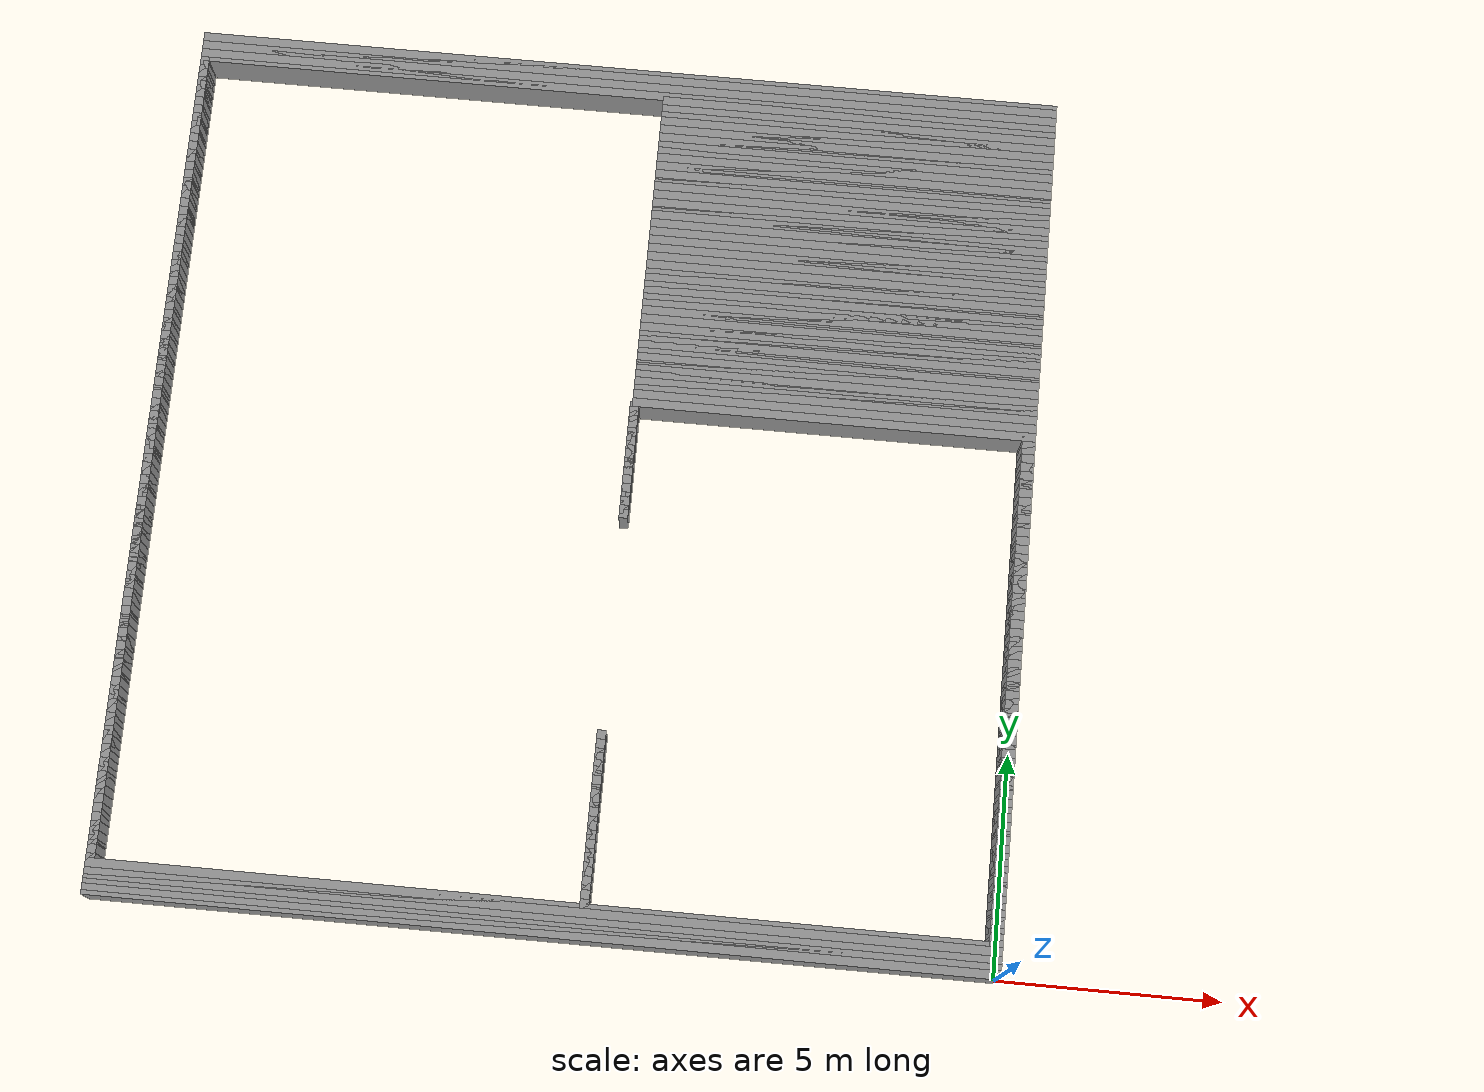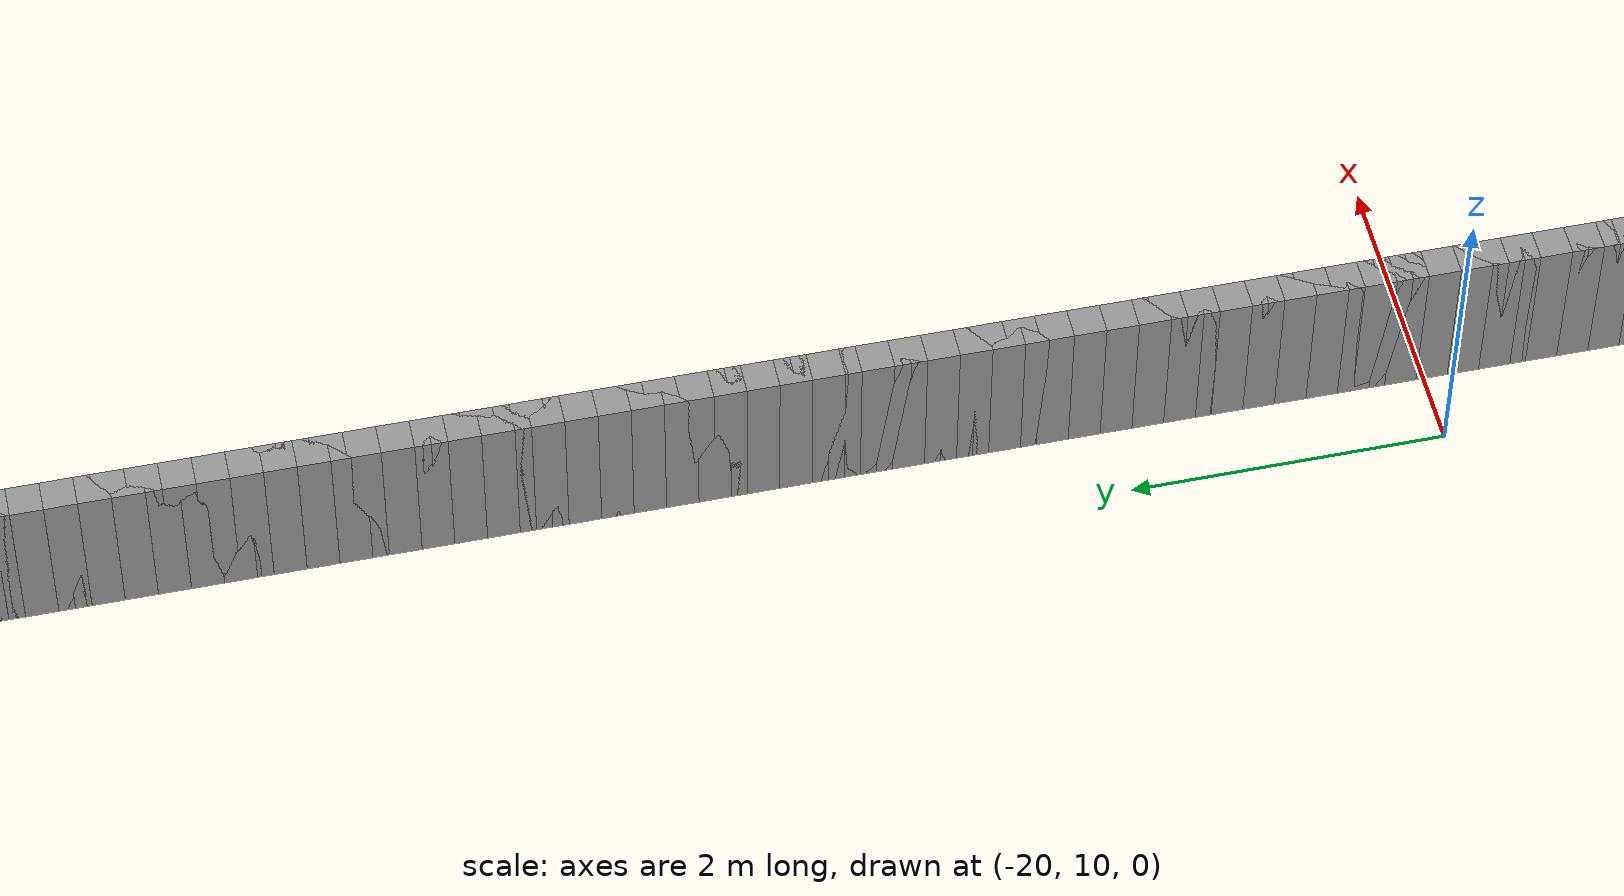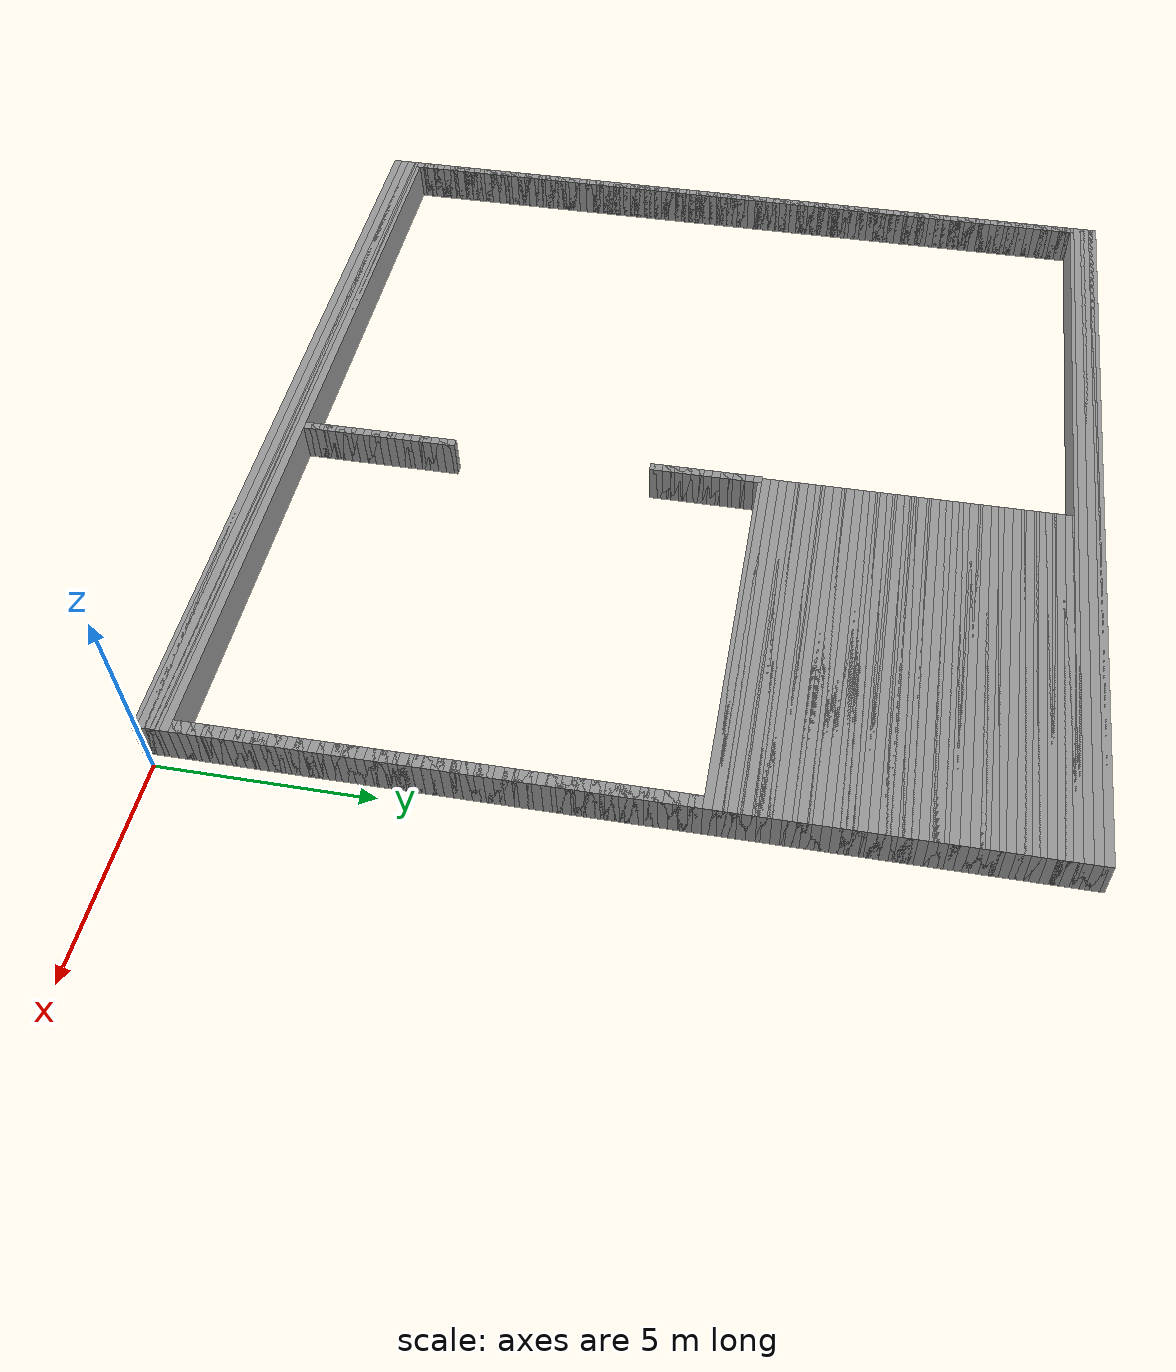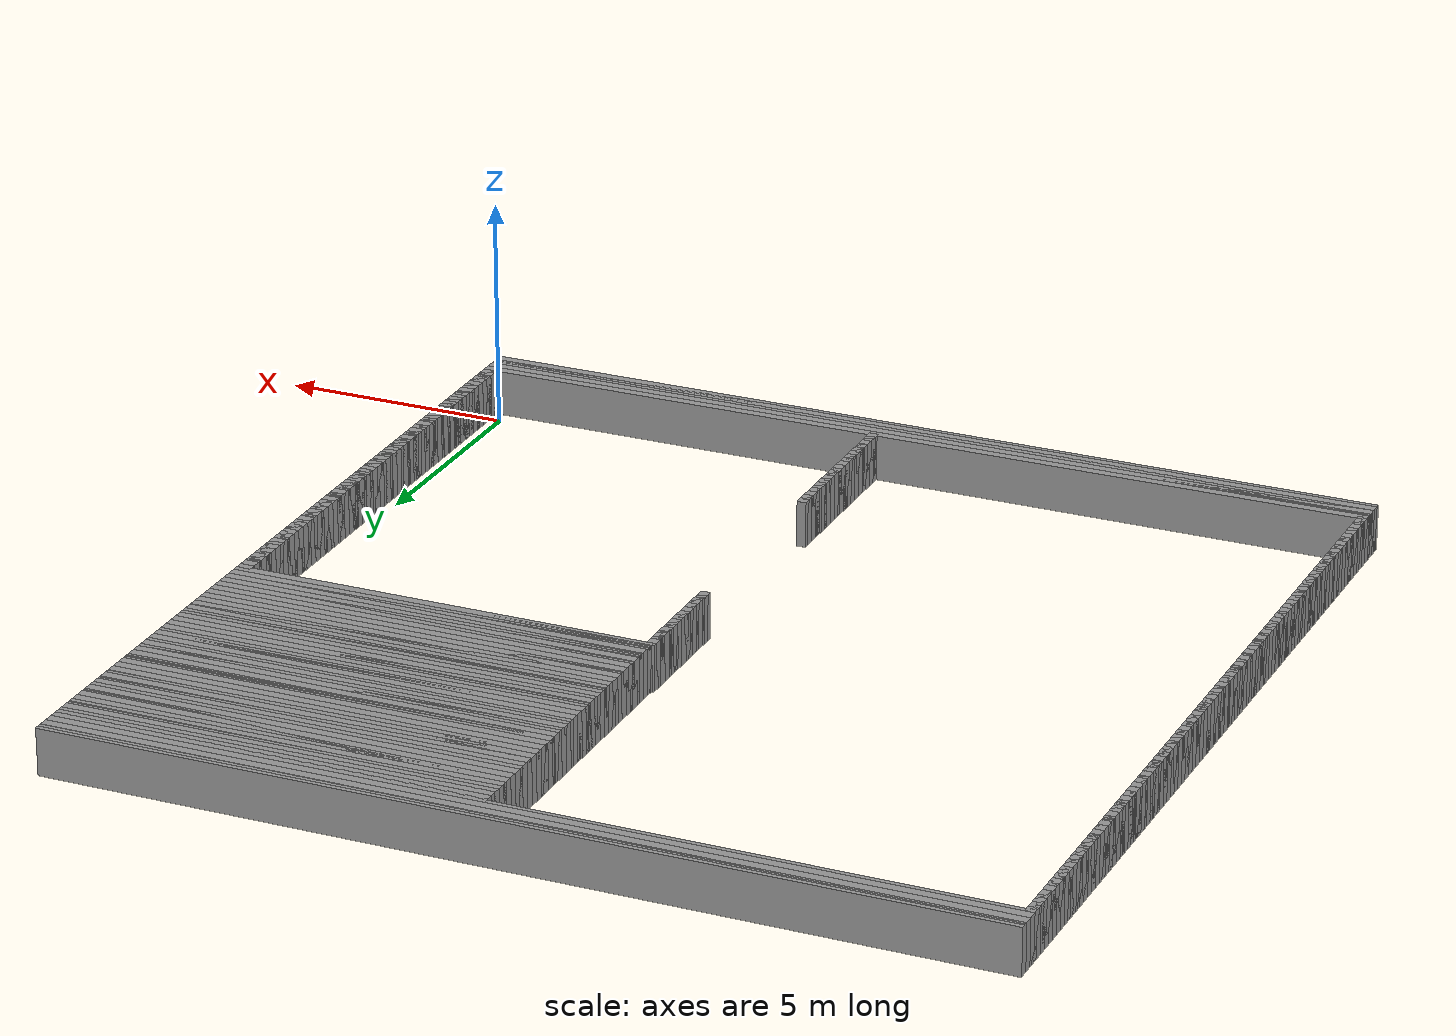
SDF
<?xml version='1.0' encoding='UTF-8'?>
<sdf version="1.6"><world name="GridMap"><model name="GridMap"><pose frame="">0 0 0 0 -0 0</pose><link name="Wall_(99.5,0.0)"><collision name="Wall_(99.5,0.0)_Collision"><geometry><box><size>19.9 0.2 1.0</size></box></geometry><pose frame="">-9.95 0.0 0.5 0 -0 0</pose></collision><visual name="Wall_(99.5,0.0)_Visual"><geometry><box><size>19.9 0.2 1.0</size></box></geometry><pose frame="">-9.95 0.0 0.5 0 -0 0</pose><material><script><uri>file://media/materials/scripts/gazebo.material</uri><name>Gazebo/Grey</name></script><ambient>1 1 1 1</ambient></material><meta><layer>0</layer></meta></visual><pose frame="">0 0 0.5 0 -0 0</pose></link><link name="Wall_(99.5,1.0)"><collision name="Wall_(99.5,1.0)_Collision"><geometry><box><size>19.9 0.2 1.0</size></box></geometry><pose frame="">-9.95 0.1 0.5 0 -0 0</pose></collision><visual name="Wall_(99.5,1.0)_Visual"><geometry><box><size>19.9 0.2 1.0</size></box></geometry><pose frame="">-9.95 0.1 0.5 0 -0 0</pose><material><script><uri>file://media/materials/scripts/gazebo.material</uri><name>Gazebo/Grey</name></script><ambient>1 1 1 1</ambient></material><meta><layer>0</layer></meta></visual><pose frame="">0 0 0.5 0 -0 0</pose></link><link name="Wall_(99.5,2.0)"><collision name="Wall_(99.5,2.0)_Collision"><geometry><box><size>19.9 0.2 1.0</size></box></geometry><pose frame="">-9.95 0.2 0.5 0 -0 0</pose></collision><visual name="Wall_(99.5,2.0)_Visual"><geometry><box><size>19.9 0.2 1.0</size></box></geometry><pose frame="">-9.95 0.2 0.5 0 -0 0</pose><material><script><uri>file://media/materials/scripts/gazebo.material</uri><name>Gazebo/Grey</name></script><ambient>1 1 1 1</ambient></material><meta><layer>0</layer></meta></visual><pose frame="">0 0 0.5 0 -0 0</pose></link><link name="Wall_(99.5,3.0)"><collision name="Wall_(99.5,3.0)_Collision"><geometry><box><size>19.9 0.2 1.0</size></box></geometry><pose frame="">-9.95 0.3 0.5 0 -0 0</pose></collision><visual name="Wall_(99.5,3.0)_Visual"><geometry><box><size>19.9 0.2 1.0</size></box></geometry><pose frame="">-9.95 0.3 0.5 0 -0 0</pose><material><script><uri>file://media/materials/scripts/gazebo.material</uri><name>Gazebo/Grey</name></script><ambient>1 1 1 1</ambient></material><meta><layer>0</layer></meta></visual><pose frame="">0 0 0.5 0 -0 0</pose></link><link name="Wall_(99.5,4.0)"><collision name="Wall_(99.5,4.0)_Collision"><geometry><box><size>19.9 0.2 1.0</size></box></geometry><pose frame="">-9.95 0.4 0.5 0 -0 0</pose></collision><visual name="Wall_(99.5,4.0)_Visual"><geometry><box><size>19.9 0.2 1.0</size></box></geometry><pose frame="">-9.95 0.4 0.5 0 -0 0</pose><material><script><uri>file://media/materials/scripts/gazebo.material</uri><name>Gazebo/Grey</name></script><ambient>1 1 1 1</ambient></material><meta><layer>0</layer></meta></visual><pose frame="">0 0 0.5 0 -0 0</pose></link><link name="Wall_(99.5,5.0)"><collision name="Wall_(99.5,5.0)_Collision"><geometry><box><size>19.9 0.2 1.0</size></box></geometry><pose frame="">-9.95 0.5 0.5 0 -0 0</pose></collision><visual name="Wall_(99.5,5.0)_Visual"><geometry><box><size>19.9 0.2 1.0</size></box></geometry><pose frame="">-9.95 0.5 0.5 0 -0 0</pose><material><script><uri>file://media/materials/scripts/gazebo.material</uri><name>Gazebo/Grey</name></script><ambient>1 1 1 1</ambient></material><meta><layer>0</layer></meta></visual><pose frame="">0 0 0.5 0 -0 0</pose></link><link name="Wall_(99.5,6.0)"><collision name="Wall_(99.5,6.0)_Collision"><geometry><box><size>19.9 0.2 1.0</size></box></geometry><pose frame="">-9.95 0.6 0.5 0 -0 0</pose></collision><visual name="Wall_(99.5,6.0)_Visual"><geometry><box><size>19.9 0.2 1.0</size></box></geometry><pose frame="">-9.95 0.6 0.5 0 -0 0</pose><material><script><uri>file://media/materials/scripts/gazebo.material</uri><name>Gazebo/Grey</name></script><ambient>1 1 1 1</ambient></material><meta><layer>0</layer></meta></visual><pose frame="">0 0 0.5 0 -0 0</pose></link><link name="Wall_(1.5,7.0)"><collision name="Wall_(1.5,7.0)_Collision"><geometry><box><size>0.3 0.2 1.0</size></box></geometry><pose frame="">-0.15 0.7 0.5 0 -0 0</pose></collision><visual name="Wall_(1.5,7.0)_Visual"><geometry><box><size>0.3 0.2 1.0</size></box></geometry><pose frame="">-0.15 0.7 0.5 0 -0 0</pose><material><script><uri>file://media/materials/scripts/gazebo.material</uri><name>Gazebo/Grey</name></script><ambient>1 1 1 1</ambient></material><meta><layer>0</layer></meta></visual><pose frame="">0 0 0.5 0 -0 0</pose></link><link name="Wall_(90.5,7.0)"><collision name="Wall_(90.5,7.0)_Collision"><geometry><box><size>0.2 0.2 1.0</size></box></geometry><pose frame="">-9.05 0.7 0.5 0 -0 0</pose></collision><visual name="Wall_(90.5,7.0)_Visual"><geometry><box><size>0.2 0.2 1.0</size></box></geometry><pose frame="">-9.05 0.7 0.5 0 -0 0</pose><material><script><uri>file://media/materials/scripts/gazebo.material</uri><name>Gazebo/Grey</name></script><ambient>1 1 1 1</ambient></material><meta><layer>0</layer></meta></visual><pose frame="">0 0 0.5 0 -0 0</pose></link><link name="Wall_(198.0,7.0)"><collision name="Wall_(198.0,7.0)_Collision"><geometry><box><size>0.2 0.2 1.0</size></box></geometry><pose frame="">-19.8 0.7 0.5 0 -0 0</pose></collision><visual name="Wall_(198.0,7.0)_Visual"><geometry><box><size>0.2 0.2 1.0</size></box></geometry><pose frame="">-19.8 0.7 0.5 0 -0 0</pose><material><script><uri>file://media/materials/scripts/gazebo.material</uri><name>Gazebo/Grey</name></script><ambient>1 1 1 1</ambient></material><meta><layer>0</layer></meta></visual><pose frame="">0 0 0.5 0 -0 0</pose></link><link name="Wall_(1.5,8.0)"><collision name="Wall_(1.5,8.0)_Collision"><geometry><box><size>0.3 0.2 1.0</size></box></geometry><pose frame="">-0.15 0.8 0.5 0 -0 0</pose></collision><visual name="Wall_(1.5,8.0)_Visual"><geometry><box><size>0.3 0.2 1.0</size></box></geometry><pose frame="">-0.15 0.8 0.5 0 -0 0</pose><material><script><uri>file://media/materials/scripts/gazebo.material</uri><name>Gazebo/Grey</name></script><ambient>1 1 1 1</ambient></material><meta><layer>0</layer></meta></visual><pose frame="">0 0 0.5 0 -0 0</pose></link><link name="Wall_(90.5,8.0)"><collision name="Wall_(90.5,8.0)_Collision"><geometry><box><size>0.2 0.2 1.0</size></box></geometry><pose frame="">-9.05 0.8 0.5 0 -0 0</pose></collision><visual name="Wall_(90.5,8.0)_Visual"><geometry><box><size>0.2 0.2 1.0</size></box></geometry><pose frame="">-9.05 0.8 0.5 0 -0 0</pose><material><script><uri>file://media/materials/scripts/gazebo.material</uri><name>Gazebo/Grey</name></script><ambient>1 1 1 1</ambient></material><meta><layer>0</layer></meta></visual><pose frame="">0 0 0.5 0 -0 0</pose></link><link name="Wall_(198.0,8.0)"><collision name="Wall_(198.0,8.0)_Collision"><geometry><box><size>0.2 0.2 1.0</size></box></geometry><pose frame="">-19.8 0.8 0.5 0 -0 0</pose></collision><visual name="Wall_(198.0,8.0)_Visual"><geometry><box><size>0.2 0.2 1.0</size></box></geometry><pose frame="">-19.8 0.8 0.5 0 -0 0</pose><material><script><uri>file://media/materials/scripts/gazebo.material</uri><name>Gazebo/Grey</name></script><ambient>1 1 1 1</ambient></material><meta><layer>0</layer></meta></visual><pose frame="">0 0 0.5 0 -0 0</pose></link><link name="Wall_(1.5,9.0)"><collision name="Wall_(1.5,9.0)_Collision"><geometry><box><size>0.3 0.2 1.0</size></box></geometry><pose frame="">-0.15 0.9 0.5 0 -0 0</pose></collision><visual name="Wall_(1.5,9.0)_Visual"><geometry><box><size>0.3 0.2 1.0</size></box></geometry><pose frame="">-0.15 0.9 0.5 0 -0 0</pose><material><script><uri>file://media/materials/scripts/gazebo.material</uri><name>Gazebo/Grey</name></script><ambient>1 1 1 1</ambient></material><meta><layer>0</layer></meta></visual><pose frame="">0 0 0.5 0 -0 0</pose></link><link name="Wall_(90.5,9.0)"><collision name="Wall_(90.5,9.0)_Collision"><geometry><box><size>0.2 0.2 1.0</size></box></geometry><pose frame="">-9.05 0.9 0.5 0 -0 0</pose></collision><visual name="Wall_(90.5,9.0)_Visual"><geometry><box><size>0.2 0.2 1.0</size></box></geometry><pose frame="">-9.05 0.9 0.5 0 -0 0</pose><material><script><uri>file://media/materials/scripts/gazebo.material</uri><name>Gazebo/Grey</name></script><ambient>1 1 1 1</ambient></material><meta><layer>0</layer></meta></visual><pose frame="">0 0 0.5 0 -0 0</pose></link><link name="Wall_(198.0,9.0)"><collision name="Wall_(198.0,9.0)_Collision"><geometry><box><size>0.2 0.2 1.0</size></box></geometry><pose frame="">-19.8 0.9 0.5 0 -0 0</pose></collision><visual name="Wall_(198.0,9.0)_Visual"><geometry><box><size>0.2 0.2 1.0</size></box></geometry><pose frame="">-19.8 0.9 0.5 0 -0 0</pose><material><script><uri>file://media/materials/scripts/gazebo.material</uri><name>Gazebo/Grey</name></script><ambient>1 1 1 1</ambient></material><meta><layer>0</layer></meta></visual><pose frame="">0 0 0.5 0 -0 0</pose></link><link name="Wall_(1.5,10.0)"><collision name="Wall_(1.5,10.0)_Collision"><geometry><box><size>0.3 0.2 1.0</size></box></geometry><pose frame="">-0.15 1.0 0.5 0 -0 0</pose></collision><visual name="Wall_(1.5,10.0)_Visual"><geometry><box><size>0.3 0.2 1.0</size></box></geometry><pose frame="">-0.15 1.0 0.5 0 -0 0</pose><material><script><uri>file://media/materials/scripts/gazebo.material</uri><name>Gazebo/Grey</name></script><ambient>1 1 1 1</ambient></material><meta><layer>0</layer></meta></visual><pose frame="">0 0 0.5 0 -0 0</pose></link><link name="Wall_(90.5,10.0)"><collision name="Wall_(90.5,10.0)_Collision"><geometry><box><size>0.2 0.2 1.0</size></box></geometry><pose frame="">-9.05 1.0 0.5 0 -0 0</pose></collision><visual name="Wall_(90.5,10.0)_Visual"><geometry><box><size>0.2 0.2 1.0</size></box></geometry><pose frame="">-9.05 1.0 0.5 0 -0 0</pose><material><script><uri>file://media/materials/scripts/gazebo.material</uri><name>Gazebo/Grey</name></script><ambient>1 1 1 1</ambient></material><meta><layer>0</layer></meta></visual><pose frame="">0 0 0.5 0 -0 0</pose></link><link name="Wall_(198.0,10.0)"><collision name="Wall_(198.0,10.0)_Collision"><geometry><box><size>0.2 0.2 1.0</size></box></geometry><pose frame="">-19.8 1.0 0.5 0 -0 0</pose></collision><visual name="Wall_(198.0,10.0)_Visual"><geometry><box><size>0.2 0.2 1.0</size></box></geometry><pose frame="">-19.8 1.0 0.5 0 -0 0</pose><material><script><uri>file://media/materials/scripts/gazebo.material</uri><name>Gazebo/Grey</name></script><ambient>1 1 1 1</ambient></material><meta><layer>0</layer></meta></visual><pose frame="">0 0 0.5 0 -0 0</pose></link><link name="Wall_(1.5,11.0)"><collision name="Wall_(1.5,11.0)_Collision"><geometry><box><size>0.3 0.2 1.0</size></box></geometry><pose frame="">-0.15 1.1 0.5 0 -0 0</pose></collision><visual name="Wall_(1.5,11.0)_Visual"><geometry><box><size>0.3 0.2 1.0</size></box></geometry><pose frame="">-0.15 1.1 0.5 0 -0 0</pose><material><script><uri>file://media/materials/scripts/gazebo.material</uri><name>Gazebo/Grey</name></script><ambient>1 1 1 1</ambient></material><meta><layer>0</layer></meta></visual><pose frame="">0 0 0.5 0 -0 0</pose></link><link name="Wall_(90.5,11.0)"><collision name="Wall_(90.5,11.0)_Collision"><geometry><box><size>0.2 0.2 1.0</size></box></geometry><pose frame="">-9.05 1.1 0.5 0 -0 0</pose></collision><visual name="Wall_(90.5,11.0)_Visual"><geometry><box><size>0.2 0.2 1.0</size></box></geometry><pose frame="">-9.05 1.1 0.5 0 -0 0</pose><material><script><uri>file://media/materials/scripts/gazebo.material</uri><name>Gazebo/Grey</name></script><ambient>1 1 1 1</ambient></material><meta><layer>0</layer></meta></visual><pose frame="">0 0 0.5 0 -0 0</pose></link><link name="Wall_(198.0,11.0)"><collision name="Wall_(198.0,11.0)_Collision"><geometry><box><size>0.2 0.2 1.0</size></box></geometry><pose frame="">-19.8 1.1 0.5 0 -0 0</pose></collision><visual name="Wall_(198.0,11.0)_Visual"><geometry><box><size>0.2 0.2 1.0</size></box></geometry><pose frame="">-19.8 1.1 0.5 0 -0 0</pose><material><script><uri>file://media/materials/scripts/gazebo.material</uri><name>Gazebo/Grey</name></script><ambient>1 1 1 1</ambient></material><meta><layer>0</layer></meta></visual><pose frame="">0 0 0.5 0 -0 0</pose></link><link name="Wall_(1.5,12.0)"><collision name="Wall_(1.5,12.0)_Collision"><geometry><box><size>0.3 0.2 1.0</size></box></geometry><pose frame="">-0.15 1.2 0.5 0 -0 0</pose></collision><visual name="Wall_(1.5,12.0)_Visual"><geometry><box><size>0.3 0.2 1.0</size></box></geometry><pose frame="">-0.15 1.2 0.5 0 -0 0</pose><material><script><uri>file://media/materials/scripts/gazebo.material</uri><name>Gazebo/Grey</name></script><ambient>1 1 1 1</ambient></material><meta><layer>0</layer></meta></visual><pose frame="">0 0 0.5 0 -0 0</pose></link><link name="Wall_(90.5,12.0)"><collision name="Wall_(90.5,12.0)_Collision"><geometry><box><size>0.2 0.2 1.0</size></box></geometry><pose frame="">-9.05 1.2 0.5 0 -0 0</pose></collision><visual name="Wall_(90.5,12.0)_Visual"><geometry><box><size>0.2 0.2 1.0</size></box></geometry><pose frame="">-9.05 1.2 0.5 0 -0 0</pose><material><script><uri>file://media/materials/scripts/gazebo.material</uri><name>Gazebo/Grey</name></script><ambient>1 1 1 1</ambient></material><meta><layer>0</layer></meta></visual><pose frame="">0 0 0.5 0 -0 0</pose></link><link name="Wall_(198.0,12.0)"><collision name="Wall_(198.0,12.0)_Collision"><geometry><box><size>0.2 0.2 1.0</size></box></geometry><pose frame="">-19.8 1.2 0.5 0 -0 0</pose></collision><visual name="Wall_(198.0,12.0)_Visual"><geometry><box><size>0.2 0.2 1.0</size></box></geometry><pose frame="">-19.8 1.2 0.5 0 -0 0</pose><material><script><uri>file://media/materials/scripts/gazebo.material</uri><name>Gazebo/Grey</name></script><ambient>1 1 1 1</ambient></material><meta><layer>0</layer></meta></visual><pose frame="">0 0 0.5 0 -0 0</pose></link><link name="Wall_(1.5,13.0)"><collision name="Wall_(1.5,13.0)_Collision"><geometry><box><size>0.3 0.2 1.0</size></box></geometry><pose frame="">-0.15 1.3 0.5 0 -0 0</pose></collision><visual name="Wall_(1.5,13.0)_Visual"><geometry><box><size>0.3 0.2 1.0</size></box></geometry><pose frame="">-0.15 1.3 0.5 0 -0 0</pose><material><script><uri>file://media/materials/scripts/gazebo.material</uri><name>Gazebo/Grey</name></script><ambient>1 1 1 1</ambient></material><meta><layer>0</layer></meta></visual><pose frame="">0 0 0.5 0 -0 0</pose></link><link name="Wall_(90.5,13.0)"><collision name="Wall_(90.5,13.0)_Collision"><geometry><box><size>0.2 0.2 1.0</size></box></geometry><pose frame="">-9.05 1.3 0.5 0 -0 0</pose></collision><visual name="Wall_(90.5,13.0)_Visual"><geometry><box><size>0.2 0.2 1.0</size></box></geometry><pose frame="">-9.05 1.3 0.5 0 -0 0</pose><material><script><uri>file://media/materials/scripts/gazebo.material</uri><name>Gazebo/Grey</name></script><ambient>1 1 1 1</ambient></material><meta><layer>0</layer></meta></visual><pose frame="">0 0 0.5 0 -0 0</pose></link><link name="Wall_(198.0,13.0)"><collision name="Wall_(198.0,13.0)_Collision"><geometry><box><size>0.2 0.2 1.0</size></box></geometry><pose frame="">-19.8 1.3 0.5 0 -0 0</pose></collision><visual name="Wall_(198.0,13.0)_Visual"><geometry><box><size>0.2 0.2 1.0</size></box></geometry><pose frame="">-19.8 1.3 0.5 0 -0 0</pose><material><script><uri>file://media/materials/scripts/gazebo.material</uri><name>Gazebo/Grey</name></script><ambient>1 1 1 1</ambient></material><meta><layer>0</layer></meta></visual><pose frame="">0 0 0.5 0 -0 0</pose></link><link name="Wall_(1.5,14.0)"><collision name="Wall_(1.5,14.0)_Collision"><geometry><box><size>0.3 0.2 1.0</size></box></geometry><pose frame="">-0.15 1.4 0.5 0 -0 0</pose></collision><visual name="Wall_(1.5,14.0)_Visual"><geometry><box><size>0.3 0.2 1.0</size></box></geometry><pose frame="">-0.15 1.4 0.5 0 -0 0</pose><material><script><uri>file://media/materials/scripts/gazebo.material</uri><name>Gazebo/Grey</name></script><ambient>1 1 1 1</ambient></material><meta><layer>0</layer></meta></visual><pose frame="">0 0 0.5 0 -0 0</pose></link><link name="Wall_(90.5,14.0)"><collision name="Wall_(90.5,14.0)_Collision"><geometry><box><size>0.2 0.2 1.0</size></box></geometry><pose frame="">-9.05 1.4 0.5 0 -0 0</pose></collision><visual name="Wall_(90.5,14.0)_Visual"><geometry><box><size>0.2 0.2 1.0</size></box></geometry><pose frame="">-9.05 1.4 0.5 0 -0 0</pose><material><script><uri>file://media/materials/scripts/gazebo.material</uri><name>Gazebo/Grey</name></script><ambient>1 1 1 1</ambient></material><meta><layer>0</layer></meta></visual><pose frame="">0 0 0.5 0 -0 0</pose></link><link name="Wall_(198.0,14.0)"><collision name="Wall_(198.0,14.0)_Collision"><geometry><box><size>0.2 0.2 1.0</size></box></geometry><pose frame="">-19.8 1.4 0.5 0 -0 0</pose></collision><visual name="Wall_(198.0,14.0)_Visual"><geometry><box><size>0.2 0.2 1.0</size></box></geometry><pose frame="">-19.8 1.4 0.5 0 -0 0</pose><material><script><uri>file://media/materials/scripts/gazebo.material</uri><name>Gazebo/Grey</name></script><ambient>1 1 1 1</ambient></material><meta><layer>0</layer></meta></visual><pose frame="">0 0 0.5 0 -0 0</pose></link><link name="Wall_(1.5,15.0)"><collision name="Wall_(1.5,15.0)_Collision"><geometry><box><size>0.3 0.2 1.0</size></box></geometry><pose frame="">-0.15 1.5 0.5 0 -0 0</pose></collision><visual name="Wall_(1.5,15.0)_Visual"><geometry><box><size>0.3 0.2 1.0</size></box></geometry><pose frame="">-0.15 1.5 0.5 0 -0 0</pose><material><script><uri>file://media/materials/scripts/gazebo.material</uri><name>Gazebo/Grey</name></script><ambient>1 1 1 1</ambient></material><meta><layer>0</layer></meta></visual><pose frame="">0 0 0.5 0 -0 0</pose></link><link name="Wall_(90.5,15.0)"><collision name="Wall_(90.5,15.0)_Collision"><geometry><box><size>0.2 0.2 1.0</size></box></geometry><pose frame="">-9.05 1.5 0.5 0 -0 0</pose></collision><visual name="Wall_(90.5,15.0)_Visual"><geometry><box><size>0.2 0.2 1.0</size></box></geometry><pose frame="">-9.05 1.5 0.5 0 -0 0</pose><material><script><uri>file://media/materials/scripts/gazebo.material</uri><name>Gazebo/Grey</name></script><ambient>1 1 1 1</ambient></material><meta><layer>0</layer></meta></visual><pose frame="">0 0 0.5 0 -0 0</pose></link><link name="Wall_(198.0,15.0)"><collision name="Wall_(198.0,15.0)_Collision"><geometry><box><size>0.2 0.2 1.0</size></box></geometry><pose frame="">-19.8 1.5 0.5 0 -0 0</pose></collision><visual name="Wall_(198.0,15.0)_Visual"><geometry><box><size>0.2 0.2 1.0</size></box></geometry><pose frame="">-19.8 1.5 0.5 0 -0 0</pose><material><script><uri>file://media/materials/scripts/gazebo.material</uri><name>Gazebo/Grey</name></script><ambient>1 1 1 1</ambient></material><meta><layer>0</layer></meta></visual><pose frame="">0 0 0.5 0 -0 0</pose></link><link name="Wall_(1.5,16.0)"><collision name="Wall_(1.5,16.0)_Collision"><geometry><box><size>0.3 0.2 1.0</size></box></geometry><pose frame="">-0.15 1.6 0.5 0 -0 0</pose></collision><visual name="Wall_(1.5,16.0)_Visual"><geometry><box><size>0.3 0.2 1.0</size></box></geometry><pose frame="">-0.15 1.6 0.5 0 -0 0</pose><material><script><uri>file://media/materials/scripts/gazebo.material</uri><name>Gazebo/Grey</name></script><ambient>1 1 1 1</ambient></material><meta><layer>0</layer></meta></visual><pose frame="">0 0 0.5 0 -0 0</pose></link><link name="Wall_(90.5,16.0)"><collision name="Wall_(90.5,16.0)_Collision"><geometry><box><size>0.2 0.2 1.0</size></box></geometry><pose frame="">-9.05 1.6 0.5 0 -0 0</pose></collision><visual name="Wall_(90.5,16.0)_Visual"><geometry><box><size>0.2 0.2 1.0</size></box></geometry><pose frame="">-9.05 1.6 0.5 0 -0 0</pose><material><script><uri>file://media/materials/scripts/gazebo.material</uri><name>Gazebo/Grey</name></script><ambient>1 1 1 1</ambient></material><meta><layer>0</layer></meta></visual><pose frame="">0 0 0.5 0 -0 0</pose></link><link name="Wall_(198.0,16.0)"><collision name="Wall_(198.0,16.0)_Collision"><geometry><box><size>0.2 0.2 1.0</size></box></geometry><pose frame="">-19.8 1.6 0.5 0 -0 0</pose></collision><visual name="Wall_(198.0,16.0)_Visual"><geometry><box><size>0.2 0.2 1.0</size></box></geometry><pose frame="">-19.8 1.6 0.5 0 -0 0</pose><material><script><uri>file://media/materials/scripts/gazebo.material</uri><name>Gazebo/Grey</name></script><ambient>1 1 1 1</ambient></material><meta><layer>0</layer></meta></visual><pose frame="">0 0 0.5 0 -0 0</pose></link><link name="Wall_(1.5,17.0)"><collision name="Wall_(1.5,17.0)_Collision"><geometry><box><size>0.3 0.2 1.0</size></box></geometry><pose frame="">-0.15 1.7 0.5 0 -0 0</pose></collision><visual name="Wall_(1.5,17.0)_Visual"><geometry><box><size>0.3 0.2 1.0</size></box></geometry><pose frame="">-0.15 1.7 0.5 0 -0 0</pose><material><script><uri>file://media/materials/scripts/gazebo.material</uri><name>Gazebo/Grey</name></script><ambient>1 1 1 1</ambient></material><meta><layer>0</layer></meta></visual><pose frame="">0 0 0.5 0 -0 0</pose></link><link name="Wall_(90.5,17.0)"><collision name="Wall_(90.5,17.0)_Collision"><geometry><box><size>0.2 0.2 1.0</size></box></geometry><pose frame="">-9.05 1.7 0.5 0 -0 0</pose></collision><visual name="Wall_(90.5,17.0)_Visual"><geometry><box><size>0.2 0.2 1.0</size></box></geometry><pose frame="">-9.05 1.7 0.5 0 -0 0</pose><material><script><uri>file://media/materials/scripts/gazebo.material</uri><name>Gazebo/Grey</name></script><ambient>1 1 1 1</ambient></material><meta><layer>0</layer></meta></visual><pose frame="">0 0 0.5 0 -0 0</pose></link><link name="Wall_(198.0,17.0)"><collision name="Wall_(198.0,17.0)_Collision"><geometry><box><size>0.2 0.2 1.0</size></box></geometry><pose frame="">-19.8 1.7 0.5 0 -0 0</pose></collision><visual name="Wall_(198.0,17.0)_Visual"><geometry><box><size>0.2 0.2 1.0</size></box></geometry><pose frame="">-19.8 1.7 0.5 0 -0 0</pose><material><script><uri>file://media/materials/scripts/gazebo.material</uri><name>Gazebo/Grey</name></script><ambient>1 1 1 1</ambient></material><meta><layer>0</layer></meta></visual><pose frame="">0 0 0.5 0 -0 0</pose></link><link name="Wall_(1.5,18.0)"><collision name="Wall_(1.5,18.0)_Collision"><geometry><box><size>0.3 0.2 1.0</size></box></geometry><pose frame="">-0.15 1.8 0.5 0 -0 0</pose></collision><visual name="Wall_(1.5,18.0)_Visual"><geometry><box><size>0.3 0.2 1.0</size></box></geometry><pose frame="">-0.15 1.8 0.5 0 -0 0</pose><material><script><uri>file://media/materials/scripts/gazebo.material</uri><name>Gazebo/Grey</name></script><ambient>1 1 1 1</ambient></material><meta><layer>0</layer></meta></visual><pose frame="">0 0 0.5 0 -0 0</pose></link><link name="Wall_(90.5,18.0)"><collision name="Wall_(90.5,18.0)_Collision"><geometry><box><size>0.2 0.2 1.0</size></box></geometry><pose frame="">-9.05 1.8 0.5 0 -0 0</pose></collision><visual name="Wall_(90.5,18.0)_Visual"><geometry><box><size>0.2 0.2 1.0</size></box></geometry><pose frame="">-9.05 1.8 0.5 0 -0 0</pose><material><script><uri>file://media/materials/scripts/gazebo.material</uri><name>Gazebo/Grey</name></script><ambient>1 1 1 1</ambient></material><meta><layer>0</layer></meta></visual><pose frame="">0 0 0.5 0 -0 0</pose></link><link name="Wall_(198.0,18.0)"><collision name="Wall_(198.0,18.0)_Collision"><geometry><box><size>0.2 0.2 1.0</size></box></geometry><pose frame="">-19.8 1.8 0.5 0 -0 0</pose></collision><visual name="Wall_(198.0,18.0)_Visual"><geometry><box><size>0.2 0.2 1.0</size></box></geometry><pose frame="">-19.8 1.8 0.5 0 -0 0</pose><material><script><uri>file://media/materials/scripts/gazebo.material</uri><name>Gazebo/Grey</name></script><ambient>1 1 1 1</ambient></material><meta><layer>0</layer></meta></visual><pose frame="">0 0 0.5 0 -0 0</pose></link><link name="Wall_(1.5,19.0)"><collision name="Wall_(1.5,19.0)_Collision"><geometry><box><size>0.3 0.2 1.0</size></box></geometry><pose frame="">-0.15 1.9 0.5 0 -0 0</pose></collision><visual name="Wall_(1.5,19.0)_Visual"><geometry><box><size>0.3 0.2 1.0</size></box></geometry><pose frame="">-0.15 1.9 0.5 0 -0 0</pose><material><script><uri>file://media/materials/scripts/gazebo.material</uri><name>Gazebo/Grey</name></script><ambient>1 1 1 1</ambient></material><meta><layer>0</layer></meta></visual><pose frame="">0 0 0.5 0 -0 0</pose></link><link name="Wall_(90.5,19.0)"><collision name="Wall_(90.5,19.0)_Collision"><geometry><box><size>0.2 0.2 1.0</size></box></geometry><pose frame="">-9.05 1.9 0.5 0 -0 0</pose></collision><visual name="Wall_(90.5,19.0)_Visual"><geometry><box><size>0.2 0.2 1.0</size></box></geometry><pose frame="">-9.05 1.9 0.5 0 -0 0</pose><material><script><uri>file://media/materials/scripts/gazebo.material</uri><name>Gazebo/Grey</name></script><ambient>1 1 1 1</ambient></material><meta><layer>0</layer></meta></visual><pose frame="">0 0 0.5 0 -0 0</pose></link><link name="Wall_(198.0,19.0)"><collision name="Wall_(198.0,19.0)_Collision"><geometry><box><size>0.2 0.2 1.0</size></box></geometry><pose frame="">-19.8 1.9 0.5 0 -0 0</pose></collision><visual name="Wall_(198.0,19.0)_Visual"><geometry><box><size>0.2 0.2 1.0</size></box></geometry><pose frame="">-19.8 1.9 0.5 0 -0 0</pose><material><script><uri>file://media/materials/scripts/gazebo.material</uri><name>Gazebo/Grey</name></script><ambient>1 1 1 1</ambient></material><meta><layer>0</layer></meta></visual><pose frame="">0 0 0.5 0 -0 0</pose></link><link name="Wall_(1.5,20.0)"><collision name="Wall_(1.5,20.0)_Collision"><geometry><box><size>0.3 0.2 1.0</size></box></geometry><pose frame="">-0.15 2.0 0.5 0 -0 0</pose></collision><visual name="Wall_(1.5,20.0)_Visual"><geometry><box><size>0.3 0.2 1.0</size></box></geometry><pose frame="">-0.15 2.0 0.5 0 -0 0</pose><material><script><uri>file://media/materials/scripts/gazebo.material</uri><name>Gazebo/Grey</name></script><ambient>1 1 1 1</ambient></material><meta><layer>0</layer></meta></visual><pose frame="">0 0 0.5 0 -0 0</pose></link><link name="Wall_(90.5,20.0)"><collision name="Wall_(90.5,20.0)_Collision"><geometry><box><size>0.2 0.2 1.0</size></box></geometry><pose frame="">-9.05 2.0 0.5 0 -0 0</pose></collision><visual name="Wall_(90.5,20.0)_Visual"><geometry><box><size>0.2 0.2 1.0</size></box></geometry><pose frame="">-9.05 2.0 0.5 0 -0 0</pose><material><script><uri>file://media/materials/scripts/gazebo.material</uri><name>Gazebo/Grey</name></script><ambient>1 1 1 1</ambient></material><meta><layer>0</layer></meta></visual><pose frame="">0 0 0.5 0 -0 0</pose></link><link name="Wall_(198.0,20.0)"><collision name="Wall_(198.0,20.0)_Collision"><geometry><box><size>0.2 0.2 1.0</size></box></geometry><pose frame="">-19.8 2.0 0.5 0 -0 0</pose></collision><visual name="Wall_(198.0,20.0)_Visual"><geometry><box><size>0.2 0.2 1.0</size></box></geometry><pose frame="">-19.8 2.0 0.5 0 -0 0</pose><material><script><uri>file://media/materials/scripts/gazebo.material</uri><name>Gazebo/Grey</name></script><ambient>1 1 1 1</ambient></material><meta><layer>0</layer></meta></visual><pose frame="">0 0 0.5 0 -0 0</pose></link><link name="Wall_(1.5,21.0)"><collision name="Wall_(1.5,21.0)_Collision"><geometry><box><size>0.3 0.2 1.0</size></box></geometry><pose frame="">-0.15 2.1 0.5 0 -0 0</pose></collision><visual name="Wall_(1.5,21.0)_Visual"><geometry><box><size>0.3 0.2 1.0</size></box></geometry><pose frame="">-0.15 2.1 0.5 0 -0 0</pose><material><script><uri>file://media/materials/scripts/gazebo.material</uri><name>Gazebo/Grey</name></script><ambient>1 1 1 1</ambient></material><meta><layer>0</layer></meta></visual><pose frame="">0 0 0.5 0 -0 0</pose></link><link name="Wall_(90.5,21.0)"><collision name="Wall_(90.5,21.0)_Collision"><geometry><box><size>0.2 0.2 1.0</size></box></geometry><pose frame="">-9.05 2.1 0.5 0 -0 0</pose></collision><visual name="Wall_(90.5,21.0)_Visual"><geometry><box><size>0.2 0.2 1.0</size></box></geometry><pose frame="">-9.05 2.1 0.5 0 -0 0</pose><material><script><uri>file://media/materials/scripts/gazebo.material</uri><name>Gazebo/Grey</name></script><ambient>1 1 1 1</ambient></material><meta><layer>0</layer></meta></visual><pose frame="">0 0 0.5 0 -0 0</pose></link><link name="Wall_(198.0,21.0)"><collision name="Wall_(198.0,21.0)_Collision"><geometry><box><size>0.2 0.2 1.0</size></box></geometry><pose frame="">-19.8 2.1 0.5 0 -0 0</pose></collision><visual name="Wall_(198.0,21.0)_Visual"><geometry><box><size>0.2 0.2 1.0</size></box></geometry><pose frame="">-19.8 2.1 0.5 0 -0 0</pose><material><script><uri>file://media/materials/scripts/gazebo.material</uri><name>Gazebo/Grey</name></script><ambient>1 1 1 1</ambient></material><meta><layer>0</layer></meta></visual><pose frame="">0 0 0.5 0 -0 0</pose></link><link name="Wall_(1.5,22.0)"><collision name="Wall_(1.5,22.0)_Collision"><geometry><box><size>0.3 0.2 1.0</size></box></geometry><pose frame="">-0.15 2.2 0.5 0 -0 0</pose></collision><visual name="Wall_(1.5,22.0)_Visual"><geometry><box><size>0.3 0.2 1.0</size></box></geometry><pose frame="">-0.15 2.2 0.5 0 -0 0</pose><material><script><uri>file://media/materials/scripts/gazebo.material</uri><name>Gazebo/Grey</name></script><ambient>1 1 1 1</ambient></material><meta><layer>0</layer></meta></visual><pose frame="">0 0 0.5 0 -0 0</pose></link><link name="Wall_(90.5,22.0)"><collision name="Wall_(90.5,22.0)_Collision"><geometry><box><size>0.2 0.2 1.0</size></box></geometry><pose frame="">-9.05 2.2 0.5 0 -0 0</pose></collision><visual name="Wall_(90.5,22.0)_Visual"><geometry><box><size>0.2 0.2 1.0</size></box></geometry><pose frame="">-9.05 2.2 0.5 0 -0 0</pose><material><script><uri>file://media/materials/scripts/gazebo.material</uri><name>Gazebo/Grey</name></script><ambient>1 1 1 1</ambient></material><meta><layer>0</layer></meta></visual><pose frame="">0 0 0.5 0 -0 0</pose></link><link name="Wall_(198.0,22.0)"><collision name="Wall_(198.0,22.0)_Collision"><geometry><box><size>0.2 0.2 1.0</size></box></geometry><pose frame="">-19.8 2.2 0.5 0 -0 0</pose></collision><visual name="Wall_(198.0,22.0)_Visual"><geometry><box><size>0.2 0.2 1.0</size></box></geometry><pose frame="">-19.8 2.2 0.5 0 -0 0</pose><material><script><uri>file://media/materials/scripts/gazebo.material</uri><name>Gazebo/Grey</name></script><ambient>1 1 1 1</ambient></material><meta><layer>0</layer></meta></visual><pose frame="">0 0 0.5 0 -0 0</pose></link><link name="Wall_(1.5,23.0)"><collision name="Wall_(1.5,23.0)_Collision"><geometry><box><size>0.3 0.2 1.0</size></box></geometry><pose frame="">-0.15 2.3 0.5 0 -0 0</pose></collision><visual name="Wall_(1.5,23.0)_Visual"><geometry><box><size>0.3 0.2 1.0</size></box></geometry><pose frame="">-0.15 2.3 0.5 0 -0 0</pose><material><script><uri>file://media/materials/scripts/gazebo.material</uri><name>Gazebo/Grey</name></script><ambient>1 1 1 1</ambient></material><meta><layer>0</layer></meta></visual><pose frame="">0 0 0.5 0 -0 0</pose></link><link name="Wall_(90.5,23.0)"><collision name="Wall_(90.5,23.0)_Collision"><geometry><box><size>0.2 0.2 1.0</size></box></geometry><pose frame="">-9.05 2.3 0.5 0 -0 0</pose></collision><visual name="Wall_(90.5,23.0)_Visual"><geometry><box><size>0.2 0.2 1.0</size></box></geometry><pose frame="">-9.05 2.3 0.5 0 -0 0</pose><material><script><uri>file://media/materials/scripts/gazebo.material</uri><name>Gazebo/Grey</name></script><ambient>1 1 1 1</ambient></material><meta><layer>0</layer></meta></visual><pose frame="">0 0 0.5 0 -0 0</pose></link><link name="Wall_(198.0,23.0)"><collision name="Wall_(198.0,23.0)_Collision"><geometry><box><size>0.2 0.2 1.0</size></box></geometry><pose frame="">-19.8 2.3 0.5 0 -0 0</pose></collision><visual name="Wall_(198.0,23.0)_Visual"><geometry><box><size>0.2 0.2 1.0</size></box></geometry><pose frame="">-19.8 2.3 0.5 0 -0 0</pose><material><script><uri>file://media/materials/scripts/gazebo.material</uri><name>Gazebo/Grey</name></script><ambient>1 1 1 1</ambient></material><meta><layer>0</layer></meta></visual><pose frame="">0 0 0.5 0 -0 0</pose></link><link name="Wall_(1.5,24.0)"><collision name="Wall_(1.5,24.0)_Collision"><geometry><box><size>0.3 0.2 1.0</size></box></geometry><pose frame="">-0.15 2.4 0.5 0 -0 0</pose></collision><visual name="Wall_(1.5,24.0)_Visual"><geometry><box><size>0.3 0.2 1.0</size></box></geometry><pose frame="">-0.15 2.4 0.5 0 -0 0</pose><material><script><uri>file://media/materials/scripts/gazebo.material</uri><name>Gazebo/Grey</name></script><ambient>1 1 1 1</ambient></material><meta><layer>0</layer></meta></visual><pose frame="">0 0 0.5 0 -0 0</pose></link><link name="Wall_(90.5,24.0)"><collision name="Wall_(90.5,24.0)_Collision"><geometry><box><size>0.2 0.2 1.0</size></box></geometry><pose frame="">-9.05 2.4 0.5 0 -0 0</pose></collision><visual name="Wall_(90.5,24.0)_Visual"><geometry><box><size>0.2 0.2 1.0</size></box></geometry><pose frame="">-9.05 2.4 0.5 0 -0 0</pose><material><script><uri>file://media/materials/scripts/gazebo.material</uri><name>Gazebo/Grey</name></script><ambient>1 1 1 1</ambient></material><meta><layer>0</layer></meta></visual><pose frame="">0 0 0.5 0 -0 0</pose></link><link name="Wall_(198.0,24.0)"><collision name="Wall_(198.0,24.0)_Collision"><geometry><box><size>0.2 0.2 1.0</size></box></geometry><pose frame="">-19.8 2.4 0.5 0 -0 0</pose></collision><visual name="Wall_(198.0,24.0)_Visual"><geometry><box><size>0.2 0.2 1.0</size></box></geometry><pose frame="">-19.8 2.4 0.5 0 -0 0</pose><material><script><uri>file://media/materials/scripts/gazebo.material</uri><name>Gazebo/Grey</name></script><ambient>1 1 1 1</ambient></material><meta><layer>0</layer></meta></visual><pose frame="">0 0 0.5 0 -0 0</pose></link><link name="Wall_(1.5,25.0)"><collision name="Wall_(1.5,25.0)_Collision"><geometry><box><size>0.3 0.2 1.0</size></box></geometry><pose frame="">-0.15 2.5 0.5 0 -0 0</pose></collision><visual name="Wall_(1.5,25.0)_Visual"><geometry><box><size>0.3 0.2 1.0</size></box></geometry><pose frame="">-0.15 2.5 0.5 0 -0 0</pose><material><script><uri>file://media/materials/scripts/gazebo.material</uri><name>Gazebo/Grey</name></script><ambient>1 1 1 1</ambient></material><meta><layer>0</layer></meta></visual><pose frame="">0 0 0.5 0 -0 0</pose></link><link name="Wall_(90.5,25.0)"><collision name="Wall_(90.5,25.0)_Collision"><geometry><box><size>0.2 0.2 1.0</size></box></geometry><pose frame="">-9.05 2.5 0.5 0 -0 0</pose></collision><visual name="Wall_(90.5,25.0)_Visual"><geometry><box><size>0.2 0.2 1.0</size></box></geometry><pose frame="">-9.05 2.5 0.5 0 -0 0</pose><material><script><uri>file://media/materials/scripts/gazebo.material</uri><name>Gazebo/Grey</name></script><ambient>1 1 1 1</ambient></material><meta><layer>0</layer></meta></visual><pose frame="">0 0 0.5 0 -0 0</pose></link><link name="Wall_(198.0,25.0)"><collision name="Wall_(198.0,25.0)_Collision"><geometry><box><size>0.2 0.2 1.0</size></box></geometry><pose frame="">-19.8 2.5 0.5 0 -0 0</pose></collision><visual name="Wall_(198.0,25.0)_Visual"><geometry><box><size>0.2 0.2 1.0</size></box></geometry><pose frame="">-19.8 2.5 0.5 0 -0 0</pose><material><script><uri>file://media/materials/scripts/gazebo.material</uri><name>Gazebo/Grey</name></script><ambient>1 1 1 1</ambient></material><meta><layer>0</layer></meta></visual><pose frame="">0 0 0.5 0 -0 0</pose></link><link name="Wall_(1.5,26.0)"><collision name="Wall_(1.5,26.0)_Collision"><geometry><box><size>0.3 0.2 1.0</size></box></geometry><pose frame="">-0.15 2.6 0.5 0 -0 0</pose></collision><visual name="Wall_(1.5,26.0)_Visual"><geometry><box><size>0.3 0.2 1.0</size></box></geometry><pose frame="">-0.15 2.6 0.5 0 -0 0</pose><material><script><uri>file://media/materials/scripts/gazebo.material</uri><name>Gazebo/Grey</name></script><ambient>1 1 1 1</ambient></material><meta><layer>0</layer></meta></visual><pose frame="">0 0 0.5 0 -0 0</pose></link><link name="Wall_(90.5,26.0)"><collision name="Wall_(90.5,26.0)_Collision"><geometry><box><size>0.2 0.2 1.0</size></box></geometry><pose frame="">-9.05 2.6 0.5 0 -0 0</pose></collision><visual name="Wall_(90.5,26.0)_Visual"><geometry><box><size>0.2 0.2 1.0</size></box></geometry><pose frame="">-9.05 2.6 0.5 0 -0 0</pose><material><script><uri>file://media/materials/scripts/gazebo.material</uri><name>Gazebo/Grey</name></script><ambient>1 1 1 1</ambient></material><meta><layer>0</layer></meta></visual><pose frame="">0 0 0.5 0 -0 0</pose></link><link name="Wall_(198.0,26.0)"><collision name="Wall_(198.0,26.0)_Collision"><geometry><box><size>0.2 0.2 1.0</size></box></geometry><pose frame="">-19.8 2.6 0.5 0 -0 0</pose></collision><visual name="Wall_(198.0,26.0)_Visual"><geometry><box><size>0.2 0.2 1.0</size></box></geometry><pose frame="">-19.8 2.6 0.5 0 -0 0</pose><material><script><uri>file://media/materials/scripts/gazebo.material</uri><name>Gazebo/Grey</name></script><ambient>1 1 1 1</ambient></material><meta><layer>0</layer></meta></visual><pose frame="">0 0 0.5 0 -0 0</pose></link><link name="Wall_(1.5,27.0)"><collision name="Wall_(1.5,27.0)_Collision"><geometry><box><size>0.3 0.2 1.0</size></box></geometry><pose frame="">-0.15 2.7 0.5 0 -0 0</pose></collision><visual name="Wall_(1.5,27.0)_Visual"><geometry><box><size>0.3 0.2 1.0</size></box></geometry><pose frame="">-0.15 2.7 0.5 0 -0 0</pose><material><script><uri>file://media/materials/scripts/gazebo.material</uri><name>Gazebo/Grey</name></script><ambient>1 1 1 1</ambient></material><meta><layer>0</layer></meta></visual><pose frame="">0 0 0.5 0 -0 0</pose></link><link name="Wall_(90.5,27.0)"><collision name="Wall_(90.5,27.0)_Collision"><geometry><box><size>0.2 0.2 1.0</size></box></geometry><pose frame="">-9.05 2.7 0.5 0 -0 0</pose></collision><visual name="Wall_(90.5,27.0)_Visual"><geometry><box><size>0.2 0.2 1.0</size></box></geometry><pose frame="">-9.05 2.7 0.5 0 -0 0</pose><material><script><uri>file://media/materials/scripts/gazebo.material</uri><name>Gazebo/Grey</name></script><ambient>1 1 1 1</ambient></material><meta><layer>0</layer></meta></visual><pose frame="">0 0 0.5 0 -0 0</pose></link><link name="Wall_(198.0,27.0)"><collision name="Wall_(198.0,27.0)_Collision"><geometry><box><size>0.2 0.2 1.0</size></box></geometry><pose frame="">-19.8 2.7 0.5 0 -0 0</pose></collision><visual name="Wall_(198.0,27.0)_Visual"><geometry><box><size>0.2 0.2 1.0</size></box></geometry><pose frame="">-19.8 2.7 0.5 0 -0 0</pose><material><script><uri>file://media/materials/scripts/gazebo.material</uri><name>Gazebo/Grey</name></script><ambient>1 1 1 1</ambient></material><meta><layer>0</layer></meta></visual><pose frame="">0 0 0.5 0 -0 0</pose></link><link name="Wall_(1.5,28.0)"><collision name="Wall_(1.5,28.0)_Collision"><geometry><box><size>0.3 0.2 1.0</size></box></geometry><pose frame="">-0.15 2.8 0.5 0 -0 0</pose></collision><visual name="Wall_(1.5,28.0)_Visual"><geometry><box><size>0.3 0.2 1.0</size></box></geometry><pose frame="">-0.15 2.8 0.5 0 -0 0</pose><material><script><uri>file://media/materials/scripts/gazebo.material</uri><name>Gazebo/Grey</name></script><ambient>1 1 1 1</ambient></material><meta><layer>0</layer></meta></visual><pose frame="">0 0 0.5 0 -0 0</pose></link><link name="Wall_(90.5,28.0)"><collision name="Wall_(90.5,28.0)_Collision"><geometry><box><size>0.2 0.2 1.0</size></box></geometry><pose frame="">-9.05 2.8 0.5 0 -0 0</pose></collision><visual name="Wall_(90.5,28.0)_Visual"><geometry><box><size>0.2 0.2 1.0</size></box></geometry><pose frame="">-9.05 2.8 0.5 0 -0 0</pose><material><script><uri>file://media/materials/scripts/gazebo.material</uri><name>Gazebo/Grey</name></script><ambient>1 1 1 1</ambient></material><meta><layer>0</layer></meta></visual><pose frame="">0 0 0.5 0 -0 0</pose></link><link name="Wall_(198.0,28.0)"><collision name="Wall_(198.0,28.0)_Collision"><geometry><box><size>0.2 0.2 1.0</size></box></geometry><pose frame="">-19.8 2.8 0.5 0 -0 0</pose></collision><visual name="Wall_(198.0,28.0)_Visual"><geometry><box><size>0.2 0.2 1.0</size></box></geometry><pose frame="">-19.8 2.8 0.5 0 -0 0</pose><material><script><uri>file://media/materials/scripts/gazebo.material</uri><name>Gazebo/Grey</name></script><ambient>1 1 1 1</ambient></material><meta><layer>0</layer></meta></visual><pose frame="">0 0 0.5 0 -0 0</pose></link><link name="Wall_(1.5,29.0)"><collision name="Wall_(1.5,29.0)_Collision"><geometry><box><size>0.3 0.2 1.0</size></box></geometry><pose frame="">-0.15 2.9 0.5 0 -0 0</pose></collision><visual name="Wall_(1.5,29.0)_Visual"><geometry><box><size>0.3 0.2 1.0</size></box></geometry><pose frame="">-0.15 2.9 0.5 0 -0 0</pose><material><script><uri>file://media/materials/scripts/gazebo.material</uri><name>Gazebo/Grey</name></script><ambient>1 1 1 1</ambient></material><meta><layer>0</layer></meta></visual><pose frame="">0 0 0.5 0 -0 0</pose></link><link name="Wall_(90.5,29.0)"><collision name="Wall_(90.5,29.0)_Collision"><geometry><box><size>0.2 0.2 1.0</size></box></geometry><pose frame="">-9.05 2.9 0.5 0 -0 0</pose></collision><visual name="Wall_(90.5,29.0)_Visual"><geometry><box><size>0.2 0.2 1.0</size></box></geometry><pose frame="">-9.05 2.9 0.5 0 -0 0</pose><material><script><uri>file://media/materials/scripts/gazebo.material</uri><name>Gazebo/Grey</name></script><ambient>1 1 1 1</ambient></material><meta><layer>0</layer></meta></visual><pose frame="">0 0 0.5 0 -0 0</pose></link><link name="Wall_(198.0,29.0)"><collision name="Wall_(198.0,29.0)_Collision"><geometry><box><size>0.2 0.2 1.0</size></box></geometry><pose frame="">-19.8 2.9 0.5 0 -0 0</pose></collision><visual name="Wall_(198.0,29.0)_Visual"><geometry><box><size>0.2 0.2 1.0</size></box></geometry><pose frame="">-19.8 2.9 0.5 0 -0 0</pose><material><script><uri>file://media/materials/scripts/gazebo.material</uri><name>Gazebo/Grey</name></script><ambient>1 1 1 1</ambient></material><meta><layer>0</layer></meta></visual><pose frame="">0 0 0.5 0 -0 0</pose></link><link name="Wall_(1.5,30.0)"><collision name="Wall_(1.5,30.0)_Collision"><geometry><box><size>0.3 0.2 1.0</size></box></geometry><pose frame="">-0.15 3.0 0.5 0 -0 0</pose></collision><visual name="Wall_(1.5,30.0)_Visual"><geometry><box><size>0.3 0.2 1.0</size></box></geometry><pose frame="">-0.15 3.0 0.5 0 -0 0</pose><material><script><uri>file://media/materials/scripts/gazebo.material</uri><name>Gazebo/Grey</name></script><ambient>1 1 1 1</ambient></material><meta><layer>0</layer></meta></visual><pose frame="">0 0 0.5 0 -0 0</pose></link><link name="Wall_(90.5,30.0)"><collision name="Wall_(90.5,30.0)_Collision"><geometry><box><size>0.2 0.2 1.0</size></box></geometry><pose frame="">-9.05 3.0 0.5 0 -0 0</pose></collision><visual name="Wall_(90.5,30.0)_Visual"><geometry><box><size>0.2 0.2 1.0</size></box></geometry><pose frame="">-9.05 3.0 0.5 0 -0 0</pose><material><script><uri>file://media/materials/scripts/gazebo.material</uri><name>Gazebo/Grey</name></script><ambient>1 1 1 1</ambient></material><meta><layer>0</layer></meta></visual><pose frame="">0 0 0.5 0 -0 0</pose></link><link name="Wall_(198.0,30.0)"><collision name="Wall_(198.0,30.0)_Collision"><geometry><box><size>0.2 0.2 1.0</size></box></geometry><pose frame="">-19.8 3.0 0.5 0 -0 0</pose></collision><visual name="Wall_(198.0,30.0)_Visual"><geometry><box><size>0.2 0.2 1.0</size></box></geometry><pose frame="">-19.8 3.0 0.5 0 -0 0</pose><material><script><uri>file://media/materials/scripts/gazebo.material</uri><name>Gazebo/Grey</name></script><ambient>1 1 1 1</ambient></material><meta><layer>0</layer></meta></visual><pose frame="">0 0 0.5 0 -0 0</pose></link><link name="Wall_(1.5,31.0)"><collision name="Wall_(1.5,31.0)_Collision"><geometry><box><size>0.3 0.2 1.0</size></box></geometry><pose frame="">-0.15 3.1 0.5 0 -0 0</pose></collision><visual name="Wall_(1.5,31.0)_Visual"><geometry><box><size>0.3 0.2 1.0</size></box></geometry><pose frame="">-0.15 3.1 0.5 0 -0 0</pose><material><script><uri>file://media/materials/scripts/gazebo.material</uri><name>Gazebo/Grey</name></script><ambient>1 1 1 1</ambient></material><meta><layer>0</layer></meta></visual><pose frame="">0 0 0.5 0 -0 0</pose></link><link name="Wall_(90.5,31.0)"><collision name="Wall_(90.5,31.0)_Collision"><geometry><box><size>0.2 0.2 1.0</size></box></geometry><pose frame="">-9.05 3.1 0.5 0 -0 0</pose></collision><visual name="Wall_(90.5,31.0)_Visual"><geometry><box><size>0.2 0.2 1.0</size></box></geometry><pose frame="">-9.05 3.1 0.5 0 -0 0</pose><material><script><uri>file://media/materials/scripts/gazebo.material</uri><name>Gazebo/Grey</name></script><ambient>1 1 1 1</ambient></material><meta><layer>0</layer></meta></visual><pose frame="">0 0 0.5 0 -0 0</pose></link><link name="Wall_(198.0,31.0)"><collision name="Wall_(198.0,31.0)_Collision"><geometry><box><size>0.2 0.2 1.0</size></box></geometry><pose frame="">-19.8 3.1 0.5 0 -0 0</pose></collision><visual name="Wall_(198.0,31.0)_Visual"><geometry><box><size>0.2 0.2 1.0</size></box></geometry><pose frame="">-19.8 3.1 0.5 0 -0 0</pose><material><script><uri>file://media/materials/scripts/gazebo.material</uri><name>Gazebo/Grey</name></script><ambient>1 1 1 1</ambient></material><meta><layer>0</layer></meta></visual><pose frame="">0 0 0.5 0 -0 0</pose></link><link name="Wall_(1.5,32.0)"><collision name="Wall_(1.5,32.0)_Collision"><geometry><box><size>0.3 0.2 1.0</size></box></geometry><pose frame="">-0.15 3.2 0.5 0 -0 0</pose></collision><visual name="Wall_(1.5,32.0)_Visual"><geometry><box><size>0.3 0.2 1.0</size></box></geometry><pose frame="">-0.15 3.2 0.5 0 -0 0</pose><material><script><uri>file://media/materials/scripts/gazebo.material</uri><name>Gazebo/Grey</name></script><ambient>1 1 1 1</ambient></material><meta><layer>0</layer></meta></visual><pose frame="">0 0 0.5 0 -0 0</pose></link><link name="Wall_(90.5,32.0)"><collision name="Wall_(90.5,32.0)_Collision"><geometry><box><size>0.2 0.2 1.0</size></box></geometry><pose frame="">-9.05 3.2 0.5 0 -0 0</pose></collision><visual name="Wall_(90.5,32.0)_Visual"><geometry><box><size>0.2 0.2 1.0</size></box></geometry><pose frame="">-9.05 3.2 0.5 0 -0 0</pose><material><script><uri>file://media/materials/scripts/gazebo.material</uri><name>Gazebo/Grey</name></script><ambient>1 1 1 1</ambient></material><meta><layer>0</layer></meta></visual><pose frame="">0 0 0.5 0 -0 0</pose></link><link name="Wall_(198.0,32.0)"><collision name="Wall_(198.0,32.0)_Collision"><geometry><box><size>0.2 0.2 1.0</size></box></geometry><pose frame="">-19.8 3.2 0.5 0 -0 0</pose></collision><visual name="Wall_(198.0,32.0)_Visual"><geometry><box><size>0.2 0.2 1.0</size></box></geometry><pose frame="">-19.8 3.2 0.5 0 -0 0</pose><material><script><uri>file://media/materials/scripts/gazebo.material</uri><name>Gazebo/Grey</name></script><ambient>1 1 1 1</ambient></material><meta><layer>0</layer></meta></visual><pose frame="">0 0 0.5 0 -0 0</pose></link><link name="Wall_(1.5,33.0)"><collision name="Wall_(1.5,33.0)_Collision"><geometry><box><size>0.3 0.2 1.0</size></box></geometry><pose frame="">-0.15 3.3 0.5 0 -0 0</pose></collision><visual name="Wall_(1.5,33.0)_Visual"><geometry><box><size>0.3 0.2 1.0</size></box></geometry><pose frame="">-0.15 3.3 0.5 0 -0 0</pose><material><script><uri>file://media/materials/scripts/gazebo.material</uri><name>Gazebo/Grey</name></script><ambient>1 1 1 1</ambient></material><meta><layer>0</layer></meta></visual><pose frame="">0 0 0.5 0 -0 0</pose></link><link name="Wall_(90.5,33.0)"><collision name="Wall_(90.5,33.0)_Collision"><geometry><box><size>0.2 0.2 1.0</size></box></geometry><pose frame="">-9.05 3.3 0.5 0 -0 0</pose></collision><visual name="Wall_(90.5,33.0)_Visual"><geometry><box><size>0.2 0.2 1.0</size></box></geometry><pose frame="">-9.05 3.3 0.5 0 -0 0</pose><material><script><uri>file://media/materials/scripts/gazebo.material</uri><name>Gazebo/Grey</name></script><ambient>1 1 1 1</ambient></material><meta><layer>0</layer></meta></visual><pose frame="">0 0 0.5 0 -0 0</pose></link><link name="Wall_(198.0,33.0)"><collision name="Wall_(198.0,33.0)_Collision"><geometry><box><size>0.2 0.2 1.0</size></box></geometry><pose frame="">-19.8 3.3 0.5 0 -0 0</pose></collision><visual name="Wall_(198.0,33.0)_Visual"><geometry><box><size>0.2 0.2 1.0</size></box></geometry><pose frame="">-19.8 3.3 0.5 0 -0 0</pose><material><script><uri>file://media/materials/scripts/gazebo.material</uri><name>Gazebo/Grey</name></script><ambient>1 1 1 1</ambient></material><meta><layer>0</layer></meta></visual><pose frame="">0 0 0.5 0 -0 0</pose></link><link name="Wall_(1.5,34.0)"><collision name="Wall_(1.5,34.0)_Collision"><geometry><box><size>0.3 0.2 1.0</size></box></geometry><pose frame="">-0.15 3.4 0.5 0 -0 0</pose></collision><visual name="Wall_(1.5,34.0)_Visual"><geometry><box><size>0.3 0.2 1.0</size></box></geometry><pose frame="">-0.15 3.4 0.5 0 -0 0</pose><material><script><uri>file://media/materials/scripts/gazebo.material</uri><name>Gazebo/Grey</name></script><ambient>1 1 1 1</ambient></material><meta><layer>0</layer></meta></visual><pose frame="">0 0 0.5 0 -0 0</pose></link><link name="Wall_(90.5,34.0)"><collision name="Wall_(90.5,34.0)_Collision"><geometry><box><size>0.2 0.2 1.0</size></box></geometry><pose frame="">-9.05 3.4 0.5 0 -0 0</pose></collision><visual name="Wall_(90.5,34.0)_Visual"><geometry><box><size>0.2 0.2 1.0</size></box></geometry><pose frame="">-9.05 3.4 0.5 0 -0 0</pose><material><script><uri>file://media/materials/scripts/gazebo.material</uri><name>Gazebo/Grey</name></script><ambient>1 1 1 1</ambient></material><meta><layer>0</layer></meta></visual><pose frame="">0 0 0.5 0 -0 0</pose></link><link name="Wall_(198.0,34.0)"><collision name="Wall_(198.0,34.0)_Collision"><geometry><box><size>0.2 0.2 1.0</size></box></geometry><pose frame="">-19.8 3.4 0.5 0 -0 0</pose></collision><visual name="Wall_(198.0,34.0)_Visual"><geometry><box><size>0.2 0.2 1.0</size></box></geometry><pose frame="">-19.8 3.4 0.5 0 -0 0</pose><material><script><uri>file://media/materials/scripts/gazebo.material</uri><name>Gazebo/Grey</name></script><ambient>1 1 1 1</ambient></material><meta><layer>0</layer></meta></visual><pose frame="">0 0 0.5 0 -0 0</pose></link><link name="Wall_(1.5,35.0)"><collision name="Wall_(1.5,35.0)_Collision"><geometry><box><size>0.3 0.2 1.0</size></box></geometry><pose frame="">-0.15 3.5 0.5 0 -0 0</pose></collision><visual name="Wall_(1.5,35.0)_Visual"><geometry><box><size>0.3 0.2 1.0</size></box></geometry><pose frame="">-0.15 3.5 0.5 0 -0 0</pose><material><script><uri>file://media/materials/scripts/gazebo.material</uri><name>Gazebo/Grey</name></script><ambient>1 1 1 1</ambient></material><meta><layer>0</layer></meta></visual><pose frame="">0 0 0.5 0 -0 0</pose></link><link name="Wall_(90.5,35.0)"><collision name="Wall_(90.5,35.0)_Collision"><geometry><box><size>0.2 0.2 1.0</size></box></geometry><pose frame="">-9.05 3.5 0.5 0 -0 0</pose></collision><visual name="Wall_(90.5,35.0)_Visual"><geometry><box><size>0.2 0.2 1.0</size></box></geometry><pose frame="">-9.05 3.5 0.5 0 -0 0</pose><material><script><uri>file://media/materials/scripts/gazebo.material</uri><name>Gazebo/Grey</name></script><ambient>1 1 1 1</ambient></material><meta><layer>0</layer></meta></visual><pose frame="">0 0 0.5 0 -0 0</pose></link><link name="Wall_(198.0,35.0)"><collision name="Wall_(198.0,35.0)_Collision"><geometry><box><size>0.2 0.2 1.0</size></box></geometry><pose frame="">-19.8 3.5 0.5 0 -0 0</pose></collision><visual name="Wall_(198.0,35.0)_Visual"><geometry><box><size>0.2 0.2 1.0</size></box></geometry><pose frame="">-19.8 3.5 0.5 0 -0 0</pose><material><script><uri>file://media/materials/scripts/gazebo.material</uri><name>Gazebo/Grey</name></script><ambient>1 1 1 1</ambient></material><meta><layer>0</layer></meta></visual><pose frame="">0 0 0.5 0 -0 0</pose></link><link name="Wall_(1.5,36.0)"><collision name="Wall_(1.5,36.0)_Collision"><geometry><box><size>0.3 0.2 1.0</size></box></geometry><pose frame="">-0.15 3.6 0.5 0 -0 0</pose></collision><visual name="Wall_(1.5,36.0)_Visual"><geometry><box><size>0.3 0.2 1.0</size></box></geometry><pose frame="">-0.15 3.6 0.5 0 -0 0</pose><material><script><uri>file://media/materials/scripts/gazebo.material</uri><name>Gazebo/Grey</name></script><ambient>1 1 1 1</ambient></material><meta><layer>0</layer></meta></visual><pose frame="">0 0 0.5 0 -0 0</pose></link><link name="Wall_(90.5,36.0)"><collision name="Wall_(90.5,36.0)_Collision"><geometry><box><size>0.2 0.2 1.0</size></box></geometry><pose frame="">-9.05 3.6 0.5 0 -0 0</pose></collision><visual name="Wall_(90.5,36.0)_Visual"><geometry><box><size>0.2 0.2 1.0</size></box></geometry><pose frame="">-9.05 3.6 0.5 0 -0 0</pose><material><script><uri>file://media/materials/scripts/gazebo.material</uri><name>Gazebo/Grey</name></script><ambient>1 1 1 1</ambient></material><meta><layer>0</layer></meta></visual><pose frame="">0 0 0.5 0 -0 0</pose></link><link name="Wall_(198.0,36.0)"><collision name="Wall_(198.0,36.0)_Collision"><geometry><box><size>0.2 0.2 1.0</size></box></geometry><pose frame="">-19.8 3.6 0.5 0 -0 0</pose></collision><visual name="Wall_(198.0,36.0)_Visual"><geometry><box><size>0.2 0.2 1.0</size></box></geometry><pose frame="">-19.8 3.6 0.5 0 -0 0</pose><material><script><uri>file://media/materials/scripts/gazebo.material</uri><name>Gazebo/Grey</name></script><ambient>1 1 1 1</ambient></material><meta><layer>0</layer></meta></visual><pose frame="">0 0 0.5 0 -0 0</pose></link><link name="Wall_(1.5,37.0)"><collision name="Wall_(1.5,37.0)_Collision"><geometry><box><size>0.3 0.2 1.0</size></box></geometry><pose frame="">-0.15 3.7 0.5 0 -0 0</pose></collision><visual name="Wall_(1.5,37.0)_Visual"><geometry><box><size>0.3 0.2 1.0</size></box></geometry><pose frame="">-0.15 3.7 0.5 0 -0 0</pose><material><script><uri>file://media/materials/scripts/gazebo.material</uri><name>Gazebo/Grey</name></script><ambient>1 1 1 1</ambient></material><meta><layer>0</layer></meta></visual><pose frame="">0 0 0.5 0 -0 0</pose></link><link name="Wall_(90.5,37.0)"><collision name="Wall_(90.5,37.0)_Collision"><geometry><box><size>0.2 0.2 1.0</size></box></geometry><pose frame="">-9.05 3.7 0.5 0 -0 0</pose></collision><visual name="Wall_(90.5,37.0)_Visual"><geometry><box><size>0.2 0.2 1.0</size></box></geometry><pose frame="">-9.05 3.7 0.5 0 -0 0</pose><material><script><uri>file://media/materials/scripts/gazebo.material</uri><name>Gazebo/Grey</name></script><ambient>1 1 1 1</ambient></material><meta><layer>0</layer></meta></visual><pose frame="">0 0 0.5 0 -0 0</pose></link><link name="Wall_(198.0,37.0)"><collision name="Wall_(198.0,37.0)_Collision"><geometry><box><size>0.2 0.2 1.0</size></box></geometry><pose frame="">-19.8 3.7 0.5 0 -0 0</pose></collision><visual name="Wall_(198.0,37.0)_Visual"><geometry><box><size>0.2 0.2 1.0</size></box></geometry><pose frame="">-19.8 3.7 0.5 0 -0 0</pose><material><script><uri>file://media/materials/scripts/gazebo.material</uri><name>Gazebo/Grey</name></script><ambient>1 1 1 1</ambient></material><meta><layer>0</layer></meta></visual><pose frame="">0 0 0.5 0 -0 0</pose></link><link name="Wall_(1.5,38.0)"><collision name="Wall_(1.5,38.0)_Collision"><geometry><box><size>0.3 0.2 1.0</size></box></geometry><pose frame="">-0.15 3.8 0.5 0 -0 0</pose></collision><visual name="Wall_(1.5,38.0)_Visual"><geometry><box><size>0.3 0.2 1.0</size></box></geometry><pose frame="">-0.15 3.8 0.5 0 -0 0</pose><material><script><uri>file://media/materials/scripts/gazebo.material</uri><name>Gazebo/Grey</name></script><ambient>1 1 1 1</ambient></material><meta><layer>0</layer></meta></visual><pose frame="">0 0 0.5 0 -0 0</pose></link><link name="Wall_(90.5,38.0)"><collision name="Wall_(90.5,38.0)_Collision"><geometry><box><size>0.2 0.2 1.0</size></box></geometry><pose frame="">-9.05 3.8 0.5 0 -0 0</pose></collision><visual name="Wall_(90.5,38.0)_Visual"><geometry><box><size>0.2 0.2 1.0</size></box></geometry><pose frame="">-9.05 3.8 0.5 0 -0 0</pose><material><script><uri>file://media/materials/scripts/gazebo.material</uri><name>Gazebo/Grey</name></script><ambient>1 1 1 1</ambient></material><meta><layer>0</layer></meta></visual><pose frame="">0 0 0.5 0 -0 0</pose></link><link name="Wall_(198.0,38.0)"><collision name="Wall_(198.0,38.0)_Collision"><geometry><box><size>0.2 0.2 1.0</size></box></geometry><pose frame="">-19.8 3.8 0.5 0 -0 0</pose></collision><visual name="Wall_(198.0,38.0)_Visual"><geometry><box><size>0.2 0.2 1.0</size></box></geometry><pose frame="">-19.8 3.8 0.5 0 -0 0</pose><material><script><uri>file://media/materials/scripts/gazebo.material</uri><name>Gazebo/Grey</name></script><ambient>1 1 1 1</ambient></material><meta><layer>0</layer></meta></visual><pose frame="">0 0 0.5 0 -0 0</pose></link><link name="Wall_(1.5,39.0)"><collision name="Wall_(1.5,39.0)_Collision"><geometry><box><size>0.3 0.2 1.0</size></box></geometry><pose frame="">-0.15 3.9 0.5 0 -0 0</pose></collision><visual name="Wall_(1.5,39.0)_Visual"><geometry><box><size>0.3 0.2 1.0</size></box></geometry><pose frame="">-0.15 3.9 0.5 0 -0 0</pose><material><script><uri>file://media/materials/scripts/gazebo.material</uri><name>Gazebo/Grey</name></script><ambient>1 1 1 1</ambient></material><meta><layer>0</layer></meta></visual><pose frame="">0 0 0.5 0 -0 0</pose></link><link name="Wall_(90.5,39.0)"><collision name="Wall_(90.5,39.0)_Collision"><geometry><box><size>0.2 0.2 1.0</size></box></geometry><pose frame="">-9.05 3.9 0.5 0 -0 0</pose></collision><visual name="Wall_(90.5,39.0)_Visual"><geometry><box><size>0.2 0.2 1.0</size></box></geometry><pose frame="">-9.05 3.9 0.5 0 -0 0</pose><material><script><uri>file://media/materials/scripts/gazebo.material</uri><name>Gazebo/Grey</name></script><ambient>1 1 1 1</ambient></material><meta><layer>0</layer></meta></visual><pose frame="">0 0 0.5 0 -0 0</pose></link><link name="Wall_(198.0,39.0)"><collision name="Wall_(198.0,39.0)_Collision"><geometry><box><size>0.2 0.2 1.0</size></box></geometry><pose frame="">-19.8 3.9 0.5 0 -0 0</pose></collision><visual name="Wall_(198.0,39.0)_Visual"><geometry><box><size>0.2 0.2 1.0</size></box></geometry><pose frame="">-19.8 3.9 0.5 0 -0 0</pose><material><script><uri>file://media/materials/scripts/gazebo.material</uri><name>Gazebo/Grey</name></script><ambient>1 1 1 1</ambient></material><meta><layer>0</layer></meta></visual><pose frame="">0 0 0.5 0 -0 0</pose></link><link name="Wall_(1.5,40.0)"><collision name="Wall_(1.5,40.0)_Collision"><geometry><box><size>0.3 0.2 1.0</size></box></geometry><pose frame="">-0.15 4.0 0.5 0 -0 0</pose></collision><visual name="Wall_(1.5,40.0)_Visual"><geometry><box><size>0.3 0.2 1.0</size></box></geometry><pose frame="">-0.15 4.0 0.5 0 -0 0</pose><material><script><uri>file://media/materials/scripts/gazebo.material</uri><name>Gazebo/Grey</name></script><ambient>1 1 1 1</ambient></material><meta><layer>0</layer></meta></visual><pose frame="">0 0 0.5 0 -0 0</pose></link><link name="Wall_(90.5,40.0)"><collision name="Wall_(90.5,40.0)_Collision"><geometry><box><size>0.2 0.2 1.0</size></box></geometry><pose frame="">-9.05 4.0 0.5 0 -0 0</pose></collision><visual name="Wall_(90.5,40.0)_Visual"><geometry><box><size>0.2 0.2 1.0</size></box></geometry><pose frame="">-9.05 4.0 0.5 0 -0 0</pose><material><script><uri>file://media/materials/scripts/gazebo.material</uri><name>Gazebo/Grey</name></script><ambient>1 1 1 1</ambient></material><meta><layer>0</layer></meta></visual><pose frame="">0 0 0.5 0 -0 0</pose></link><link name="Wall_(198.0,40.0)"><collision name="Wall_(198.0,40.0)_Collision"><geometry><box><size>0.2 0.2 1.0</size></box></geometry><pose frame="">-19.8 4.0 0.5 0 -0 0</pose></collision><visual name="Wall_(198.0,40.0)_Visual"><geometry><box><size>0.2 0.2 1.0</size></box></geometry><pose frame="">-19.8 4.0 0.5 0 -0 0</pose><material><script><uri>file://media/materials/scripts/gazebo.material</uri><name>Gazebo/Grey</name></script><ambient>1 1 1 1</ambient></material><meta><layer>0</layer></meta></visual><pose frame="">0 0 0.5 0 -0 0</pose></link><link name="Wall_(1.5,41.0)"><collision name="Wall_(1.5,41.0)_Collision"><geometry><box><size>0.3 0.2 1.0</size></box></geometry><pose frame="">-0.15 4.1 0.5 0 -0 0</pose></collision><visual name="Wall_(1.5,41.0)_Visual"><geometry><box><size>0.3 0.2 1.0</size></box></geometry><pose frame="">-0.15 4.1 0.5 0 -0 0</pose><material><script><uri>file://media/materials/scripts/gazebo.material</uri><name>Gazebo/Grey</name></script><ambient>1 1 1 1</ambient></material><meta><layer>0</layer></meta></visual><pose frame="">0 0 0.5 0 -0 0</pose></link><link name="Wall_(90.5,41.0)"><collision name="Wall_(90.5,41.0)_Collision"><geometry><box><size>0.2 0.2 1.0</size></box></geometry><pose frame="">-9.05 4.1 0.5 0 -0 0</pose></collision><visual name="Wall_(90.5,41.0)_Visual"><geometry><box><size>0.2 0.2 1.0</size></box></geometry><pose frame="">-9.05 4.1 0.5 0 -0 0</pose><material><script><uri>file://media/materials/scripts/gazebo.material</uri><name>Gazebo/Grey</name></script><ambient>1 1 1 1</ambient></material><meta><layer>0</layer></meta></visual><pose frame="">0 0 0.5 0 -0 0</pose></link><link name="Wall_(198.0,41.0)"><collision name="Wall_(198.0,41.0)_Collision"><geometry><box><size>0.2 0.2 1.0</size></box></geometry><pose frame="">-19.8 4.1 0.5 0 -0 0</pose></collision><visual name="Wall_(198.0,41.0)_Visual"><geometry><box><size>0.2 0.2 1.0</size></box></geometry><pose frame="">-19.8 4.1 0.5 0 -0 0</pose><material><script><uri>file://media/materials/scripts/gazebo.material</uri><name>Gazebo/Grey</name></script><ambient>1 1 1 1</ambient></material><meta><layer>0</layer></meta></visual><pose frame="">0 0 0.5 0 -0 0</pose></link><link name="Wall_(1.5,42.0)"><collision name="Wall_(1.5,42.0)_Collision"><geometry><box><size>0.3 0.2 1.0</size></box></geometry><pose frame="">-0.15 4.2 0.5 0 -0 0</pose></collision><visual name="Wall_(1.5,42.0)_Visual"><geometry><box><size>0.3 0.2 1.0</size></box></geometry><pose frame="">-0.15 4.2 0.5 0 -0 0</pose><material><script><uri>file://media/materials/scripts/gazebo.material</uri><name>Gazebo/Grey</name></script><ambient>1 1 1 1</ambient></material><meta><layer>0</layer></meta></visual><pose frame="">0 0 0.5 0 -0 0</pose></link><link name="Wall_(90.5,42.0)"><collision name="Wall_(90.5,42.0)_Collision"><geometry><box><size>0.2 0.2 1.0</size></box></geometry><pose frame="">-9.05 4.2 0.5 0 -0 0</pose></collision><visual name="Wall_(90.5,42.0)_Visual"><geometry><box><size>0.2 0.2 1.0</size></box></geometry><pose frame="">-9.05 4.2 0.5 0 -0 0</pose><material><script><uri>file://media/materials/scripts/gazebo.material</uri><name>Gazebo/Grey</name></script><ambient>1 1 1 1</ambient></material><meta><layer>0</layer></meta></visual><pose frame="">0 0 0.5 0 -0 0</pose></link><link name="Wall_(198.0,42.0)"><collision name="Wall_(198.0,42.0)_Collision"><geometry><box><size>0.2 0.2 1.0</size></box></geometry><pose frame="">-19.8 4.2 0.5 0 -0 0</pose></collision><visual name="Wall_(198.0,42.0)_Visual"><geometry><box><size>0.2 0.2 1.0</size></box></geometry><pose frame="">-19.8 4.2 0.5 0 -0 0</pose><material><script><uri>file://media/materials/scripts/gazebo.material</uri><name>Gazebo/Grey</name></script><ambient>1 1 1 1</ambient></material><meta><layer>0</layer></meta></visual><pose frame="">0 0 0.5 0 -0 0</pose></link><link name="Wall_(1.5,43.0)"><collision name="Wall_(1.5,43.0)_Collision"><geometry><box><size>0.3 0.2 1.0</size></box></geometry><pose frame="">-0.15 4.3 0.5 0 -0 0</pose></collision><visual name="Wall_(1.5,43.0)_Visual"><geometry><box><size>0.3 0.2 1.0</size></box></geometry><pose frame="">-0.15 4.3 0.5 0 -0 0</pose><material><script><uri>file://media/materials/scripts/gazebo.material</uri><name>Gazebo/Grey</name></script><ambient>1 1 1 1</ambient></material><meta><layer>0</layer></meta></visual><pose frame="">0 0 0.5 0 -0 0</pose></link><link name="Wall_(90.5,43.0)"><collision name="Wall_(90.5,43.0)_Collision"><geometry><box><size>0.2 0.2 1.0</size></box></geometry><pose frame="">-9.05 4.3 0.5 0 -0 0</pose></collision><visual name="Wall_(90.5,43.0)_Visual"><geometry><box><size>0.2 0.2 1.0</size></box></geometry><pose frame="">-9.05 4.3 0.5 0 -0 0</pose><material><script><uri>file://media/materials/scripts/gazebo.material</uri><name>Gazebo/Grey</name></script><ambient>1 1 1 1</ambient></material><meta><layer>0</layer></meta></visual><pose frame="">0 0 0.5 0 -0 0</pose></link><link name="Wall_(198.0,43.0)"><collision name="Wall_(198.0,43.0)_Collision"><geometry><box><size>0.2 0.2 1.0</size></box></geometry><pose frame="">-19.8 4.3 0.5 0 -0 0</pose></collision><visual name="Wall_(198.0,43.0)_Visual"><geometry><box><size>0.2 0.2 1.0</size></box></geometry><pose frame="">-19.8 4.3 0.5 0 -0 0</pose><material><script><uri>file://media/materials/scripts/gazebo.material</uri><name>Gazebo/Grey</name></script><ambient>1 1 1 1</ambient></material><meta><layer>0</layer></meta></visual><pose frame="">0 0 0.5 0 -0 0</pose></link><link name="Wall_(1.5,44.0)"><collision name="Wall_(1.5,44.0)_Collision"><geometry><box><size>0.3 0.2 1.0</size></box></geometry><pose frame="">-0.15 4.4 0.5 0 -0 0</pose></collision><visual name="Wall_(1.5,44.0)_Visual"><geometry><box><size>0.3 0.2 1.0</size></box></geometry><pose frame="">-0.15 4.4 0.5 0 -0 0</pose><material><script><uri>file://media/materials/scripts/gazebo.material</uri><name>Gazebo/Grey</name></script><ambient>1 1 1 1</ambient></material><meta><layer>0</layer></meta></visual><pose frame="">0 0 0.5 0 -0 0</pose></link><link name="Wall_(90.5,44.0)"><collision name="Wall_(90.5,44.0)_Collision"><geometry><box><size>0.2 0.2 1.0</size></box></geometry><pose frame="">-9.05 4.4 0.5 0 -0 0</pose></collision><visual name="Wall_(90.5,44.0)_Visual"><geometry><box><size>0.2 0.2 1.0</size></box></geometry><pose frame="">-9.05 4.4 0.5 0 -0 0</pose><material><script><uri>file://media/materials/scripts/gazebo.material</uri><name>Gazebo/Grey</name></script><ambient>1 1 1 1</ambient></material><meta><layer>0</layer></meta></visual><pose frame="">0 0 0.5 0 -0 0</pose></link><link name="Wall_(198.0,44.0)"><collision name="Wall_(198.0,44.0)_Collision"><geometry><box><size>0.2 0.2 1.0</size></box></geometry><pose frame="">-19.8 4.4 0.5 0 -0 0</pose></collision><visual name="Wall_(198.0,44.0)_Visual"><geometry><box><size>0.2 0.2 1.0</size></box></geometry><pose frame="">-19.8 4.4 0.5 0 -0 0</pose><material><script><uri>file://media/materials/scripts/gazebo.material</uri><name>Gazebo/Grey</name></script><ambient>1 1 1 1</ambient></material><meta><layer>0</layer></meta></visual><pose frame="">0 0 0.5 0 -0 0</pose></link><link name="Wall_(1.5,45.0)"><collision name="Wall_(1.5,45.0)_Collision"><geometry><box><size>0.3 0.2 1.0</size></box></geometry><pose frame="">-0.15 4.5 0.5 0 -0 0</pose></collision><visual name="Wall_(1.5,45.0)_Visual"><geometry><box><size>0.3 0.2 1.0</size></box></geometry><pose frame="">-0.15 4.5 0.5 0 -0 0</pose><material><script><uri>file://media/materials/scripts/gazebo.material</uri><name>Gazebo/Grey</name></script><ambient>1 1 1 1</ambient></material><meta><layer>0</layer></meta></visual><pose frame="">0 0 0.5 0 -0 0</pose></link><link name="Wall_(198.0,45.0)"><collision name="Wall_(198.0,45.0)_Collision"><geometry><box><size>0.2 0.2 1.0</size></box></geometry><pose frame="">-19.8 4.5 0.5 0 -0 0</pose></collision><visual name="Wall_(198.0,45.0)_Visual"><geometry><box><size>0.2 0.2 1.0</size></box></geometry><pose frame="">-19.8 4.5 0.5 0 -0 0</pose><material><script><uri>file://media/materials/scripts/gazebo.material</uri><name>Gazebo/Grey</name></script><ambient>1 1 1 1</ambient></material><meta><layer>0</layer></meta></visual><pose frame="">0 0 0.5 0 -0 0</pose></link><link name="Wall_(1.5,46.0)"><collision name="Wall_(1.5,46.0)_Collision"><geometry><box><size>0.3 0.2 1.0</size></box></geometry><pose frame="">-0.15 4.6 0.5 0 -0 0</pose></collision><visual name="Wall_(1.5,46.0)_Visual"><geometry><box><size>0.3 0.2 1.0</size></box></geometry><pose frame="">-0.15 4.6 0.5 0 -0 0</pose><material><script><uri>file://media/materials/scripts/gazebo.material</uri><name>Gazebo/Grey</name></script><ambient>1 1 1 1</ambient></material><meta><layer>0</layer></meta></visual><pose frame="">0 0 0.5 0 -0 0</pose></link><link name="Wall_(198.0,46.0)"><collision name="Wall_(198.0,46.0)_Collision"><geometry><box><size>0.2 0.2 1.0</size></box></geometry><pose frame="">-19.8 4.6 0.5 0 -0 0</pose></collision><visual name="Wall_(198.0,46.0)_Visual"><geometry><box><size>0.2 0.2 1.0</size></box></geometry><pose frame="">-19.8 4.6 0.5 0 -0 0</pose><material><script><uri>file://media/materials/scripts/gazebo.material</uri><name>Gazebo/Grey</name></script><ambient>1 1 1 1</ambient></material><meta><layer>0</layer></meta></visual><pose frame="">0 0 0.5 0 -0 0</pose></link><link name="Wall_(1.5,47.0)"><collision name="Wall_(1.5,47.0)_Collision"><geometry><box><size>0.3 0.2 1.0</size></box></geometry><pose frame="">-0.15 4.7 0.5 0 -0 0</pose></collision><visual name="Wall_(1.5,47.0)_Visual"><geometry><box><size>0.3 0.2 1.0</size></box></geometry><pose frame="">-0.15 4.7 0.5 0 -0 0</pose><material><script><uri>file://media/materials/scripts/gazebo.material</uri><name>Gazebo/Grey</name></script><ambient>1 1 1 1</ambient></material><meta><layer>0</layer></meta></visual><pose frame="">0 0 0.5 0 -0 0</pose></link><link name="Wall_(198.0,47.0)"><collision name="Wall_(198.0,47.0)_Collision"><geometry><box><size>0.2 0.2 1.0</size></box></geometry><pose frame="">-19.8 4.7 0.5 0 -0 0</pose></collision><visual name="Wall_(198.0,47.0)_Visual"><geometry><box><size>0.2 0.2 1.0</size></box></geometry><pose frame="">-19.8 4.7 0.5 0 -0 0</pose><material><script><uri>file://media/materials/scripts/gazebo.material</uri><name>Gazebo/Grey</name></script><ambient>1 1 1 1</ambient></material><meta><layer>0</layer></meta></visual><pose frame="">0 0 0.5 0 -0 0</pose></link><link name="Wall_(1.5,48.0)"><collision name="Wall_(1.5,48.0)_Collision"><geometry><box><size>0.3 0.2 1.0</size></box></geometry><pose frame="">-0.15 4.8 0.5 0 -0 0</pose></collision><visual name="Wall_(1.5,48.0)_Visual"><geometry><box><size>0.3 0.2 1.0</size></box></geometry><pose frame="">-0.15 4.8 0.5 0 -0 0</pose><material><script><uri>file://media/materials/scripts/gazebo.material</uri><name>Gazebo/Grey</name></script><ambient>1 1 1 1</ambient></material><meta><layer>0</layer></meta></visual><pose frame="">0 0 0.5 0 -0 0</pose></link><link name="Wall_(198.0,48.0)"><collision name="Wall_(198.0,48.0)_Collision"><geometry><box><size>0.2 0.2 1.0</size></box></geometry><pose frame="">-19.8 4.8 0.5 0 -0 0</pose></collision><visual name="Wall_(198.0,48.0)_Visual"><geometry><box><size>0.2 0.2 1.0</size></box></geometry><pose frame="">-19.8 4.8 0.5 0 -0 0</pose><material><script><uri>file://media/materials/scripts/gazebo.material</uri><name>Gazebo/Grey</name></script><ambient>1 1 1 1</ambient></material><meta><layer>0</layer></meta></visual><pose frame="">0 0 0.5 0 -0 0</pose></link><link name="Wall_(1.5,49.0)"><collision name="Wall_(1.5,49.0)_Collision"><geometry><box><size>0.3 0.2 1.0</size></box></geometry><pose frame="">-0.15 4.9 0.5 0 -0 0</pose></collision><visual name="Wall_(1.5,49.0)_Visual"><geometry><box><size>0.3 0.2 1.0</size></box></geometry><pose frame="">-0.15 4.9 0.5 0 -0 0</pose><material><script><uri>file://media/materials/scripts/gazebo.material</uri><name>Gazebo/Grey</name></script><ambient>1 1 1 1</ambient></material><meta><layer>0</layer></meta></visual><pose frame="">0 0 0.5 0 -0 0</pose></link><link name="Wall_(198.0,49.0)"><collision name="Wall_(198.0,49.0)_Collision"><geometry><box><size>0.2 0.2 1.0</size></box></geometry><pose frame="">-19.8 4.9 0.5 0 -0 0</pose></collision><visual name="Wall_(198.0,49.0)_Visual"><geometry><box><size>0.2 0.2 1.0</size></box></geometry><pose frame="">-19.8 4.9 0.5 0 -0 0</pose><material><script><uri>file://media/materials/scripts/gazebo.material</uri><name>Gazebo/Grey</name></script><ambient>1 1 1 1</ambient></material><meta><layer>0</layer></meta></visual><pose frame="">0 0 0.5 0 -0 0</pose></link><link name="Wall_(1.5,50.0)"><collision name="Wall_(1.5,50.0)_Collision"><geometry><box><size>0.3 0.2 1.0</size></box></geometry><pose frame="">-0.15 5.0 0.5 0 -0 0</pose></collision><visual name="Wall_(1.5,50.0)_Visual"><geometry><box><size>0.3 0.2 1.0</size></box></geometry><pose frame="">-0.15 5.0 0.5 0 -0 0</pose><material><script><uri>file://media/materials/scripts/gazebo.material</uri><name>Gazebo/Grey</name></script><ambient>1 1 1 1</ambient></material><meta><layer>0</layer></meta></visual><pose frame="">0 0 0.5 0 -0 0</pose></link><link name="Wall_(198.0,50.0)"><collision name="Wall_(198.0,50.0)_Collision"><geometry><box><size>0.2 0.2 1.0</size></box></geometry><pose frame="">-19.8 5.0 0.5 0 -0 0</pose></collision><visual name="Wall_(198.0,50.0)_Visual"><geometry><box><size>0.2 0.2 1.0</size></box></geometry><pose frame="">-19.8 5.0 0.5 0 -0 0</pose><material><script><uri>file://media/materials/scripts/gazebo.material</uri><name>Gazebo/Grey</name></script><ambient>1 1 1 1</ambient></material><meta><layer>0</layer></meta></visual><pose frame="">0 0 0.5 0 -0 0</pose></link><link name="Wall_(1.5,51.0)"><collision name="Wall_(1.5,51.0)_Collision"><geometry><box><size>0.3 0.2 1.0</size></box></geometry><pose frame="">-0.15 5.1 0.5 0 -0 0</pose></collision><visual name="Wall_(1.5,51.0)_Visual"><geometry><box><size>0.3 0.2 1.0</size></box></geometry><pose frame="">-0.15 5.1 0.5 0 -0 0</pose><material><script><uri>file://media/materials/scripts/gazebo.material</uri><name>Gazebo/Grey</name></script><ambient>1 1 1 1</ambient></material><meta><layer>0</layer></meta></visual><pose frame="">0 0 0.5 0 -0 0</pose></link><link name="Wall_(198.0,51.0)"><collision name="Wall_(198.0,51.0)_Collision"><geometry><box><size>0.2 0.2 1.0</size></box></geometry><pose frame="">-19.8 5.1 0.5 0 -0 0</pose></collision><visual name="Wall_(198.0,51.0)_Visual"><geometry><box><size>0.2 0.2 1.0</size></box></geometry><pose frame="">-19.8 5.1 0.5 0 -0 0</pose><material><script><uri>file://media/materials/scripts/gazebo.material</uri><name>Gazebo/Grey</name></script><ambient>1 1 1 1</ambient></material><meta><layer>0</layer></meta></visual><pose frame="">0 0 0.5 0 -0 0</pose></link><link name="Wall_(1.5,52.0)"><collision name="Wall_(1.5,52.0)_Collision"><geometry><box><size>0.3 0.2 1.0</size></box></geometry><pose frame="">-0.15 5.2 0.5 0 -0 0</pose></collision><visual name="Wall_(1.5,52.0)_Visual"><geometry><box><size>0.3 0.2 1.0</size></box></geometry><pose frame="">-0.15 5.2 0.5 0 -0 0</pose><material><script><uri>file://media/materials/scripts/gazebo.material</uri><name>Gazebo/Grey</name></script><ambient>1 1 1 1</ambient></material><meta><layer>0</layer></meta></visual><pose frame="">0 0 0.5 0 -0 0</pose></link><link name="Wall_(198.0,52.0)"><collision name="Wall_(198.0,52.0)_Collision"><geometry><box><size>0.2 0.2 1.0</size></box></geometry><pose frame="">-19.8 5.2 0.5 0 -0 0</pose></collision><visual name="Wall_(198.0,52.0)_Visual"><geometry><box><size>0.2 0.2 1.0</size></box></geometry><pose frame="">-19.8 5.2 0.5 0 -0 0</pose><material><script><uri>file://media/materials/scripts/gazebo.material</uri><name>Gazebo/Grey</name></script><ambient>1 1 1 1</ambient></material><meta><layer>0</layer></meta></visual><pose frame="">0 0 0.5 0 -0 0</pose></link><link name="Wall_(1.5,53.0)"><collision name="Wall_(1.5,53.0)_Collision"><geometry><box><size>0.3 0.2 1.0</size></box></geometry><pose frame="">-0.15 5.3 0.5 0 -0 0</pose></collision><visual name="Wall_(1.5,53.0)_Visual"><geometry><box><size>0.3 0.2 1.0</size></box></geometry><pose frame="">-0.15 5.3 0.5 0 -0 0</pose><material><script><uri>file://media/materials/scripts/gazebo.material</uri><name>Gazebo/Grey</name></script><ambient>1 1 1 1</ambient></material><meta><layer>0</layer></meta></visual><pose frame="">0 0 0.5 0 -0 0</pose></link><link name="Wall_(198.0,53.0)"><collision name="Wall_(198.0,53.0)_Collision"><geometry><box><size>0.2 0.2 1.0</size></box></geometry><pose frame="">-19.8 5.3 0.5 0 -0 0</pose></collision><visual name="Wall_(198.0,53.0)_Visual"><geometry><box><size>0.2 0.2 1.0</size></box></geometry><pose frame="">-19.8 5.3 0.5 0 -0 0</pose><material><script><uri>file://media/materials/scripts/gazebo.material</uri><name>Gazebo/Grey</name></script><ambient>1 1 1 1</ambient></material><meta><layer>0</layer></meta></visual><pose frame="">0 0 0.5 0 -0 0</pose></link><link name="Wall_(1.5,54.0)"><collision name="Wall_(1.5,54.0)_Collision"><geometry><box><size>0.3 0.2 1.0</size></box></geometry><pose frame="">-0.15 5.4 0.5 0 -0 0</pose></collision><visual name="Wall_(1.5,54.0)_Visual"><geometry><box><size>0.3 0.2 1.0</size></box></geometry><pose frame="">-0.15 5.4 0.5 0 -0 0</pose><material><script><uri>file://media/materials/scripts/gazebo.material</uri><name>Gazebo/Grey</name></script><ambient>1 1 1 1</ambient></material><meta><layer>0</layer></meta></visual><pose frame="">0 0 0.5 0 -0 0</pose></link><link name="Wall_(198.0,54.0)"><collision name="Wall_(198.0,54.0)_Collision"><geometry><box><size>0.2 0.2 1.0</size></box></geometry><pose frame="">-19.8 5.4 0.5 0 -0 0</pose></collision><visual name="Wall_(198.0,54.0)_Visual"><geometry><box><size>0.2 0.2 1.0</size></box></geometry><pose frame="">-19.8 5.4 0.5 0 -0 0</pose><material><script><uri>file://media/materials/scripts/gazebo.material</uri><name>Gazebo/Grey</name></script><ambient>1 1 1 1</ambient></material><meta><layer>0</layer></meta></visual><pose frame="">0 0 0.5 0 -0 0</pose></link><link name="Wall_(1.5,55.0)"><collision name="Wall_(1.5,55.0)_Collision"><geometry><box><size>0.3 0.2 1.0</size></box></geometry><pose frame="">-0.15 5.5 0.5 0 -0 0</pose></collision><visual name="Wall_(1.5,55.0)_Visual"><geometry><box><size>0.3 0.2 1.0</size></box></geometry><pose frame="">-0.15 5.5 0.5 0 -0 0</pose><material><script><uri>file://media/materials/scripts/gazebo.material</uri><name>Gazebo/Grey</name></script><ambient>1 1 1 1</ambient></material><meta><layer>0</layer></meta></visual><pose frame="">0 0 0.5 0 -0 0</pose></link><link name="Wall_(198.0,55.0)"><collision name="Wall_(198.0,55.0)_Collision"><geometry><box><size>0.2 0.2 1.0</size></box></geometry><pose frame="">-19.8 5.5 0.5 0 -0 0</pose></collision><visual name="Wall_(198.0,55.0)_Visual"><geometry><box><size>0.2 0.2 1.0</size></box></geometry><pose frame="">-19.8 5.5 0.5 0 -0 0</pose><material><script><uri>file://media/materials/scripts/gazebo.material</uri><name>Gazebo/Grey</name></script><ambient>1 1 1 1</ambient></material><meta><layer>0</layer></meta></visual><pose frame="">0 0 0.5 0 -0 0</pose></link><link name="Wall_(1.5,56.0)"><collision name="Wall_(1.5,56.0)_Collision"><geometry><box><size>0.3 0.2 1.0</size></box></geometry><pose frame="">-0.15 5.6 0.5 0 -0 0</pose></collision><visual name="Wall_(1.5,56.0)_Visual"><geometry><box><size>0.3 0.2 1.0</size></box></geometry><pose frame="">-0.15 5.6 0.5 0 -0 0</pose><material><script><uri>file://media/materials/scripts/gazebo.material</uri><name>Gazebo/Grey</name></script><ambient>1 1 1 1</ambient></material><meta><layer>0</layer></meta></visual><pose frame="">0 0 0.5 0 -0 0</pose></link><link name="Wall_(198.0,56.0)"><collision name="Wall_(198.0,56.0)_Collision"><geometry><box><size>0.2 0.2 1.0</size></box></geometry><pose frame="">-19.8 5.6 0.5 0 -0 0</pose></collision><visual name="Wall_(198.0,56.0)_Visual"><geometry><box><size>0.2 0.2 1.0</size></box></geometry><pose frame="">-19.8 5.6 0.5 0 -0 0</pose><material><script><uri>file://media/materials/scripts/gazebo.material</uri><name>Gazebo/Grey</name></script><ambient>1 1 1 1</ambient></material><meta><layer>0</layer></meta></visual><pose frame="">0 0 0.5 0 -0 0</pose></link><link name="Wall_(1.5,57.0)"><collision name="Wall_(1.5,57.0)_Collision"><geometry><box><size>0.3 0.2 1.0</size></box></geometry><pose frame="">-0.15 5.7 0.5 0 -0 0</pose></collision><visual name="Wall_(1.5,57.0)_Visual"><geometry><box><size>0.3 0.2 1.0</size></box></geometry><pose frame="">-0.15 5.7 0.5 0 -0 0</pose><material><script><uri>file://media/materials/scripts/gazebo.material</uri><name>Gazebo/Grey</name></script><ambient>1 1 1 1</ambient></material><meta><layer>0</layer></meta></visual><pose frame="">0 0 0.5 0 -0 0</pose></link><link name="Wall_(198.0,57.0)"><collision name="Wall_(198.0,57.0)_Collision"><geometry><box><size>0.2 0.2 1.0</size></box></geometry><pose frame="">-19.8 5.7 0.5 0 -0 0</pose></collision><visual name="Wall_(198.0,57.0)_Visual"><geometry><box><size>0.2 0.2 1.0</size></box></geometry><pose frame="">-19.8 5.7 0.5 0 -0 0</pose><material><script><uri>file://media/materials/scripts/gazebo.material</uri><name>Gazebo/Grey</name></script><ambient>1 1 1 1</ambient></material><meta><layer>0</layer></meta></visual><pose frame="">0 0 0.5 0 -0 0</pose></link><link name="Wall_(1.5,58.0)"><collision name="Wall_(1.5,58.0)_Collision"><geometry><box><size>0.3 0.2 1.0</size></box></geometry><pose frame="">-0.15 5.8 0.5 0 -0 0</pose></collision><visual name="Wall_(1.5,58.0)_Visual"><geometry><box><size>0.3 0.2 1.0</size></box></geometry><pose frame="">-0.15 5.8 0.5 0 -0 0</pose><material><script><uri>file://media/materials/scripts/gazebo.material</uri><name>Gazebo/Grey</name></script><ambient>1 1 1 1</ambient></material><meta><layer>0</layer></meta></visual><pose frame="">0 0 0.5 0 -0 0</pose></link><link name="Wall_(198.0,58.0)"><collision name="Wall_(198.0,58.0)_Collision"><geometry><box><size>0.2 0.2 1.0</size></box></geometry><pose frame="">-19.8 5.8 0.5 0 -0 0</pose></collision><visual name="Wall_(198.0,58.0)_Visual"><geometry><box><size>0.2 0.2 1.0</size></box></geometry><pose frame="">-19.8 5.8 0.5 0 -0 0</pose><material><script><uri>file://media/materials/scripts/gazebo.material</uri><name>Gazebo/Grey</name></script><ambient>1 1 1 1</ambient></material><meta><layer>0</layer></meta></visual><pose frame="">0 0 0.5 0 -0 0</pose></link><link name="Wall_(1.5,59.0)"><collision name="Wall_(1.5,59.0)_Collision"><geometry><box><size>0.3 0.2 1.0</size></box></geometry><pose frame="">-0.15 5.9 0.5 0 -0 0</pose></collision><visual name="Wall_(1.5,59.0)_Visual"><geometry><box><size>0.3 0.2 1.0</size></box></geometry><pose frame="">-0.15 5.9 0.5 0 -0 0</pose><material><script><uri>file://media/materials/scripts/gazebo.material</uri><name>Gazebo/Grey</name></script><ambient>1 1 1 1</ambient></material><meta><layer>0</layer></meta></visual><pose frame="">0 0 0.5 0 -0 0</pose></link><link name="Wall_(198.0,59.0)"><collision name="Wall_(198.0,59.0)_Collision"><geometry><box><size>0.2 0.2 1.0</size></box></geometry><pose frame="">-19.8 5.9 0.5 0 -0 0</pose></collision><visual name="Wall_(198.0,59.0)_Visual"><geometry><box><size>0.2 0.2 1.0</size></box></geometry><pose frame="">-19.8 5.9 0.5 0 -0 0</pose><material><script><uri>file://media/materials/scripts/gazebo.material</uri><name>Gazebo/Grey</name></script><ambient>1 1 1 1</ambient></material><meta><layer>0</layer></meta></visual><pose frame="">0 0 0.5 0 -0 0</pose></link><link name="Wall_(1.5,60.0)"><collision name="Wall_(1.5,60.0)_Collision"><geometry><box><size>0.3 0.2 1.0</size></box></geometry><pose frame="">-0.15 6.0 0.5 0 -0 0</pose></collision><visual name="Wall_(1.5,60.0)_Visual"><geometry><box><size>0.3 0.2 1.0</size></box></geometry><pose frame="">-0.15 6.0 0.5 0 -0 0</pose><material><script><uri>file://media/materials/scripts/gazebo.material</uri><name>Gazebo/Grey</name></script><ambient>1 1 1 1</ambient></material><meta><layer>0</layer></meta></visual><pose frame="">0 0 0.5 0 -0 0</pose></link><link name="Wall_(198.0,60.0)"><collision name="Wall_(198.0,60.0)_Collision"><geometry><box><size>0.2 0.2 1.0</size></box></geometry><pose frame="">-19.8 6.0 0.5 0 -0 0</pose></collision><visual name="Wall_(198.0,60.0)_Visual"><geometry><box><size>0.2 0.2 1.0</size></box></geometry><pose frame="">-19.8 6.0 0.5 0 -0 0</pose><material><script><uri>file://media/materials/scripts/gazebo.material</uri><name>Gazebo/Grey</name></script><ambient>1 1 1 1</ambient></material><meta><layer>0</layer></meta></visual><pose frame="">0 0 0.5 0 -0 0</pose></link><link name="Wall_(1.5,61.0)"><collision name="Wall_(1.5,61.0)_Collision"><geometry><box><size>0.3 0.2 1.0</size></box></geometry><pose frame="">-0.15 6.1 0.5 0 -0 0</pose></collision><visual name="Wall_(1.5,61.0)_Visual"><geometry><box><size>0.3 0.2 1.0</size></box></geometry><pose frame="">-0.15 6.1 0.5 0 -0 0</pose><material><script><uri>file://media/materials/scripts/gazebo.material</uri><name>Gazebo/Grey</name></script><ambient>1 1 1 1</ambient></material><meta><layer>0</layer></meta></visual><pose frame="">0 0 0.5 0 -0 0</pose></link><link name="Wall_(198.0,61.0)"><collision name="Wall_(198.0,61.0)_Collision"><geometry><box><size>0.2 0.2 1.0</size></box></geometry><pose frame="">-19.8 6.1 0.5 0 -0 0</pose></collision><visual name="Wall_(198.0,61.0)_Visual"><geometry><box><size>0.2 0.2 1.0</size></box></geometry><pose frame="">-19.8 6.1 0.5 0 -0 0</pose><material><script><uri>file://media/materials/scripts/gazebo.material</uri><name>Gazebo/Grey</name></script><ambient>1 1 1 1</ambient></material><meta><layer>0</layer></meta></visual><pose frame="">0 0 0.5 0 -0 0</pose></link><link name="Wall_(1.5,62.0)"><collision name="Wall_(1.5,62.0)_Collision"><geometry><box><size>0.3 0.2 1.0</size></box></geometry><pose frame="">-0.15 6.2 0.5 0 -0 0</pose></collision><visual name="Wall_(1.5,62.0)_Visual"><geometry><box><size>0.3 0.2 1.0</size></box></geometry><pose frame="">-0.15 6.2 0.5 0 -0 0</pose><material><script><uri>file://media/materials/scripts/gazebo.material</uri><name>Gazebo/Grey</name></script><ambient>1 1 1 1</ambient></material><meta><layer>0</layer></meta></visual><pose frame="">0 0 0.5 0 -0 0</pose></link><link name="Wall_(198.0,62.0)"><collision name="Wall_(198.0,62.0)_Collision"><geometry><box><size>0.2 0.2 1.0</size></box></geometry><pose frame="">-19.8 6.2 0.5 0 -0 0</pose></collision><visual name="Wall_(198.0,62.0)_Visual"><geometry><box><size>0.2 0.2 1.0</size></box></geometry><pose frame="">-19.8 6.2 0.5 0 -0 0</pose><material><script><uri>file://media/materials/scripts/gazebo.material</uri><name>Gazebo/Grey</name></script><ambient>1 1 1 1</ambient></material><meta><layer>0</layer></meta></visual><pose frame="">0 0 0.5 0 -0 0</pose></link><link name="Wall_(1.5,63.0)"><collision name="Wall_(1.5,63.0)_Collision"><geometry><box><size>0.3 0.2 1.0</size></box></geometry><pose frame="">-0.15 6.3 0.5 0 -0 0</pose></collision><visual name="Wall_(1.5,63.0)_Visual"><geometry><box><size>0.3 0.2 1.0</size></box></geometry><pose frame="">-0.15 6.3 0.5 0 -0 0</pose><material><script><uri>file://media/materials/scripts/gazebo.material</uri><name>Gazebo/Grey</name></script><ambient>1 1 1 1</ambient></material><meta><layer>0</layer></meta></visual><pose frame="">0 0 0.5 0 -0 0</pose></link><link name="Wall_(198.0,63.0)"><collision name="Wall_(198.0,63.0)_Collision"><geometry><box><size>0.2 0.2 1.0</size></box></geometry><pose frame="">-19.8 6.3 0.5 0 -0 0</pose></collision><visual name="Wall_(198.0,63.0)_Visual"><geometry><box><size>0.2 0.2 1.0</size></box></geometry><pose frame="">-19.8 6.3 0.5 0 -0 0</pose><material><script><uri>file://media/materials/scripts/gazebo.material</uri><name>Gazebo/Grey</name></script><ambient>1 1 1 1</ambient></material><meta><layer>0</layer></meta></visual><pose frame="">0 0 0.5 0 -0 0</pose></link><link name="Wall_(1.5,64.0)"><collision name="Wall_(1.5,64.0)_Collision"><geometry><box><size>0.3 0.2 1.0</size></box></geometry><pose frame="">-0.15 6.4 0.5 0 -0 0</pose></collision><visual name="Wall_(1.5,64.0)_Visual"><geometry><box><size>0.3 0.2 1.0</size></box></geometry><pose frame="">-0.15 6.4 0.5 0 -0 0</pose><material><script><uri>file://media/materials/scripts/gazebo.material</uri><name>Gazebo/Grey</name></script><ambient>1 1 1 1</ambient></material><meta><layer>0</layer></meta></visual><pose frame="">0 0 0.5 0 -0 0</pose></link><link name="Wall_(198.0,64.0)"><collision name="Wall_(198.0,64.0)_Collision"><geometry><box><size>0.2 0.2 1.0</size></box></geometry><pose frame="">-19.8 6.4 0.5 0 -0 0</pose></collision><visual name="Wall_(198.0,64.0)_Visual"><geometry><box><size>0.2 0.2 1.0</size></box></geometry><pose frame="">-19.8 6.4 0.5 0 -0 0</pose><material><script><uri>file://media/materials/scripts/gazebo.material</uri><name>Gazebo/Grey</name></script><ambient>1 1 1 1</ambient></material><meta><layer>0</layer></meta></visual><pose frame="">0 0 0.5 0 -0 0</pose></link><link name="Wall_(1.5,65.0)"><collision name="Wall_(1.5,65.0)_Collision"><geometry><box><size>0.3 0.2 1.0</size></box></geometry><pose frame="">-0.15 6.5 0.5 0 -0 0</pose></collision><visual name="Wall_(1.5,65.0)_Visual"><geometry><box><size>0.3 0.2 1.0</size></box></geometry><pose frame="">-0.15 6.5 0.5 0 -0 0</pose><material><script><uri>file://media/materials/scripts/gazebo.material</uri><name>Gazebo/Grey</name></script><ambient>1 1 1 1</ambient></material><meta><layer>0</layer></meta></visual><pose frame="">0 0 0.5 0 -0 0</pose></link><link name="Wall_(198.0,65.0)"><collision name="Wall_(198.0,65.0)_Collision"><geometry><box><size>0.2 0.2 1.0</size></box></geometry><pose frame="">-19.8 6.5 0.5 0 -0 0</pose></collision><visual name="Wall_(198.0,65.0)_Visual"><geometry><box><size>0.2 0.2 1.0</size></box></geometry><pose frame="">-19.8 6.5 0.5 0 -0 0</pose><material><script><uri>file://media/materials/scripts/gazebo.material</uri><name>Gazebo/Grey</name></script><ambient>1 1 1 1</ambient></material><meta><layer>0</layer></meta></visual><pose frame="">0 0 0.5 0 -0 0</pose></link><link name="Wall_(1.5,66.0)"><collision name="Wall_(1.5,66.0)_Collision"><geometry><box><size>0.3 0.2 1.0</size></box></geometry><pose frame="">-0.15 6.6 0.5 0 -0 0</pose></collision><visual name="Wall_(1.5,66.0)_Visual"><geometry><box><size>0.3 0.2 1.0</size></box></geometry><pose frame="">-0.15 6.6 0.5 0 -0 0</pose><material><script><uri>file://media/materials/scripts/gazebo.material</uri><name>Gazebo/Grey</name></script><ambient>1 1 1 1</ambient></material><meta><layer>0</layer></meta></visual><pose frame="">0 0 0.5 0 -0 0</pose></link><link name="Wall_(198.0,66.0)"><collision name="Wall_(198.0,66.0)_Collision"><geometry><box><size>0.2 0.2 1.0</size></box></geometry><pose frame="">-19.8 6.6 0.5 0 -0 0</pose></collision><visual name="Wall_(198.0,66.0)_Visual"><geometry><box><size>0.2 0.2 1.0</size></box></geometry><pose frame="">-19.8 6.6 0.5 0 -0 0</pose><material><script><uri>file://media/materials/scripts/gazebo.material</uri><name>Gazebo/Grey</name></script><ambient>1 1 1 1</ambient></material><meta><layer>0</layer></meta></visual><pose frame="">0 0 0.5 0 -0 0</pose></link><link name="Wall_(1.5,67.0)"><collision name="Wall_(1.5,67.0)_Collision"><geometry><box><size>0.3 0.2 1.0</size></box></geometry><pose frame="">-0.15 6.7 0.5 0 -0 0</pose></collision><visual name="Wall_(1.5,67.0)_Visual"><geometry><box><size>0.3 0.2 1.0</size></box></geometry><pose frame="">-0.15 6.7 0.5 0 -0 0</pose><material><script><uri>file://media/materials/scripts/gazebo.material</uri><name>Gazebo/Grey</name></script><ambient>1 1 1 1</ambient></material><meta><layer>0</layer></meta></visual><pose frame="">0 0 0.5 0 -0 0</pose></link><link name="Wall_(198.0,67.0)"><collision name="Wall_(198.0,67.0)_Collision"><geometry><box><size>0.2 0.2 1.0</size></box></geometry><pose frame="">-19.8 6.7 0.5 0 -0 0</pose></collision><visual name="Wall_(198.0,67.0)_Visual"><geometry><box><size>0.2 0.2 1.0</size></box></geometry><pose frame="">-19.8 6.7 0.5 0 -0 0</pose><material><script><uri>file://media/materials/scripts/gazebo.material</uri><name>Gazebo/Grey</name></script><ambient>1 1 1 1</ambient></material><meta><layer>0</layer></meta></visual><pose frame="">0 0 0.5 0 -0 0</pose></link><link name="Wall_(1.5,68.0)"><collision name="Wall_(1.5,68.0)_Collision"><geometry><box><size>0.3 0.2 1.0</size></box></geometry><pose frame="">-0.15 6.8 0.5 0 -0 0</pose></collision><visual name="Wall_(1.5,68.0)_Visual"><geometry><box><size>0.3 0.2 1.0</size></box></geometry><pose frame="">-0.15 6.8 0.5 0 -0 0</pose><material><script><uri>file://media/materials/scripts/gazebo.material</uri><name>Gazebo/Grey</name></script><ambient>1 1 1 1</ambient></material><meta><layer>0</layer></meta></visual><pose frame="">0 0 0.5 0 -0 0</pose></link><link name="Wall_(198.0,68.0)"><collision name="Wall_(198.0,68.0)_Collision"><geometry><box><size>0.2 0.2 1.0</size></box></geometry><pose frame="">-19.8 6.8 0.5 0 -0 0</pose></collision><visual name="Wall_(198.0,68.0)_Visual"><geometry><box><size>0.2 0.2 1.0</size></box></geometry><pose frame="">-19.8 6.8 0.5 0 -0 0</pose><material><script><uri>file://media/materials/scripts/gazebo.material</uri><name>Gazebo/Grey</name></script><ambient>1 1 1 1</ambient></material><meta><layer>0</layer></meta></visual><pose frame="">0 0 0.5 0 -0 0</pose></link><link name="Wall_(1.5,69.0)"><collision name="Wall_(1.5,69.0)_Collision"><geometry><box><size>0.3 0.2 1.0</size></box></geometry><pose frame="">-0.15 6.9 0.5 0 -0 0</pose></collision><visual name="Wall_(1.5,69.0)_Visual"><geometry><box><size>0.3 0.2 1.0</size></box></geometry><pose frame="">-0.15 6.9 0.5 0 -0 0</pose><material><script><uri>file://media/materials/scripts/gazebo.material</uri><name>Gazebo/Grey</name></script><ambient>1 1 1 1</ambient></material><meta><layer>0</layer></meta></visual><pose frame="">0 0 0.5 0 -0 0</pose></link><link name="Wall_(198.0,69.0)"><collision name="Wall_(198.0,69.0)_Collision"><geometry><box><size>0.2 0.2 1.0</size></box></geometry><pose frame="">-19.8 6.9 0.5 0 -0 0</pose></collision><visual name="Wall_(198.0,69.0)_Visual"><geometry><box><size>0.2 0.2 1.0</size></box></geometry><pose frame="">-19.8 6.9 0.5 0 -0 0</pose><material><script><uri>file://media/materials/scripts/gazebo.material</uri><name>Gazebo/Grey</name></script><ambient>1 1 1 1</ambient></material><meta><layer>0</layer></meta></visual><pose frame="">0 0 0.5 0 -0 0</pose></link><link name="Wall_(1.5,70.0)"><collision name="Wall_(1.5,70.0)_Collision"><geometry><box><size>0.3 0.2 1.0</size></box></geometry><pose frame="">-0.15 7.0 0.5 0 -0 0</pose></collision><visual name="Wall_(1.5,70.0)_Visual"><geometry><box><size>0.3 0.2 1.0</size></box></geometry><pose frame="">-0.15 7.0 0.5 0 -0 0</pose><material><script><uri>file://media/materials/scripts/gazebo.material</uri><name>Gazebo/Grey</name></script><ambient>1 1 1 1</ambient></material><meta><layer>0</layer></meta></visual><pose frame="">0 0 0.5 0 -0 0</pose></link><link name="Wall_(198.0,70.0)"><collision name="Wall_(198.0,70.0)_Collision"><geometry><box><size>0.2 0.2 1.0</size></box></geometry><pose frame="">-19.8 7.0 0.5 0 -0 0</pose></collision><visual name="Wall_(198.0,70.0)_Visual"><geometry><box><size>0.2 0.2 1.0</size></box></geometry><pose frame="">-19.8 7.0 0.5 0 -0 0</pose><material><script><uri>file://media/materials/scripts/gazebo.material</uri><name>Gazebo/Grey</name></script><ambient>1 1 1 1</ambient></material><meta><layer>0</layer></meta></visual><pose frame="">0 0 0.5 0 -0 0</pose></link><link name="Wall_(1.5,71.0)"><collision name="Wall_(1.5,71.0)_Collision"><geometry><box><size>0.3 0.2 1.0</size></box></geometry><pose frame="">-0.15 7.1 0.5 0 -0 0</pose></collision><visual name="Wall_(1.5,71.0)_Visual"><geometry><box><size>0.3 0.2 1.0</size></box></geometry><pose frame="">-0.15 7.1 0.5 0 -0 0</pose><material><script><uri>file://media/materials/scripts/gazebo.material</uri><name>Gazebo/Grey</name></script><ambient>1 1 1 1</ambient></material><meta><layer>0</layer></meta></visual><pose frame="">0 0 0.5 0 -0 0</pose></link><link name="Wall_(198.0,71.0)"><collision name="Wall_(198.0,71.0)_Collision"><geometry><box><size>0.2 0.2 1.0</size></box></geometry><pose frame="">-19.8 7.1 0.5 0 -0 0</pose></collision><visual name="Wall_(198.0,71.0)_Visual"><geometry><box><size>0.2 0.2 1.0</size></box></geometry><pose frame="">-19.8 7.1 0.5 0 -0 0</pose><material><script><uri>file://media/materials/scripts/gazebo.material</uri><name>Gazebo/Grey</name></script><ambient>1 1 1 1</ambient></material><meta><layer>0</layer></meta></visual><pose frame="">0 0 0.5 0 -0 0</pose></link><link name="Wall_(1.5,72.0)"><collision name="Wall_(1.5,72.0)_Collision"><geometry><box><size>0.3 0.2 1.0</size></box></geometry><pose frame="">-0.15 7.2 0.5 0 -0 0</pose></collision><visual name="Wall_(1.5,72.0)_Visual"><geometry><box><size>0.3 0.2 1.0</size></box></geometry><pose frame="">-0.15 7.2 0.5 0 -0 0</pose><material><script><uri>file://media/materials/scripts/gazebo.material</uri><name>Gazebo/Grey</name></script><ambient>1 1 1 1</ambient></material><meta><layer>0</layer></meta></visual><pose frame="">0 0 0.5 0 -0 0</pose></link><link name="Wall_(198.0,72.0)"><collision name="Wall_(198.0,72.0)_Collision"><geometry><box><size>0.2 0.2 1.0</size></box></geometry><pose frame="">-19.8 7.2 0.5 0 -0 0</pose></collision><visual name="Wall_(198.0,72.0)_Visual"><geometry><box><size>0.2 0.2 1.0</size></box></geometry><pose frame="">-19.8 7.2 0.5 0 -0 0</pose><material><script><uri>file://media/materials/scripts/gazebo.material</uri><name>Gazebo/Grey</name></script><ambient>1 1 1 1</ambient></material><meta><layer>0</layer></meta></visual><pose frame="">0 0 0.5 0 -0 0</pose></link><link name="Wall_(1.5,73.0)"><collision name="Wall_(1.5,73.0)_Collision"><geometry><box><size>0.3 0.2 1.0</size></box></geometry><pose frame="">-0.15 7.3 0.5 0 -0 0</pose></collision><visual name="Wall_(1.5,73.0)_Visual"><geometry><box><size>0.3 0.2 1.0</size></box></geometry><pose frame="">-0.15 7.3 0.5 0 -0 0</pose><material><script><uri>file://media/materials/scripts/gazebo.material</uri><name>Gazebo/Grey</name></script><ambient>1 1 1 1</ambient></material><meta><layer>0</layer></meta></visual><pose frame="">0 0 0.5 0 -0 0</pose></link><link name="Wall_(198.0,73.0)"><collision name="Wall_(198.0,73.0)_Collision"><geometry><box><size>0.2 0.2 1.0</size></box></geometry><pose frame="">-19.8 7.3 0.5 0 -0 0</pose></collision><visual name="Wall_(198.0,73.0)_Visual"><geometry><box><size>0.2 0.2 1.0</size></box></geometry><pose frame="">-19.8 7.3 0.5 0 -0 0</pose><material><script><uri>file://media/materials/scripts/gazebo.material</uri><name>Gazebo/Grey</name></script><ambient>1 1 1 1</ambient></material><meta><layer>0</layer></meta></visual><pose frame="">0 0 0.5 0 -0 0</pose></link><link name="Wall_(1.5,74.0)"><collision name="Wall_(1.5,74.0)_Collision"><geometry><box><size>0.3 0.2 1.0</size></box></geometry><pose frame="">-0.15 7.4 0.5 0 -0 0</pose></collision><visual name="Wall_(1.5,74.0)_Visual"><geometry><box><size>0.3 0.2 1.0</size></box></geometry><pose frame="">-0.15 7.4 0.5 0 -0 0</pose><material><script><uri>file://media/materials/scripts/gazebo.material</uri><name>Gazebo/Grey</name></script><ambient>1 1 1 1</ambient></material><meta><layer>0</layer></meta></visual><pose frame="">0 0 0.5 0 -0 0</pose></link><link name="Wall_(198.0,74.0)"><collision name="Wall_(198.0,74.0)_Collision"><geometry><box><size>0.2 0.2 1.0</size></box></geometry><pose frame="">-19.8 7.4 0.5 0 -0 0</pose></collision><visual name="Wall_(198.0,74.0)_Visual"><geometry><box><size>0.2 0.2 1.0</size></box></geometry><pose frame="">-19.8 7.4 0.5 0 -0 0</pose><material><script><uri>file://media/materials/scripts/gazebo.material</uri><name>Gazebo/Grey</name></script><ambient>1 1 1 1</ambient></material><meta><layer>0</layer></meta></visual><pose frame="">0 0 0.5 0 -0 0</pose></link><link name="Wall_(1.5,75.0)"><collision name="Wall_(1.5,75.0)_Collision"><geometry><box><size>0.3 0.2 1.0</size></box></geometry><pose frame="">-0.15 7.5 0.5 0 -0 0</pose></collision><visual name="Wall_(1.5,75.0)_Visual"><geometry><box><size>0.3 0.2 1.0</size></box></geometry><pose frame="">-0.15 7.5 0.5 0 -0 0</pose><material><script><uri>file://media/materials/scripts/gazebo.material</uri><name>Gazebo/Grey</name></script><ambient>1 1 1 1</ambient></material><meta><layer>0</layer></meta></visual><pose frame="">0 0 0.5 0 -0 0</pose></link><link name="Wall_(198.0,75.0)"><collision name="Wall_(198.0,75.0)_Collision"><geometry><box><size>0.2 0.2 1.0</size></box></geometry><pose frame="">-19.8 7.5 0.5 0 -0 0</pose></collision><visual name="Wall_(198.0,75.0)_Visual"><geometry><box><size>0.2 0.2 1.0</size></box></geometry><pose frame="">-19.8 7.5 0.5 0 -0 0</pose><material><script><uri>file://media/materials/scripts/gazebo.material</uri><name>Gazebo/Grey</name></script><ambient>1 1 1 1</ambient></material><meta><layer>0</layer></meta></visual><pose frame="">0 0 0.5 0 -0 0</pose></link><link name="Wall_(1.5,76.0)"><collision name="Wall_(1.5,76.0)_Collision"><geometry><box><size>0.3 0.2 1.0</size></box></geometry><pose frame="">-0.15 7.6 0.5 0 -0 0</pose></collision><visual name="Wall_(1.5,76.0)_Visual"><geometry><box><size>0.3 0.2 1.0</size></box></geometry><pose frame="">-0.15 7.6 0.5 0 -0 0</pose><material><script><uri>file://media/materials/scripts/gazebo.material</uri><name>Gazebo/Grey</name></script><ambient>1 1 1 1</ambient></material><meta><layer>0</layer></meta></visual><pose frame="">0 0 0.5 0 -0 0</pose></link><link name="Wall_(198.0,76.0)"><collision name="Wall_(198.0,76.0)_Collision"><geometry><box><size>0.2 0.2 1.0</size></box></geometry><pose frame="">-19.8 7.6 0.5 0 -0 0</pose></collision><visual name="Wall_(198.0,76.0)_Visual"><geometry><box><size>0.2 0.2 1.0</size></box></geometry><pose frame="">-19.8 7.6 0.5 0 -0 0</pose><material><script><uri>file://media/materials/scripts/gazebo.material</uri><name>Gazebo/Grey</name></script><ambient>1 1 1 1</ambient></material><meta><layer>0</layer></meta></visual><pose frame="">0 0 0.5 0 -0 0</pose></link><link name="Wall_(1.5,77.0)"><collision name="Wall_(1.5,77.0)_Collision"><geometry><box><size>0.3 0.2 1.0</size></box></geometry><pose frame="">-0.15 7.7 0.5 0 -0 0</pose></collision><visual name="Wall_(1.5,77.0)_Visual"><geometry><box><size>0.3 0.2 1.0</size></box></geometry><pose frame="">-0.15 7.7 0.5 0 -0 0</pose><material><script><uri>file://media/materials/scripts/gazebo.material</uri><name>Gazebo/Grey</name></script><ambient>1 1 1 1</ambient></material><meta><layer>0</layer></meta></visual><pose frame="">0 0 0.5 0 -0 0</pose></link><link name="Wall_(198.0,77.0)"><collision name="Wall_(198.0,77.0)_Collision"><geometry><box><size>0.2 0.2 1.0</size></box></geometry><pose frame="">-19.8 7.7 0.5 0 -0 0</pose></collision><visual name="Wall_(198.0,77.0)_Visual"><geometry><box><size>0.2 0.2 1.0</size></box></geometry><pose frame="">-19.8 7.7 0.5 0 -0 0</pose><material><script><uri>file://media/materials/scripts/gazebo.material</uri><name>Gazebo/Grey</name></script><ambient>1 1 1 1</ambient></material><meta><layer>0</layer></meta></visual><pose frame="">0 0 0.5 0 -0 0</pose></link><link name="Wall_(1.5,78.0)"><collision name="Wall_(1.5,78.0)_Collision"><geometry><box><size>0.3 0.2 1.0</size></box></geometry><pose frame="">-0.15 7.8 0.5 0 -0 0</pose></collision><visual name="Wall_(1.5,78.0)_Visual"><geometry><box><size>0.3 0.2 1.0</size></box></geometry><pose frame="">-0.15 7.8 0.5 0 -0 0</pose><material><script><uri>file://media/materials/scripts/gazebo.material</uri><name>Gazebo/Grey</name></script><ambient>1 1 1 1</ambient></material><meta><layer>0</layer></meta></visual><pose frame="">0 0 0.5 0 -0 0</pose></link><link name="Wall_(198.0,78.0)"><collision name="Wall_(198.0,78.0)_Collision"><geometry><box><size>0.2 0.2 1.0</size></box></geometry><pose frame="">-19.8 7.8 0.5 0 -0 0</pose></collision><visual name="Wall_(198.0,78.0)_Visual"><geometry><box><size>0.2 0.2 1.0</size></box></geometry><pose frame="">-19.8 7.8 0.5 0 -0 0</pose><material><script><uri>file://media/materials/scripts/gazebo.material</uri><name>Gazebo/Grey</name></script><ambient>1 1 1 1</ambient></material><meta><layer>0</layer></meta></visual><pose frame="">0 0 0.5 0 -0 0</pose></link><link name="Wall_(1.5,79.0)"><collision name="Wall_(1.5,79.0)_Collision"><geometry><box><size>0.3 0.2 1.0</size></box></geometry><pose frame="">-0.15 7.9 0.5 0 -0 0</pose></collision><visual name="Wall_(1.5,79.0)_Visual"><geometry><box><size>0.3 0.2 1.0</size></box></geometry><pose frame="">-0.15 7.9 0.5 0 -0 0</pose><material><script><uri>file://media/materials/scripts/gazebo.material</uri><name>Gazebo/Grey</name></script><ambient>1 1 1 1</ambient></material><meta><layer>0</layer></meta></visual><pose frame="">0 0 0.5 0 -0 0</pose></link><link name="Wall_(198.0,79.0)"><collision name="Wall_(198.0,79.0)_Collision"><geometry><box><size>0.2 0.2 1.0</size></box></geometry><pose frame="">-19.8 7.9 0.5 0 -0 0</pose></collision><visual name="Wall_(198.0,79.0)_Visual"><geometry><box><size>0.2 0.2 1.0</size></box></geometry><pose frame="">-19.8 7.9 0.5 0 -0 0</pose><material><script><uri>file://media/materials/scripts/gazebo.material</uri><name>Gazebo/Grey</name></script><ambient>1 1 1 1</ambient></material><meta><layer>0</layer></meta></visual><pose frame="">0 0 0.5 0 -0 0</pose></link><link name="Wall_(1.5,80.0)"><collision name="Wall_(1.5,80.0)_Collision"><geometry><box><size>0.3 0.2 1.0</size></box></geometry><pose frame="">-0.15 8.0 0.5 0 -0 0</pose></collision><visual name="Wall_(1.5,80.0)_Visual"><geometry><box><size>0.3 0.2 1.0</size></box></geometry><pose frame="">-0.15 8.0 0.5 0 -0 0</pose><material><script><uri>file://media/materials/scripts/gazebo.material</uri><name>Gazebo/Grey</name></script><ambient>1 1 1 1</ambient></material><meta><layer>0</layer></meta></visual><pose frame="">0 0 0.5 0 -0 0</pose></link><link name="Wall_(198.0,80.0)"><collision name="Wall_(198.0,80.0)_Collision"><geometry><box><size>0.2 0.2 1.0</size></box></geometry><pose frame="">-19.8 8.0 0.5 0 -0 0</pose></collision><visual name="Wall_(198.0,80.0)_Visual"><geometry><box><size>0.2 0.2 1.0</size></box></geometry><pose frame="">-19.8 8.0 0.5 0 -0 0</pose><material><script><uri>file://media/materials/scripts/gazebo.material</uri><name>Gazebo/Grey</name></script><ambient>1 1 1 1</ambient></material><meta><layer>0</layer></meta></visual><pose frame="">0 0 0.5 0 -0 0</pose></link><link name="Wall_(1.5,81.0)"><collision name="Wall_(1.5,81.0)_Collision"><geometry><box><size>0.3 0.2 1.0</size></box></geometry><pose frame="">-0.15 8.1 0.5 0 -0 0</pose></collision><visual name="Wall_(1.5,81.0)_Visual"><geometry><box><size>0.3 0.2 1.0</size></box></geometry><pose frame="">-0.15 8.1 0.5 0 -0 0</pose><material><script><uri>file://media/materials/scripts/gazebo.material</uri><name>Gazebo/Grey</name></script><ambient>1 1 1 1</ambient></material><meta><layer>0</layer></meta></visual><pose frame="">0 0 0.5 0 -0 0</pose></link><link name="Wall_(198.0,81.0)"><collision name="Wall_(198.0,81.0)_Collision"><geometry><box><size>0.2 0.2 1.0</size></box></geometry><pose frame="">-19.8 8.1 0.5 0 -0 0</pose></collision><visual name="Wall_(198.0,81.0)_Visual"><geometry><box><size>0.2 0.2 1.0</size></box></geometry><pose frame="">-19.8 8.1 0.5 0 -0 0</pose><material><script><uri>file://media/materials/scripts/gazebo.material</uri><name>Gazebo/Grey</name></script><ambient>1 1 1 1</ambient></material><meta><layer>0</layer></meta></visual><pose frame="">0 0 0.5 0 -0 0</pose></link><link name="Wall_(1.5,82.0)"><collision name="Wall_(1.5,82.0)_Collision"><geometry><box><size>0.3 0.2 1.0</size></box></geometry><pose frame="">-0.15 8.2 0.5 0 -0 0</pose></collision><visual name="Wall_(1.5,82.0)_Visual"><geometry><box><size>0.3 0.2 1.0</size></box></geometry><pose frame="">-0.15 8.2 0.5 0 -0 0</pose><material><script><uri>file://media/materials/scripts/gazebo.material</uri><name>Gazebo/Grey</name></script><ambient>1 1 1 1</ambient></material><meta><layer>0</layer></meta></visual><pose frame="">0 0 0.5 0 -0 0</pose></link><link name="Wall_(198.0,82.0)"><collision name="Wall_(198.0,82.0)_Collision"><geometry><box><size>0.2 0.2 1.0</size></box></geometry><pose frame="">-19.8 8.2 0.5 0 -0 0</pose></collision><visual name="Wall_(198.0,82.0)_Visual"><geometry><box><size>0.2 0.2 1.0</size></box></geometry><pose frame="">-19.8 8.2 0.5 0 -0 0</pose><material><script><uri>file://media/materials/scripts/gazebo.material</uri><name>Gazebo/Grey</name></script><ambient>1 1 1 1</ambient></material><meta><layer>0</layer></meta></visual><pose frame="">0 0 0.5 0 -0 0</pose></link><link name="Wall_(1.5,83.0)"><collision name="Wall_(1.5,83.0)_Collision"><geometry><box><size>0.3 0.2 1.0</size></box></geometry><pose frame="">-0.15 8.3 0.5 0 -0 0</pose></collision><visual name="Wall_(1.5,83.0)_Visual"><geometry><box><size>0.3 0.2 1.0</size></box></geometry><pose frame="">-0.15 8.3 0.5 0 -0 0</pose><material><script><uri>file://media/materials/scripts/gazebo.material</uri><name>Gazebo/Grey</name></script><ambient>1 1 1 1</ambient></material><meta><layer>0</layer></meta></visual><pose frame="">0 0 0.5 0 -0 0</pose></link><link name="Wall_(198.0,83.0)"><collision name="Wall_(198.0,83.0)_Collision"><geometry><box><size>0.2 0.2 1.0</size></box></geometry><pose frame="">-19.8 8.3 0.5 0 -0 0</pose></collision><visual name="Wall_(198.0,83.0)_Visual"><geometry><box><size>0.2 0.2 1.0</size></box></geometry><pose frame="">-19.8 8.3 0.5 0 -0 0</pose><material><script><uri>file://media/materials/scripts/gazebo.material</uri><name>Gazebo/Grey</name></script><ambient>1 1 1 1</ambient></material><meta><layer>0</layer></meta></visual><pose frame="">0 0 0.5 0 -0 0</pose></link><link name="Wall_(1.5,84.0)"><collision name="Wall_(1.5,84.0)_Collision"><geometry><box><size>0.3 0.2 1.0</size></box></geometry><pose frame="">-0.15 8.4 0.5 0 -0 0</pose></collision><visual name="Wall_(1.5,84.0)_Visual"><geometry><box><size>0.3 0.2 1.0</size></box></geometry><pose frame="">-0.15 8.4 0.5 0 -0 0</pose><material><script><uri>file://media/materials/scripts/gazebo.material</uri><name>Gazebo/Grey</name></script><ambient>1 1 1 1</ambient></material><meta><layer>0</layer></meta></visual><pose frame="">0 0 0.5 0 -0 0</pose></link><link name="Wall_(198.0,84.0)"><collision name="Wall_(198.0,84.0)_Collision"><geometry><box><size>0.2 0.2 1.0</size></box></geometry><pose frame="">-19.8 8.4 0.5 0 -0 0</pose></collision><visual name="Wall_(198.0,84.0)_Visual"><geometry><box><size>0.2 0.2 1.0</size></box></geometry><pose frame="">-19.8 8.4 0.5 0 -0 0</pose><material><script><uri>file://media/materials/scripts/gazebo.material</uri><name>Gazebo/Grey</name></script><ambient>1 1 1 1</ambient></material><meta><layer>0</layer></meta></visual><pose frame="">0 0 0.5 0 -0 0</pose></link><link name="Wall_(1.5,85.0)"><collision name="Wall_(1.5,85.0)_Collision"><geometry><box><size>0.3 0.2 1.0</size></box></geometry><pose frame="">-0.15 8.5 0.5 0 -0 0</pose></collision><visual name="Wall_(1.5,85.0)_Visual"><geometry><box><size>0.3 0.2 1.0</size></box></geometry><pose frame="">-0.15 8.5 0.5 0 -0 0</pose><material><script><uri>file://media/materials/scripts/gazebo.material</uri><name>Gazebo/Grey</name></script><ambient>1 1 1 1</ambient></material><meta><layer>0</layer></meta></visual><pose frame="">0 0 0.5 0 -0 0</pose></link><link name="Wall_(198.0,85.0)"><collision name="Wall_(198.0,85.0)_Collision"><geometry><box><size>0.2 0.2 1.0</size></box></geometry><pose frame="">-19.8 8.5 0.5 0 -0 0</pose></collision><visual name="Wall_(198.0,85.0)_Visual"><geometry><box><size>0.2 0.2 1.0</size></box></geometry><pose frame="">-19.8 8.5 0.5 0 -0 0</pose><material><script><uri>file://media/materials/scripts/gazebo.material</uri><name>Gazebo/Grey</name></script><ambient>1 1 1 1</ambient></material><meta><layer>0</layer></meta></visual><pose frame="">0 0 0.5 0 -0 0</pose></link><link name="Wall_(1.5,86.0)"><collision name="Wall_(1.5,86.0)_Collision"><geometry><box><size>0.3 0.2 1.0</size></box></geometry><pose frame="">-0.15 8.6 0.5 0 -0 0</pose></collision><visual name="Wall_(1.5,86.0)_Visual"><geometry><box><size>0.3 0.2 1.0</size></box></geometry><pose frame="">-0.15 8.6 0.5 0 -0 0</pose><material><script><uri>file://media/materials/scripts/gazebo.material</uri><name>Gazebo/Grey</name></script><ambient>1 1 1 1</ambient></material><meta><layer>0</layer></meta></visual><pose frame="">0 0 0.5 0 -0 0</pose></link><link name="Wall_(198.0,86.0)"><collision name="Wall_(198.0,86.0)_Collision"><geometry><box><size>0.2 0.2 1.0</size></box></geometry><pose frame="">-19.8 8.6 0.5 0 -0 0</pose></collision><visual name="Wall_(198.0,86.0)_Visual"><geometry><box><size>0.2 0.2 1.0</size></box></geometry><pose frame="">-19.8 8.6 0.5 0 -0 0</pose><material><script><uri>file://media/materials/scripts/gazebo.material</uri><name>Gazebo/Grey</name></script><ambient>1 1 1 1</ambient></material><meta><layer>0</layer></meta></visual><pose frame="">0 0 0.5 0 -0 0</pose></link><link name="Wall_(1.5,87.0)"><collision name="Wall_(1.5,87.0)_Collision"><geometry><box><size>0.3 0.2 1.0</size></box></geometry><pose frame="">-0.15 8.7 0.5 0 -0 0</pose></collision><visual name="Wall_(1.5,87.0)_Visual"><geometry><box><size>0.3 0.2 1.0</size></box></geometry><pose frame="">-0.15 8.7 0.5 0 -0 0</pose><material><script><uri>file://media/materials/scripts/gazebo.material</uri><name>Gazebo/Grey</name></script><ambient>1 1 1 1</ambient></material><meta><layer>0</layer></meta></visual><pose frame="">0 0 0.5 0 -0 0</pose></link><link name="Wall_(198.0,87.0)"><collision name="Wall_(198.0,87.0)_Collision"><geometry><box><size>0.2 0.2 1.0</size></box></geometry><pose frame="">-19.8 8.7 0.5 0 -0 0</pose></collision><visual name="Wall_(198.0,87.0)_Visual"><geometry><box><size>0.2 0.2 1.0</size></box></geometry><pose frame="">-19.8 8.7 0.5 0 -0 0</pose><material><script><uri>file://media/materials/scripts/gazebo.material</uri><name>Gazebo/Grey</name></script><ambient>1 1 1 1</ambient></material><meta><layer>0</layer></meta></visual><pose frame="">0 0 0.5 0 -0 0</pose></link><link name="Wall_(1.5,88.0)"><collision name="Wall_(1.5,88.0)_Collision"><geometry><box><size>0.3 0.2 1.0</size></box></geometry><pose frame="">-0.15 8.8 0.5 0 -0 0</pose></collision><visual name="Wall_(1.5,88.0)_Visual"><geometry><box><size>0.3 0.2 1.0</size></box></geometry><pose frame="">-0.15 8.8 0.5 0 -0 0</pose><material><script><uri>file://media/materials/scripts/gazebo.material</uri><name>Gazebo/Grey</name></script><ambient>1 1 1 1</ambient></material><meta><layer>0</layer></meta></visual><pose frame="">0 0 0.5 0 -0 0</pose></link><link name="Wall_(198.0,88.0)"><collision name="Wall_(198.0,88.0)_Collision"><geometry><box><size>0.2 0.2 1.0</size></box></geometry><pose frame="">-19.8 8.8 0.5 0 -0 0</pose></collision><visual name="Wall_(198.0,88.0)_Visual"><geometry><box><size>0.2 0.2 1.0</size></box></geometry><pose frame="">-19.8 8.8 0.5 0 -0 0</pose><material><script><uri>file://media/materials/scripts/gazebo.material</uri><name>Gazebo/Grey</name></script><ambient>1 1 1 1</ambient></material><meta><layer>0</layer></meta></visual><pose frame="">0 0 0.5 0 -0 0</pose></link><link name="Wall_(1.5,89.0)"><collision name="Wall_(1.5,89.0)_Collision"><geometry><box><size>0.3 0.2 1.0</size></box></geometry><pose frame="">-0.15 8.9 0.5 0 -0 0</pose></collision><visual name="Wall_(1.5,89.0)_Visual"><geometry><box><size>0.3 0.2 1.0</size></box></geometry><pose frame="">-0.15 8.9 0.5 0 -0 0</pose><material><script><uri>file://media/materials/scripts/gazebo.material</uri><name>Gazebo/Grey</name></script><ambient>1 1 1 1</ambient></material><meta><layer>0</layer></meta></visual><pose frame="">0 0 0.5 0 -0 0</pose></link><link name="Wall_(198.0,89.0)"><collision name="Wall_(198.0,89.0)_Collision"><geometry><box><size>0.2 0.2 1.0</size></box></geometry><pose frame="">-19.8 8.9 0.5 0 -0 0</pose></collision><visual name="Wall_(198.0,89.0)_Visual"><geometry><box><size>0.2 0.2 1.0</size></box></geometry><pose frame="">-19.8 8.9 0.5 0 -0 0</pose><material><script><uri>file://media/materials/scripts/gazebo.material</uri><name>Gazebo/Grey</name></script><ambient>1 1 1 1</ambient></material><meta><layer>0</layer></meta></visual><pose frame="">0 0 0.5 0 -0 0</pose></link><link name="Wall_(1.5,90.0)"><collision name="Wall_(1.5,90.0)_Collision"><geometry><box><size>0.3 0.2 1.0</size></box></geometry><pose frame="">-0.15 9.0 0.5 0 -0 0</pose></collision><visual name="Wall_(1.5,90.0)_Visual"><geometry><box><size>0.3 0.2 1.0</size></box></geometry><pose frame="">-0.15 9.0 0.5 0 -0 0</pose><material><script><uri>file://media/materials/scripts/gazebo.material</uri><name>Gazebo/Grey</name></script><ambient>1 1 1 1</ambient></material><meta><layer>0</layer></meta></visual><pose frame="">0 0 0.5 0 -0 0</pose></link><link name="Wall_(198.0,90.0)"><collision name="Wall_(198.0,90.0)_Collision"><geometry><box><size>0.2 0.2 1.0</size></box></geometry><pose frame="">-19.8 9.0 0.5 0 -0 0</pose></collision><visual name="Wall_(198.0,90.0)_Visual"><geometry><box><size>0.2 0.2 1.0</size></box></geometry><pose frame="">-19.8 9.0 0.5 0 -0 0</pose><material><script><uri>file://media/materials/scripts/gazebo.material</uri><name>Gazebo/Grey</name></script><ambient>1 1 1 1</ambient></material><meta><layer>0</layer></meta></visual><pose frame="">0 0 0.5 0 -0 0</pose></link><link name="Wall_(1.5,91.0)"><collision name="Wall_(1.5,91.0)_Collision"><geometry><box><size>0.3 0.2 1.0</size></box></geometry><pose frame="">-0.15 9.1 0.5 0 -0 0</pose></collision><visual name="Wall_(1.5,91.0)_Visual"><geometry><box><size>0.3 0.2 1.0</size></box></geometry><pose frame="">-0.15 9.1 0.5 0 -0 0</pose><material><script><uri>file://media/materials/scripts/gazebo.material</uri><name>Gazebo/Grey</name></script><ambient>1 1 1 1</ambient></material><meta><layer>0</layer></meta></visual><pose frame="">0 0 0.5 0 -0 0</pose></link><link name="Wall_(198.0,91.0)"><collision name="Wall_(198.0,91.0)_Collision"><geometry><box><size>0.2 0.2 1.0</size></box></geometry><pose frame="">-19.8 9.1 0.5 0 -0 0</pose></collision><visual name="Wall_(198.0,91.0)_Visual"><geometry><box><size>0.2 0.2 1.0</size></box></geometry><pose frame="">-19.8 9.1 0.5 0 -0 0</pose><material><script><uri>file://media/materials/scripts/gazebo.material</uri><name>Gazebo/Grey</name></script><ambient>1 1 1 1</ambient></material><meta><layer>0</layer></meta></visual><pose frame="">0 0 0.5 0 -0 0</pose></link><link name="Wall_(1.5,92.0)"><collision name="Wall_(1.5,92.0)_Collision"><geometry><box><size>0.3 0.2 1.0</size></box></geometry><pose frame="">-0.15 9.2 0.5 0 -0 0</pose></collision><visual name="Wall_(1.5,92.0)_Visual"><geometry><box><size>0.3 0.2 1.0</size></box></geometry><pose frame="">-0.15 9.2 0.5 0 -0 0</pose><material><script><uri>file://media/materials/scripts/gazebo.material</uri><name>Gazebo/Grey</name></script><ambient>1 1 1 1</ambient></material><meta><layer>0</layer></meta></visual><pose frame="">0 0 0.5 0 -0 0</pose></link><link name="Wall_(198.0,92.0)"><collision name="Wall_(198.0,92.0)_Collision"><geometry><box><size>0.2 0.2 1.0</size></box></geometry><pose frame="">-19.8 9.2 0.5 0 -0 0</pose></collision><visual name="Wall_(198.0,92.0)_Visual"><geometry><box><size>0.2 0.2 1.0</size></box></geometry><pose frame="">-19.8 9.2 0.5 0 -0 0</pose><material><script><uri>file://media/materials/scripts/gazebo.material</uri><name>Gazebo/Grey</name></script><ambient>1 1 1 1</ambient></material><meta><layer>0</layer></meta></visual><pose frame="">0 0 0.5 0 -0 0</pose></link><link name="Wall_(1.5,93.0)"><collision name="Wall_(1.5,93.0)_Collision"><geometry><box><size>0.3 0.2 1.0</size></box></geometry><pose frame="">-0.15 9.3 0.5 0 -0 0</pose></collision><visual name="Wall_(1.5,93.0)_Visual"><geometry><box><size>0.3 0.2 1.0</size></box></geometry><pose frame="">-0.15 9.3 0.5 0 -0 0</pose><material><script><uri>file://media/materials/scripts/gazebo.material</uri><name>Gazebo/Grey</name></script><ambient>1 1 1 1</ambient></material><meta><layer>0</layer></meta></visual><pose frame="">0 0 0.5 0 -0 0</pose></link><link name="Wall_(198.0,93.0)"><collision name="Wall_(198.0,93.0)_Collision"><geometry><box><size>0.2 0.2 1.0</size></box></geometry><pose frame="">-19.8 9.3 0.5 0 -0 0</pose></collision><visual name="Wall_(198.0,93.0)_Visual"><geometry><box><size>0.2 0.2 1.0</size></box></geometry><pose frame="">-19.8 9.3 0.5 0 -0 0</pose><material><script><uri>file://media/materials/scripts/gazebo.material</uri><name>Gazebo/Grey</name></script><ambient>1 1 1 1</ambient></material><meta><layer>0</layer></meta></visual><pose frame="">0 0 0.5 0 -0 0</pose></link><link name="Wall_(1.5,94.0)"><collision name="Wall_(1.5,94.0)_Collision"><geometry><box><size>0.3 0.2 1.0</size></box></geometry><pose frame="">-0.15 9.4 0.5 0 -0 0</pose></collision><visual name="Wall_(1.5,94.0)_Visual"><geometry><box><size>0.3 0.2 1.0</size></box></geometry><pose frame="">-0.15 9.4 0.5 0 -0 0</pose><material><script><uri>file://media/materials/scripts/gazebo.material</uri><name>Gazebo/Grey</name></script><ambient>1 1 1 1</ambient></material><meta><layer>0</layer></meta></visual><pose frame="">0 0 0.5 0 -0 0</pose></link><link name="Wall_(90.5,94.0)"><collision name="Wall_(90.5,94.0)_Collision"><geometry><box><size>0.2 0.2 1.0</size></box></geometry><pose frame="">-9.05 9.4 0.5 0 -0 0</pose></collision><visual name="Wall_(90.5,94.0)_Visual"><geometry><box><size>0.2 0.2 1.0</size></box></geometry><pose frame="">-9.05 9.4 0.5 0 -0 0</pose><material><script><uri>file://media/materials/scripts/gazebo.material</uri><name>Gazebo/Grey</name></script><ambient>1 1 1 1</ambient></material><meta><layer>0</layer></meta></visual><pose frame="">0 0 0.5 0 -0 0</pose></link><link name="Wall_(198.0,94.0)"><collision name="Wall_(198.0,94.0)_Collision"><geometry><box><size>0.2 0.2 1.0</size></box></geometry><pose frame="">-19.8 9.4 0.5 0 -0 0</pose></collision><visual name="Wall_(198.0,94.0)_Visual"><geometry><box><size>0.2 0.2 1.0</size></box></geometry><pose frame="">-19.8 9.4 0.5 0 -0 0</pose><material><script><uri>file://media/materials/scripts/gazebo.material</uri><name>Gazebo/Grey</name></script><ambient>1 1 1 1</ambient></material><meta><layer>0</layer></meta></visual><pose frame="">0 0 0.5 0 -0 0</pose></link><link name="Wall_(1.5,95.0)"><collision name="Wall_(1.5,95.0)_Collision"><geometry><box><size>0.3 0.2 1.0</size></box></geometry><pose frame="">-0.15 9.5 0.5 0 -0 0</pose></collision><visual name="Wall_(1.5,95.0)_Visual"><geometry><box><size>0.3 0.2 1.0</size></box></geometry><pose frame="">-0.15 9.5 0.5 0 -0 0</pose><material><script><uri>file://media/materials/scripts/gazebo.material</uri><name>Gazebo/Grey</name></script><ambient>1 1 1 1</ambient></material><meta><layer>0</layer></meta></visual><pose frame="">0 0 0.5 0 -0 0</pose></link><link name="Wall_(90.5,95.0)"><collision name="Wall_(90.5,95.0)_Collision"><geometry><box><size>0.2 0.2 1.0</size></box></geometry><pose frame="">-9.05 9.5 0.5 0 -0 0</pose></collision><visual name="Wall_(90.5,95.0)_Visual"><geometry><box><size>0.2 0.2 1.0</size></box></geometry><pose frame="">-9.05 9.5 0.5 0 -0 0</pose><material><script><uri>file://media/materials/scripts/gazebo.material</uri><name>Gazebo/Grey</name></script><ambient>1 1 1 1</ambient></material><meta><layer>0</layer></meta></visual><pose frame="">0 0 0.5 0 -0 0</pose></link><link name="Wall_(198.0,95.0)"><collision name="Wall_(198.0,95.0)_Collision"><geometry><box><size>0.2 0.2 1.0</size></box></geometry><pose frame="">-19.8 9.5 0.5 0 -0 0</pose></collision><visual name="Wall_(198.0,95.0)_Visual"><geometry><box><size>0.2 0.2 1.0</size></box></geometry><pose frame="">-19.8 9.5 0.5 0 -0 0</pose><material><script><uri>file://media/materials/scripts/gazebo.material</uri><name>Gazebo/Grey</name></script><ambient>1 1 1 1</ambient></material><meta><layer>0</layer></meta></visual><pose frame="">0 0 0.5 0 -0 0</pose></link><link name="Wall_(1.5,96.0)"><collision name="Wall_(1.5,96.0)_Collision"><geometry><box><size>0.3 0.2 1.0</size></box></geometry><pose frame="">-0.15 9.6 0.5 0 -0 0</pose></collision><visual name="Wall_(1.5,96.0)_Visual"><geometry><box><size>0.3 0.2 1.0</size></box></geometry><pose frame="">-0.15 9.6 0.5 0 -0 0</pose><material><script><uri>file://media/materials/scripts/gazebo.material</uri><name>Gazebo/Grey</name></script><ambient>1 1 1 1</ambient></material><meta><layer>0</layer></meta></visual><pose frame="">0 0 0.5 0 -0 0</pose></link><link name="Wall_(90.5,96.0)"><collision name="Wall_(90.5,96.0)_Collision"><geometry><box><size>0.2 0.2 1.0</size></box></geometry><pose frame="">-9.05 9.6 0.5 0 -0 0</pose></collision><visual name="Wall_(90.5,96.0)_Visual"><geometry><box><size>0.2 0.2 1.0</size></box></geometry><pose frame="">-9.05 9.6 0.5 0 -0 0</pose><material><script><uri>file://media/materials/scripts/gazebo.material</uri><name>Gazebo/Grey</name></script><ambient>1 1 1 1</ambient></material><meta><layer>0</layer></meta></visual><pose frame="">0 0 0.5 0 -0 0</pose></link><link name="Wall_(198.0,96.0)"><collision name="Wall_(198.0,96.0)_Collision"><geometry><box><size>0.2 0.2 1.0</size></box></geometry><pose frame="">-19.8 9.6 0.5 0 -0 0</pose></collision><visual name="Wall_(198.0,96.0)_Visual"><geometry><box><size>0.2 0.2 1.0</size></box></geometry><pose frame="">-19.8 9.6 0.5 0 -0 0</pose><material><script><uri>file://media/materials/scripts/gazebo.material</uri><name>Gazebo/Grey</name></script><ambient>1 1 1 1</ambient></material><meta><layer>0</layer></meta></visual><pose frame="">0 0 0.5 0 -0 0</pose></link><link name="Wall_(1.5,97.0)"><collision name="Wall_(1.5,97.0)_Collision"><geometry><box><size>0.3 0.2 1.0</size></box></geometry><pose frame="">-0.15 9.7 0.5 0 -0 0</pose></collision><visual name="Wall_(1.5,97.0)_Visual"><geometry><box><size>0.3 0.2 1.0</size></box></geometry><pose frame="">-0.15 9.7 0.5 0 -0 0</pose><material><script><uri>file://media/materials/scripts/gazebo.material</uri><name>Gazebo/Grey</name></script><ambient>1 1 1 1</ambient></material><meta><layer>0</layer></meta></visual><pose frame="">0 0 0.5 0 -0 0</pose></link><link name="Wall_(90.5,97.0)"><collision name="Wall_(90.5,97.0)_Collision"><geometry><box><size>0.2 0.2 1.0</size></box></geometry><pose frame="">-9.05 9.7 0.5 0 -0 0</pose></collision><visual name="Wall_(90.5,97.0)_Visual"><geometry><box><size>0.2 0.2 1.0</size></box></geometry><pose frame="">-9.05 9.7 0.5 0 -0 0</pose><material><script><uri>file://media/materials/scripts/gazebo.material</uri><name>Gazebo/Grey</name></script><ambient>1 1 1 1</ambient></material><meta><layer>0</layer></meta></visual><pose frame="">0 0 0.5 0 -0 0</pose></link><link name="Wall_(198.0,97.0)"><collision name="Wall_(198.0,97.0)_Collision"><geometry><box><size>0.2 0.2 1.0</size></box></geometry><pose frame="">-19.8 9.7 0.5 0 -0 0</pose></collision><visual name="Wall_(198.0,97.0)_Visual"><geometry><box><size>0.2 0.2 1.0</size></box></geometry><pose frame="">-19.8 9.7 0.5 0 -0 0</pose><material><script><uri>file://media/materials/scripts/gazebo.material</uri><name>Gazebo/Grey</name></script><ambient>1 1 1 1</ambient></material><meta><layer>0</layer></meta></visual><pose frame="">0 0 0.5 0 -0 0</pose></link><link name="Wall_(1.5,98.0)"><collision name="Wall_(1.5,98.0)_Collision"><geometry><box><size>0.3 0.2 1.0</size></box></geometry><pose frame="">-0.15 9.8 0.5 0 -0 0</pose></collision><visual name="Wall_(1.5,98.0)_Visual"><geometry><box><size>0.3 0.2 1.0</size></box></geometry><pose frame="">-0.15 9.8 0.5 0 -0 0</pose><material><script><uri>file://media/materials/scripts/gazebo.material</uri><name>Gazebo/Grey</name></script><ambient>1 1 1 1</ambient></material><meta><layer>0</layer></meta></visual><pose frame="">0 0 0.5 0 -0 0</pose></link><link name="Wall_(90.5,98.0)"><collision name="Wall_(90.5,98.0)_Collision"><geometry><box><size>0.2 0.2 1.0</size></box></geometry><pose frame="">-9.05 9.8 0.5 0 -0 0</pose></collision><visual name="Wall_(90.5,98.0)_Visual"><geometry><box><size>0.2 0.2 1.0</size></box></geometry><pose frame="">-9.05 9.8 0.5 0 -0 0</pose><material><script><uri>file://media/materials/scripts/gazebo.material</uri><name>Gazebo/Grey</name></script><ambient>1 1 1 1</ambient></material><meta><layer>0</layer></meta></visual><pose frame="">0 0 0.5 0 -0 0</pose></link><link name="Wall_(198.0,98.0)"><collision name="Wall_(198.0,98.0)_Collision"><geometry><box><size>0.2 0.2 1.0</size></box></geometry><pose frame="">-19.8 9.8 0.5 0 -0 0</pose></collision><visual name="Wall_(198.0,98.0)_Visual"><geometry><box><size>0.2 0.2 1.0</size></box></geometry><pose frame="">-19.8 9.8 0.5 0 -0 0</pose><material><script><uri>file://media/materials/scripts/gazebo.material</uri><name>Gazebo/Grey</name></script><ambient>1 1 1 1</ambient></material><meta><layer>0</layer></meta></visual><pose frame="">0 0 0.5 0 -0 0</pose></link><link name="Wall_(1.5,99.0)"><collision name="Wall_(1.5,99.0)_Collision"><geometry><box><size>0.3 0.2 1.0</size></box></geometry><pose frame="">-0.15 9.9 0.5 0 -0 0</pose></collision><visual name="Wall_(1.5,99.0)_Visual"><geometry><box><size>0.3 0.2 1.0</size></box></geometry><pose frame="">-0.15 9.9 0.5 0 -0 0</pose><material><script><uri>file://media/materials/scripts/gazebo.material</uri><name>Gazebo/Grey</name></script><ambient>1 1 1 1</ambient></material><meta><layer>0</layer></meta></visual><pose frame="">0 0 0.5 0 -0 0</pose></link><link name="Wall_(90.5,99.0)"><collision name="Wall_(90.5,99.0)_Collision"><geometry><box><size>0.2 0.2 1.0</size></box></geometry><pose frame="">-9.05 9.9 0.5 0 -0 0</pose></collision><visual name="Wall_(90.5,99.0)_Visual"><geometry><box><size>0.2 0.2 1.0</size></box></geometry><pose frame="">-9.05 9.9 0.5 0 -0 0</pose><material><script><uri>file://media/materials/scripts/gazebo.material</uri><name>Gazebo/Grey</name></script><ambient>1 1 1 1</ambient></material><meta><layer>0</layer></meta></visual><pose frame="">0 0 0.5 0 -0 0</pose></link><link name="Wall_(198.0,99.0)"><collision name="Wall_(198.0,99.0)_Collision"><geometry><box><size>0.2 0.2 1.0</size></box></geometry><pose frame="">-19.8 9.9 0.5 0 -0 0</pose></collision><visual name="Wall_(198.0,99.0)_Visual"><geometry><box><size>0.2 0.2 1.0</size></box></geometry><pose frame="">-19.8 9.9 0.5 0 -0 0</pose><material><script><uri>file://media/materials/scripts/gazebo.material</uri><name>Gazebo/Grey</name></script><ambient>1 1 1 1</ambient></material><meta><layer>0</layer></meta></visual><pose frame="">0 0 0.5 0 -0 0</pose></link><link name="Wall_(1.5,100.0)"><collision name="Wall_(1.5,100.0)_Collision"><geometry><box><size>0.3 0.2 1.0</size></box></geometry><pose frame="">-0.15 10.0 0.5 0 -0 0</pose></collision><visual name="Wall_(1.5,100.0)_Visual"><geometry><box><size>0.3 0.2 1.0</size></box></geometry><pose frame="">-0.15 10.0 0.5 0 -0 0</pose><material><script><uri>file://media/materials/scripts/gazebo.material</uri><name>Gazebo/Grey</name></script><ambient>1 1 1 1</ambient></material><meta><layer>0</layer></meta></visual><pose frame="">0 0 0.5 0 -0 0</pose></link><link name="Wall_(90.5,100.0)"><collision name="Wall_(90.5,100.0)_Collision"><geometry><box><size>0.2 0.2 1.0</size></box></geometry><pose frame="">-9.05 10.0 0.5 0 -0 0</pose></collision><visual name="Wall_(90.5,100.0)_Visual"><geometry><box><size>0.2 0.2 1.0</size></box></geometry><pose frame="">-9.05 10.0 0.5 0 -0 0</pose><material><script><uri>file://media/materials/scripts/gazebo.material</uri><name>Gazebo/Grey</name></script><ambient>1 1 1 1</ambient></material><meta><layer>0</layer></meta></visual><pose frame="">0 0 0.5 0 -0 0</pose></link><link name="Wall_(198.0,100.0)"><collision name="Wall_(198.0,100.0)_Collision"><geometry><box><size>0.2 0.2 1.0</size></box></geometry><pose frame="">-19.8 10.0 0.5 0 -0 0</pose></collision><visual name="Wall_(198.0,100.0)_Visual"><geometry><box><size>0.2 0.2 1.0</size></box></geometry><pose frame="">-19.8 10.0 0.5 0 -0 0</pose><material><script><uri>file://media/materials/scripts/gazebo.material</uri><name>Gazebo/Grey</name></script><ambient>1 1 1 1</ambient></material><meta><layer>0</layer></meta></visual><pose frame="">0 0 0.5 0 -0 0</pose></link><link name="Wall_(1.5,101.0)"><collision name="Wall_(1.5,101.0)_Collision"><geometry><box><size>0.3 0.2 1.0</size></box></geometry><pose frame="">-0.15 10.1 0.5 0 -0 0</pose></collision><visual name="Wall_(1.5,101.0)_Visual"><geometry><box><size>0.3 0.2 1.0</size></box></geometry><pose frame="">-0.15 10.1 0.5 0 -0 0</pose><material><script><uri>file://media/materials/scripts/gazebo.material</uri><name>Gazebo/Grey</name></script><ambient>1 1 1 1</ambient></material><meta><layer>0</layer></meta></visual><pose frame="">0 0 0.5 0 -0 0</pose></link><link name="Wall_(90.5,101.0)"><collision name="Wall_(90.5,101.0)_Collision"><geometry><box><size>0.2 0.2 1.0</size></box></geometry><pose frame="">-9.05 10.1 0.5 0 -0 0</pose></collision><visual name="Wall_(90.5,101.0)_Visual"><geometry><box><size>0.2 0.2 1.0</size></box></geometry><pose frame="">-9.05 10.1 0.5 0 -0 0</pose><material><script><uri>file://media/materials/scripts/gazebo.material</uri><name>Gazebo/Grey</name></script><ambient>1 1 1 1</ambient></material><meta><layer>0</layer></meta></visual><pose frame="">0 0 0.5 0 -0 0</pose></link><link name="Wall_(198.0,101.0)"><collision name="Wall_(198.0,101.0)_Collision"><geometry><box><size>0.2 0.2 1.0</size></box></geometry><pose frame="">-19.8 10.1 0.5 0 -0 0</pose></collision><visual name="Wall_(198.0,101.0)_Visual"><geometry><box><size>0.2 0.2 1.0</size></box></geometry><pose frame="">-19.8 10.1 0.5 0 -0 0</pose><material><script><uri>file://media/materials/scripts/gazebo.material</uri><name>Gazebo/Grey</name></script><ambient>1 1 1 1</ambient></material><meta><layer>0</layer></meta></visual><pose frame="">0 0 0.5 0 -0 0</pose></link><link name="Wall_(1.5,102.0)"><collision name="Wall_(1.5,102.0)_Collision"><geometry><box><size>0.3 0.2 1.0</size></box></geometry><pose frame="">-0.15 10.2 0.5 0 -0 0</pose></collision><visual name="Wall_(1.5,102.0)_Visual"><geometry><box><size>0.3 0.2 1.0</size></box></geometry><pose frame="">-0.15 10.2 0.5 0 -0 0</pose><material><script><uri>file://media/materials/scripts/gazebo.material</uri><name>Gazebo/Grey</name></script><ambient>1 1 1 1</ambient></material><meta><layer>0</layer></meta></visual><pose frame="">0 0 0.5 0 -0 0</pose></link><link name="Wall_(90.5,102.0)"><collision name="Wall_(90.5,102.0)_Collision"><geometry><box><size>0.2 0.2 1.0</size></box></geometry><pose frame="">-9.05 10.2 0.5 0 -0 0</pose></collision><visual name="Wall_(90.5,102.0)_Visual"><geometry><box><size>0.2 0.2 1.0</size></box></geometry><pose frame="">-9.05 10.2 0.5 0 -0 0</pose><material><script><uri>file://media/materials/scripts/gazebo.material</uri><name>Gazebo/Grey</name></script><ambient>1 1 1 1</ambient></material><meta><layer>0</layer></meta></visual><pose frame="">0 0 0.5 0 -0 0</pose></link><link name="Wall_(198.0,102.0)"><collision name="Wall_(198.0,102.0)_Collision"><geometry><box><size>0.2 0.2 1.0</size></box></geometry><pose frame="">-19.8 10.2 0.5 0 -0 0</pose></collision><visual name="Wall_(198.0,102.0)_Visual"><geometry><box><size>0.2 0.2 1.0</size></box></geometry><pose frame="">-19.8 10.2 0.5 0 -0 0</pose><material><script><uri>file://media/materials/scripts/gazebo.material</uri><name>Gazebo/Grey</name></script><ambient>1 1 1 1</ambient></material><meta><layer>0</layer></meta></visual><pose frame="">0 0 0.5 0 -0 0</pose></link><link name="Wall_(1.5,103.0)"><collision name="Wall_(1.5,103.0)_Collision"><geometry><box><size>0.3 0.2 1.0</size></box></geometry><pose frame="">-0.15 10.3 0.5 0 -0 0</pose></collision><visual name="Wall_(1.5,103.0)_Visual"><geometry><box><size>0.3 0.2 1.0</size></box></geometry><pose frame="">-0.15 10.3 0.5 0 -0 0</pose><material><script><uri>file://media/materials/scripts/gazebo.material</uri><name>Gazebo/Grey</name></script><ambient>1 1 1 1</ambient></material><meta><layer>0</layer></meta></visual><pose frame="">0 0 0.5 0 -0 0</pose></link><link name="Wall_(90.5,103.0)"><collision name="Wall_(90.5,103.0)_Collision"><geometry><box><size>0.2 0.2 1.0</size></box></geometry><pose frame="">-9.05 10.3 0.5 0 -0 0</pose></collision><visual name="Wall_(90.5,103.0)_Visual"><geometry><box><size>0.2 0.2 1.0</size></box></geometry><pose frame="">-9.05 10.3 0.5 0 -0 0</pose><material><script><uri>file://media/materials/scripts/gazebo.material</uri><name>Gazebo/Grey</name></script><ambient>1 1 1 1</ambient></material><meta><layer>0</layer></meta></visual><pose frame="">0 0 0.5 0 -0 0</pose></link><link name="Wall_(198.0,103.0)"><collision name="Wall_(198.0,103.0)_Collision"><geometry><box><size>0.2 0.2 1.0</size></box></geometry><pose frame="">-19.8 10.3 0.5 0 -0 0</pose></collision><visual name="Wall_(198.0,103.0)_Visual"><geometry><box><size>0.2 0.2 1.0</size></box></geometry><pose frame="">-19.8 10.3 0.5 0 -0 0</pose><material><script><uri>file://media/materials/scripts/gazebo.material</uri><name>Gazebo/Grey</name></script><ambient>1 1 1 1</ambient></material><meta><layer>0</layer></meta></visual><pose frame="">0 0 0.5 0 -0 0</pose></link><link name="Wall_(1.5,104.0)"><collision name="Wall_(1.5,104.0)_Collision"><geometry><box><size>0.3 0.2 1.0</size></box></geometry><pose frame="">-0.15 10.4 0.5 0 -0 0</pose></collision><visual name="Wall_(1.5,104.0)_Visual"><geometry><box><size>0.3 0.2 1.0</size></box></geometry><pose frame="">-0.15 10.4 0.5 0 -0 0</pose><material><script><uri>file://media/materials/scripts/gazebo.material</uri><name>Gazebo/Grey</name></script><ambient>1 1 1 1</ambient></material><meta><layer>0</layer></meta></visual><pose frame="">0 0 0.5 0 -0 0</pose></link><link name="Wall_(90.5,104.0)"><collision name="Wall_(90.5,104.0)_Collision"><geometry><box><size>0.2 0.2 1.0</size></box></geometry><pose frame="">-9.05 10.4 0.5 0 -0 0</pose></collision><visual name="Wall_(90.5,104.0)_Visual"><geometry><box><size>0.2 0.2 1.0</size></box></geometry><pose frame="">-9.05 10.4 0.5 0 -0 0</pose><material><script><uri>file://media/materials/scripts/gazebo.material</uri><name>Gazebo/Grey</name></script><ambient>1 1 1 1</ambient></material><meta><layer>0</layer></meta></visual><pose frame="">0 0 0.5 0 -0 0</pose></link><link name="Wall_(198.0,104.0)"><collision name="Wall_(198.0,104.0)_Collision"><geometry><box><size>0.2 0.2 1.0</size></box></geometry><pose frame="">-19.8 10.4 0.5 0 -0 0</pose></collision><visual name="Wall_(198.0,104.0)_Visual"><geometry><box><size>0.2 0.2 1.0</size></box></geometry><pose frame="">-19.8 10.4 0.5 0 -0 0</pose><material><script><uri>file://media/materials/scripts/gazebo.material</uri><name>Gazebo/Grey</name></script><ambient>1 1 1 1</ambient></material><meta><layer>0</layer></meta></visual><pose frame="">0 0 0.5 0 -0 0</pose></link><link name="Wall_(1.5,105.0)"><collision name="Wall_(1.5,105.0)_Collision"><geometry><box><size>0.3 0.2 1.0</size></box></geometry><pose frame="">-0.15 10.5 0.5 0 -0 0</pose></collision><visual name="Wall_(1.5,105.0)_Visual"><geometry><box><size>0.3 0.2 1.0</size></box></geometry><pose frame="">-0.15 10.5 0.5 0 -0 0</pose><material><script><uri>file://media/materials/scripts/gazebo.material</uri><name>Gazebo/Grey</name></script><ambient>1 1 1 1</ambient></material><meta><layer>0</layer></meta></visual><pose frame="">0 0 0.5 0 -0 0</pose></link><link name="Wall_(90.5,105.0)"><collision name="Wall_(90.5,105.0)_Collision"><geometry><box><size>0.2 0.2 1.0</size></box></geometry><pose frame="">-9.05 10.5 0.5 0 -0 0</pose></collision><visual name="Wall_(90.5,105.0)_Visual"><geometry><box><size>0.2 0.2 1.0</size></box></geometry><pose frame="">-9.05 10.5 0.5 0 -0 0</pose><material><script><uri>file://media/materials/scripts/gazebo.material</uri><name>Gazebo/Grey</name></script><ambient>1 1 1 1</ambient></material><meta><layer>0</layer></meta></visual><pose frame="">0 0 0.5 0 -0 0</pose></link><link name="Wall_(198.0,105.0)"><collision name="Wall_(198.0,105.0)_Collision"><geometry><box><size>0.2 0.2 1.0</size></box></geometry><pose frame="">-19.8 10.5 0.5 0 -0 0</pose></collision><visual name="Wall_(198.0,105.0)_Visual"><geometry><box><size>0.2 0.2 1.0</size></box></geometry><pose frame="">-19.8 10.5 0.5 0 -0 0</pose><material><script><uri>file://media/materials/scripts/gazebo.material</uri><name>Gazebo/Grey</name></script><ambient>1 1 1 1</ambient></material><meta><layer>0</layer></meta></visual><pose frame="">0 0 0.5 0 -0 0</pose></link><link name="Wall_(1.5,106.0)"><collision name="Wall_(1.5,106.0)_Collision"><geometry><box><size>0.3 0.2 1.0</size></box></geometry><pose frame="">-0.15 10.6 0.5 0 -0 0</pose></collision><visual name="Wall_(1.5,106.0)_Visual"><geometry><box><size>0.3 0.2 1.0</size></box></geometry><pose frame="">-0.15 10.6 0.5 0 -0 0</pose><material><script><uri>file://media/materials/scripts/gazebo.material</uri><name>Gazebo/Grey</name></script><ambient>1 1 1 1</ambient></material><meta><layer>0</layer></meta></visual><pose frame="">0 0 0.5 0 -0 0</pose></link><link name="Wall_(90.5,106.0)"><collision name="Wall_(90.5,106.0)_Collision"><geometry><box><size>0.2 0.2 1.0</size></box></geometry><pose frame="">-9.05 10.6 0.5 0 -0 0</pose></collision><visual name="Wall_(90.5,106.0)_Visual"><geometry><box><size>0.2 0.2 1.0</size></box></geometry><pose frame="">-9.05 10.6 0.5 0 -0 0</pose><material><script><uri>file://media/materials/scripts/gazebo.material</uri><name>Gazebo/Grey</name></script><ambient>1 1 1 1</ambient></material><meta><layer>0</layer></meta></visual><pose frame="">0 0 0.5 0 -0 0</pose></link><link name="Wall_(198.0,106.0)"><collision name="Wall_(198.0,106.0)_Collision"><geometry><box><size>0.2 0.2 1.0</size></box></geometry><pose frame="">-19.8 10.6 0.5 0 -0 0</pose></collision><visual name="Wall_(198.0,106.0)_Visual"><geometry><box><size>0.2 0.2 1.0</size></box></geometry><pose frame="">-19.8 10.6 0.5 0 -0 0</pose><material><script><uri>file://media/materials/scripts/gazebo.material</uri><name>Gazebo/Grey</name></script><ambient>1 1 1 1</ambient></material><meta><layer>0</layer></meta></visual><pose frame="">0 0 0.5 0 -0 0</pose></link><link name="Wall_(1.5,107.0)"><collision name="Wall_(1.5,107.0)_Collision"><geometry><box><size>0.3 0.2 1.0</size></box></geometry><pose frame="">-0.15 10.7 0.5 0 -0 0</pose></collision><visual name="Wall_(1.5,107.0)_Visual"><geometry><box><size>0.3 0.2 1.0</size></box></geometry><pose frame="">-0.15 10.7 0.5 0 -0 0</pose><material><script><uri>file://media/materials/scripts/gazebo.material</uri><name>Gazebo/Grey</name></script><ambient>1 1 1 1</ambient></material><meta><layer>0</layer></meta></visual><pose frame="">0 0 0.5 0 -0 0</pose></link><link name="Wall_(90.5,107.0)"><collision name="Wall_(90.5,107.0)_Collision"><geometry><box><size>0.2 0.2 1.0</size></box></geometry><pose frame="">-9.05 10.7 0.5 0 -0 0</pose></collision><visual name="Wall_(90.5,107.0)_Visual"><geometry><box><size>0.2 0.2 1.0</size></box></geometry><pose frame="">-9.05 10.7 0.5 0 -0 0</pose><material><script><uri>file://media/materials/scripts/gazebo.material</uri><name>Gazebo/Grey</name></script><ambient>1 1 1 1</ambient></material><meta><layer>0</layer></meta></visual><pose frame="">0 0 0.5 0 -0 0</pose></link><link name="Wall_(198.0,107.0)"><collision name="Wall_(198.0,107.0)_Collision"><geometry><box><size>0.2 0.2 1.0</size></box></geometry><pose frame="">-19.8 10.7 0.5 0 -0 0</pose></collision><visual name="Wall_(198.0,107.0)_Visual"><geometry><box><size>0.2 0.2 1.0</size></box></geometry><pose frame="">-19.8 10.7 0.5 0 -0 0</pose><material><script><uri>file://media/materials/scripts/gazebo.material</uri><name>Gazebo/Grey</name></script><ambient>1 1 1 1</ambient></material><meta><layer>0</layer></meta></visual><pose frame="">0 0 0.5 0 -0 0</pose></link><link name="Wall_(1.5,108.0)"><collision name="Wall_(1.5,108.0)_Collision"><geometry><box><size>0.3 0.2 1.0</size></box></geometry><pose frame="">-0.15 10.8 0.5 0 -0 0</pose></collision><visual name="Wall_(1.5,108.0)_Visual"><geometry><box><size>0.3 0.2 1.0</size></box></geometry><pose frame="">-0.15 10.8 0.5 0 -0 0</pose><material><script><uri>file://media/materials/scripts/gazebo.material</uri><name>Gazebo/Grey</name></script><ambient>1 1 1 1</ambient></material><meta><layer>0</layer></meta></visual><pose frame="">0 0 0.5 0 -0 0</pose></link><link name="Wall_(90.5,108.0)"><collision name="Wall_(90.5,108.0)_Collision"><geometry><box><size>0.2 0.2 1.0</size></box></geometry><pose frame="">-9.05 10.8 0.5 0 -0 0</pose></collision><visual name="Wall_(90.5,108.0)_Visual"><geometry><box><size>0.2 0.2 1.0</size></box></geometry><pose frame="">-9.05 10.8 0.5 0 -0 0</pose><material><script><uri>file://media/materials/scripts/gazebo.material</uri><name>Gazebo/Grey</name></script><ambient>1 1 1 1</ambient></material><meta><layer>0</layer></meta></visual><pose frame="">0 0 0.5 0 -0 0</pose></link><link name="Wall_(198.0,108.0)"><collision name="Wall_(198.0,108.0)_Collision"><geometry><box><size>0.2 0.2 1.0</size></box></geometry><pose frame="">-19.8 10.8 0.5 0 -0 0</pose></collision><visual name="Wall_(198.0,108.0)_Visual"><geometry><box><size>0.2 0.2 1.0</size></box></geometry><pose frame="">-19.8 10.8 0.5 0 -0 0</pose><material><script><uri>file://media/materials/scripts/gazebo.material</uri><name>Gazebo/Grey</name></script><ambient>1 1 1 1</ambient></material><meta><layer>0</layer></meta></visual><pose frame="">0 0 0.5 0 -0 0</pose></link><link name="Wall_(1.5,109.0)"><collision name="Wall_(1.5,109.0)_Collision"><geometry><box><size>0.3 0.2 1.0</size></box></geometry><pose frame="">-0.15 10.9 0.5 0 -0 0</pose></collision><visual name="Wall_(1.5,109.0)_Visual"><geometry><box><size>0.3 0.2 1.0</size></box></geometry><pose frame="">-0.15 10.9 0.5 0 -0 0</pose><material><script><uri>file://media/materials/scripts/gazebo.material</uri><name>Gazebo/Grey</name></script><ambient>1 1 1 1</ambient></material><meta><layer>0</layer></meta></visual><pose frame="">0 0 0.5 0 -0 0</pose></link><link name="Wall_(90.5,109.0)"><collision name="Wall_(90.5,109.0)_Collision"><geometry><box><size>0.2 0.2 1.0</size></box></geometry><pose frame="">-9.05 10.9 0.5 0 -0 0</pose></collision><visual name="Wall_(90.5,109.0)_Visual"><geometry><box><size>0.2 0.2 1.0</size></box></geometry><pose frame="">-9.05 10.9 0.5 0 -0 0</pose><material><script><uri>file://media/materials/scripts/gazebo.material</uri><name>Gazebo/Grey</name></script><ambient>1 1 1 1</ambient></material><meta><layer>0</layer></meta></visual><pose frame="">0 0 0.5 0 -0 0</pose></link><link name="Wall_(198.0,109.0)"><collision name="Wall_(198.0,109.0)_Collision"><geometry><box><size>0.2 0.2 1.0</size></box></geometry><pose frame="">-19.8 10.9 0.5 0 -0 0</pose></collision><visual name="Wall_(198.0,109.0)_Visual"><geometry><box><size>0.2 0.2 1.0</size></box></geometry><pose frame="">-19.8 10.9 0.5 0 -0 0</pose><material><script><uri>file://media/materials/scripts/gazebo.material</uri><name>Gazebo/Grey</name></script><ambient>1 1 1 1</ambient></material><meta><layer>0</layer></meta></visual><pose frame="">0 0 0.5 0 -0 0</pose></link><link name="Wall_(1.5,110.0)"><collision name="Wall_(1.5,110.0)_Collision"><geometry><box><size>0.3 0.2 1.0</size></box></geometry><pose frame="">-0.15 11.0 0.5 0 -0 0</pose></collision><visual name="Wall_(1.5,110.0)_Visual"><geometry><box><size>0.3 0.2 1.0</size></box></geometry><pose frame="">-0.15 11.0 0.5 0 -0 0</pose><material><script><uri>file://media/materials/scripts/gazebo.material</uri><name>Gazebo/Grey</name></script><ambient>1 1 1 1</ambient></material><meta><layer>0</layer></meta></visual><pose frame="">0 0 0.5 0 -0 0</pose></link><link name="Wall_(90.5,110.0)"><collision name="Wall_(90.5,110.0)_Collision"><geometry><box><size>0.2 0.2 1.0</size></box></geometry><pose frame="">-9.05 11.0 0.5 0 -0 0</pose></collision><visual name="Wall_(90.5,110.0)_Visual"><geometry><box><size>0.2 0.2 1.0</size></box></geometry><pose frame="">-9.05 11.0 0.5 0 -0 0</pose><material><script><uri>file://media/materials/scripts/gazebo.material</uri><name>Gazebo/Grey</name></script><ambient>1 1 1 1</ambient></material><meta><layer>0</layer></meta></visual><pose frame="">0 0 0.5 0 -0 0</pose></link><link name="Wall_(198.0,110.0)"><collision name="Wall_(198.0,110.0)_Collision"><geometry><box><size>0.2 0.2 1.0</size></box></geometry><pose frame="">-19.8 11.0 0.5 0 -0 0</pose></collision><visual name="Wall_(198.0,110.0)_Visual"><geometry><box><size>0.2 0.2 1.0</size></box></geometry><pose frame="">-19.8 11.0 0.5 0 -0 0</pose><material><script><uri>file://media/materials/scripts/gazebo.material</uri><name>Gazebo/Grey</name></script><ambient>1 1 1 1</ambient></material><meta><layer>0</layer></meta></visual><pose frame="">0 0 0.5 0 -0 0</pose></link><link name="Wall_(1.5,111.0)"><collision name="Wall_(1.5,111.0)_Collision"><geometry><box><size>0.3 0.2 1.0</size></box></geometry><pose frame="">-0.15 11.1 0.5 0 -0 0</pose></collision><visual name="Wall_(1.5,111.0)_Visual"><geometry><box><size>0.3 0.2 1.0</size></box></geometry><pose frame="">-0.15 11.1 0.5 0 -0 0</pose><material><script><uri>file://media/materials/scripts/gazebo.material</uri><name>Gazebo/Grey</name></script><ambient>1 1 1 1</ambient></material><meta><layer>0</layer></meta></visual><pose frame="">0 0 0.5 0 -0 0</pose></link><link name="Wall_(90.5,111.0)"><collision name="Wall_(90.5,111.0)_Collision"><geometry><box><size>0.2 0.2 1.0</size></box></geometry><pose frame="">-9.05 11.1 0.5 0 -0 0</pose></collision><visual name="Wall_(90.5,111.0)_Visual"><geometry><box><size>0.2 0.2 1.0</size></box></geometry><pose frame="">-9.05 11.1 0.5 0 -0 0</pose><material><script><uri>file://media/materials/scripts/gazebo.material</uri><name>Gazebo/Grey</name></script><ambient>1 1 1 1</ambient></material><meta><layer>0</layer></meta></visual><pose frame="">0 0 0.5 0 -0 0</pose></link><link name="Wall_(198.0,111.0)"><collision name="Wall_(198.0,111.0)_Collision"><geometry><box><size>0.2 0.2 1.0</size></box></geometry><pose frame="">-19.8 11.1 0.5 0 -0 0</pose></collision><visual name="Wall_(198.0,111.0)_Visual"><geometry><box><size>0.2 0.2 1.0</size></box></geometry><pose frame="">-19.8 11.1 0.5 0 -0 0</pose><material><script><uri>file://media/materials/scripts/gazebo.material</uri><name>Gazebo/Grey</name></script><ambient>1 1 1 1</ambient></material><meta><layer>0</layer></meta></visual><pose frame="">0 0 0.5 0 -0 0</pose></link><link name="Wall_(1.5,112.0)"><collision name="Wall_(1.5,112.0)_Collision"><geometry><box><size>0.3 0.2 1.0</size></box></geometry><pose frame="">-0.15 11.2 0.5 0 -0 0</pose></collision><visual name="Wall_(1.5,112.0)_Visual"><geometry><box><size>0.3 0.2 1.0</size></box></geometry><pose frame="">-0.15 11.2 0.5 0 -0 0</pose><material><script><uri>file://media/materials/scripts/gazebo.material</uri><name>Gazebo/Grey</name></script><ambient>1 1 1 1</ambient></material><meta><layer>0</layer></meta></visual><pose frame="">0 0 0.5 0 -0 0</pose></link><link name="Wall_(90.5,112.0)"><collision name="Wall_(90.5,112.0)_Collision"><geometry><box><size>0.2 0.2 1.0</size></box></geometry><pose frame="">-9.05 11.2 0.5 0 -0 0</pose></collision><visual name="Wall_(90.5,112.0)_Visual"><geometry><box><size>0.2 0.2 1.0</size></box></geometry><pose frame="">-9.05 11.2 0.5 0 -0 0</pose><material><script><uri>file://media/materials/scripts/gazebo.material</uri><name>Gazebo/Grey</name></script><ambient>1 1 1 1</ambient></material><meta><layer>0</layer></meta></visual><pose frame="">0 0 0.5 0 -0 0</pose></link><link name="Wall_(198.0,112.0)"><collision name="Wall_(198.0,112.0)_Collision"><geometry><box><size>0.2 0.2 1.0</size></box></geometry><pose frame="">-19.8 11.2 0.5 0 -0 0</pose></collision><visual name="Wall_(198.0,112.0)_Visual"><geometry><box><size>0.2 0.2 1.0</size></box></geometry><pose frame="">-19.8 11.2 0.5 0 -0 0</pose><material><script><uri>file://media/materials/scripts/gazebo.material</uri><name>Gazebo/Grey</name></script><ambient>1 1 1 1</ambient></material><meta><layer>0</layer></meta></visual><pose frame="">0 0 0.5 0 -0 0</pose></link><link name="Wall_(1.5,113.0)"><collision name="Wall_(1.5,113.0)_Collision"><geometry><box><size>0.3 0.2 1.0</size></box></geometry><pose frame="">-0.15 11.3 0.5 0 -0 0</pose></collision><visual name="Wall_(1.5,113.0)_Visual"><geometry><box><size>0.3 0.2 1.0</size></box></geometry><pose frame="">-0.15 11.3 0.5 0 -0 0</pose><material><script><uri>file://media/materials/scripts/gazebo.material</uri><name>Gazebo/Grey</name></script><ambient>1 1 1 1</ambient></material><meta><layer>0</layer></meta></visual><pose frame="">0 0 0.5 0 -0 0</pose></link><link name="Wall_(90.5,113.0)"><collision name="Wall_(90.5,113.0)_Collision"><geometry><box><size>0.2 0.2 1.0</size></box></geometry><pose frame="">-9.05 11.3 0.5 0 -0 0</pose></collision><visual name="Wall_(90.5,113.0)_Visual"><geometry><box><size>0.2 0.2 1.0</size></box></geometry><pose frame="">-9.05 11.3 0.5 0 -0 0</pose><material><script><uri>file://media/materials/scripts/gazebo.material</uri><name>Gazebo/Grey</name></script><ambient>1 1 1 1</ambient></material><meta><layer>0</layer></meta></visual><pose frame="">0 0 0.5 0 -0 0</pose></link><link name="Wall_(198.0,113.0)"><collision name="Wall_(198.0,113.0)_Collision"><geometry><box><size>0.2 0.2 1.0</size></box></geometry><pose frame="">-19.8 11.3 0.5 0 -0 0</pose></collision><visual name="Wall_(198.0,113.0)_Visual"><geometry><box><size>0.2 0.2 1.0</size></box></geometry><pose frame="">-19.8 11.3 0.5 0 -0 0</pose><material><script><uri>file://media/materials/scripts/gazebo.material</uri><name>Gazebo/Grey</name></script><ambient>1 1 1 1</ambient></material><meta><layer>0</layer></meta></visual><pose frame="">0 0 0.5 0 -0 0</pose></link><link name="Wall_(1.5,114.0)"><collision name="Wall_(1.5,114.0)_Collision"><geometry><box><size>0.3 0.2 1.0</size></box></geometry><pose frame="">-0.15 11.4 0.5 0 -0 0</pose></collision><visual name="Wall_(1.5,114.0)_Visual"><geometry><box><size>0.3 0.2 1.0</size></box></geometry><pose frame="">-0.15 11.4 0.5 0 -0 0</pose><material><script><uri>file://media/materials/scripts/gazebo.material</uri><name>Gazebo/Grey</name></script><ambient>1 1 1 1</ambient></material><meta><layer>0</layer></meta></visual><pose frame="">0 0 0.5 0 -0 0</pose></link><link name="Wall_(90.5,114.0)"><collision name="Wall_(90.5,114.0)_Collision"><geometry><box><size>0.2 0.2 1.0</size></box></geometry><pose frame="">-9.05 11.4 0.5 0 -0 0</pose></collision><visual name="Wall_(90.5,114.0)_Visual"><geometry><box><size>0.2 0.2 1.0</size></box></geometry><pose frame="">-9.05 11.4 0.5 0 -0 0</pose><material><script><uri>file://media/materials/scripts/gazebo.material</uri><name>Gazebo/Grey</name></script><ambient>1 1 1 1</ambient></material><meta><layer>0</layer></meta></visual><pose frame="">0 0 0.5 0 -0 0</pose></link><link name="Wall_(198.0,114.0)"><collision name="Wall_(198.0,114.0)_Collision"><geometry><box><size>0.2 0.2 1.0</size></box></geometry><pose frame="">-19.8 11.4 0.5 0 -0 0</pose></collision><visual name="Wall_(198.0,114.0)_Visual"><geometry><box><size>0.2 0.2 1.0</size></box></geometry><pose frame="">-19.8 11.4 0.5 0 -0 0</pose><material><script><uri>file://media/materials/scripts/gazebo.material</uri><name>Gazebo/Grey</name></script><ambient>1 1 1 1</ambient></material><meta><layer>0</layer></meta></visual><pose frame="">0 0 0.5 0 -0 0</pose></link><link name="Wall_(1.5,115.0)"><collision name="Wall_(1.5,115.0)_Collision"><geometry><box><size>0.3 0.2 1.0</size></box></geometry><pose frame="">-0.15 11.5 0.5 0 -0 0</pose></collision><visual name="Wall_(1.5,115.0)_Visual"><geometry><box><size>0.3 0.2 1.0</size></box></geometry><pose frame="">-0.15 11.5 0.5 0 -0 0</pose><material><script><uri>file://media/materials/scripts/gazebo.material</uri><name>Gazebo/Grey</name></script><ambient>1 1 1 1</ambient></material><meta><layer>0</layer></meta></visual><pose frame="">0 0 0.5 0 -0 0</pose></link><link name="Wall_(90.5,115.0)"><collision name="Wall_(90.5,115.0)_Collision"><geometry><box><size>0.2 0.2 1.0</size></box></geometry><pose frame="">-9.05 11.5 0.5 0 -0 0</pose></collision><visual name="Wall_(90.5,115.0)_Visual"><geometry><box><size>0.2 0.2 1.0</size></box></geometry><pose frame="">-9.05 11.5 0.5 0 -0 0</pose><material><script><uri>file://media/materials/scripts/gazebo.material</uri><name>Gazebo/Grey</name></script><ambient>1 1 1 1</ambient></material><meta><layer>0</layer></meta></visual><pose frame="">0 0 0.5 0 -0 0</pose></link><link name="Wall_(198.0,115.0)"><collision name="Wall_(198.0,115.0)_Collision"><geometry><box><size>0.2 0.2 1.0</size></box></geometry><pose frame="">-19.8 11.5 0.5 0 -0 0</pose></collision><visual name="Wall_(198.0,115.0)_Visual"><geometry><box><size>0.2 0.2 1.0</size></box></geometry><pose frame="">-19.8 11.5 0.5 0 -0 0</pose><material><script><uri>file://media/materials/scripts/gazebo.material</uri><name>Gazebo/Grey</name></script><ambient>1 1 1 1</ambient></material><meta><layer>0</layer></meta></visual><pose frame="">0 0 0.5 0 -0 0</pose></link><link name="Wall_(1.5,116.0)"><collision name="Wall_(1.5,116.0)_Collision"><geometry><box><size>0.3 0.2 1.0</size></box></geometry><pose frame="">-0.15 11.6 0.5 0 -0 0</pose></collision><visual name="Wall_(1.5,116.0)_Visual"><geometry><box><size>0.3 0.2 1.0</size></box></geometry><pose frame="">-0.15 11.6 0.5 0 -0 0</pose><material><script><uri>file://media/materials/scripts/gazebo.material</uri><name>Gazebo/Grey</name></script><ambient>1 1 1 1</ambient></material><meta><layer>0</layer></meta></visual><pose frame="">0 0 0.5 0 -0 0</pose></link><link name="Wall_(90.5,116.0)"><collision name="Wall_(90.5,116.0)_Collision"><geometry><box><size>0.2 0.2 1.0</size></box></geometry><pose frame="">-9.05 11.6 0.5 0 -0 0</pose></collision><visual name="Wall_(90.5,116.0)_Visual"><geometry><box><size>0.2 0.2 1.0</size></box></geometry><pose frame="">-9.05 11.6 0.5 0 -0 0</pose><material><script><uri>file://media/materials/scripts/gazebo.material</uri><name>Gazebo/Grey</name></script><ambient>1 1 1 1</ambient></material><meta><layer>0</layer></meta></visual><pose frame="">0 0 0.5 0 -0 0</pose></link><link name="Wall_(198.0,116.0)"><collision name="Wall_(198.0,116.0)_Collision"><geometry><box><size>0.2 0.2 1.0</size></box></geometry><pose frame="">-19.8 11.6 0.5 0 -0 0</pose></collision><visual name="Wall_(198.0,116.0)_Visual"><geometry><box><size>0.2 0.2 1.0</size></box></geometry><pose frame="">-19.8 11.6 0.5 0 -0 0</pose><material><script><uri>file://media/materials/scripts/gazebo.material</uri><name>Gazebo/Grey</name></script><ambient>1 1 1 1</ambient></material><meta><layer>0</layer></meta></visual><pose frame="">0 0 0.5 0 -0 0</pose></link><link name="Wall_(1.5,117.0)"><collision name="Wall_(1.5,117.0)_Collision"><geometry><box><size>0.3 0.2 1.0</size></box></geometry><pose frame="">-0.15 11.7 0.5 0 -0 0</pose></collision><visual name="Wall_(1.5,117.0)_Visual"><geometry><box><size>0.3 0.2 1.0</size></box></geometry><pose frame="">-0.15 11.7 0.5 0 -0 0</pose><material><script><uri>file://media/materials/scripts/gazebo.material</uri><name>Gazebo/Grey</name></script><ambient>1 1 1 1</ambient></material><meta><layer>0</layer></meta></visual><pose frame="">0 0 0.5 0 -0 0</pose></link><link name="Wall_(90.5,117.0)"><collision name="Wall_(90.5,117.0)_Collision"><geometry><box><size>0.2 0.2 1.0</size></box></geometry><pose frame="">-9.05 11.7 0.5 0 -0 0</pose></collision><visual name="Wall_(90.5,117.0)_Visual"><geometry><box><size>0.2 0.2 1.0</size></box></geometry><pose frame="">-9.05 11.7 0.5 0 -0 0</pose><material><script><uri>file://media/materials/scripts/gazebo.material</uri><name>Gazebo/Grey</name></script><ambient>1 1 1 1</ambient></material><meta><layer>0</layer></meta></visual><pose frame="">0 0 0.5 0 -0 0</pose></link><link name="Wall_(198.0,117.0)"><collision name="Wall_(198.0,117.0)_Collision"><geometry><box><size>0.2 0.2 1.0</size></box></geometry><pose frame="">-19.8 11.7 0.5 0 -0 0</pose></collision><visual name="Wall_(198.0,117.0)_Visual"><geometry><box><size>0.2 0.2 1.0</size></box></geometry><pose frame="">-19.8 11.7 0.5 0 -0 0</pose><material><script><uri>file://media/materials/scripts/gazebo.material</uri><name>Gazebo/Grey</name></script><ambient>1 1 1 1</ambient></material><meta><layer>0</layer></meta></visual><pose frame="">0 0 0.5 0 -0 0</pose></link><link name="Wall_(1.5,118.0)"><collision name="Wall_(1.5,118.0)_Collision"><geometry><box><size>0.3 0.2 1.0</size></box></geometry><pose frame="">-0.15 11.8 0.5 0 -0 0</pose></collision><visual name="Wall_(1.5,118.0)_Visual"><geometry><box><size>0.3 0.2 1.0</size></box></geometry><pose frame="">-0.15 11.8 0.5 0 -0 0</pose><material><script><uri>file://media/materials/scripts/gazebo.material</uri><name>Gazebo/Grey</name></script><ambient>1 1 1 1</ambient></material><meta><layer>0</layer></meta></visual><pose frame="">0 0 0.5 0 -0 0</pose></link><link name="Wall_(90.5,118.0)"><collision name="Wall_(90.5,118.0)_Collision"><geometry><box><size>0.2 0.2 1.0</size></box></geometry><pose frame="">-9.05 11.8 0.5 0 -0 0</pose></collision><visual name="Wall_(90.5,118.0)_Visual"><geometry><box><size>0.2 0.2 1.0</size></box></geometry><pose frame="">-9.05 11.8 0.5 0 -0 0</pose><material><script><uri>file://media/materials/scripts/gazebo.material</uri><name>Gazebo/Grey</name></script><ambient>1 1 1 1</ambient></material><meta><layer>0</layer></meta></visual><pose frame="">0 0 0.5 0 -0 0</pose></link><link name="Wall_(198.0,118.0)"><collision name="Wall_(198.0,118.0)_Collision"><geometry><box><size>0.2 0.2 1.0</size></box></geometry><pose frame="">-19.8 11.8 0.5 0 -0 0</pose></collision><visual name="Wall_(198.0,118.0)_Visual"><geometry><box><size>0.2 0.2 1.0</size></box></geometry><pose frame="">-19.8 11.8 0.5 0 -0 0</pose><material><script><uri>file://media/materials/scripts/gazebo.material</uri><name>Gazebo/Grey</name></script><ambient>1 1 1 1</ambient></material><meta><layer>0</layer></meta></visual><pose frame="">0 0 0.5 0 -0 0</pose></link><link name="Wall_(1.5,119.0)"><collision name="Wall_(1.5,119.0)_Collision"><geometry><box><size>0.3 0.2 1.0</size></box></geometry><pose frame="">-0.15 11.9 0.5 0 -0 0</pose></collision><visual name="Wall_(1.5,119.0)_Visual"><geometry><box><size>0.3 0.2 1.0</size></box></geometry><pose frame="">-0.15 11.9 0.5 0 -0 0</pose><material><script><uri>file://media/materials/scripts/gazebo.material</uri><name>Gazebo/Grey</name></script><ambient>1 1 1 1</ambient></material><meta><layer>0</layer></meta></visual><pose frame="">0 0 0.5 0 -0 0</pose></link><link name="Wall_(90.5,119.0)"><collision name="Wall_(90.5,119.0)_Collision"><geometry><box><size>0.2 0.2 1.0</size></box></geometry><pose frame="">-9.05 11.9 0.5 0 -0 0</pose></collision><visual name="Wall_(90.5,119.0)_Visual"><geometry><box><size>0.2 0.2 1.0</size></box></geometry><pose frame="">-9.05 11.9 0.5 0 -0 0</pose><material><script><uri>file://media/materials/scripts/gazebo.material</uri><name>Gazebo/Grey</name></script><ambient>1 1 1 1</ambient></material><meta><layer>0</layer></meta></visual><pose frame="">0 0 0.5 0 -0 0</pose></link><link name="Wall_(198.0,119.0)"><collision name="Wall_(198.0,119.0)_Collision"><geometry><box><size>0.2 0.2 1.0</size></box></geometry><pose frame="">-19.8 11.9 0.5 0 -0 0</pose></collision><visual name="Wall_(198.0,119.0)_Visual"><geometry><box><size>0.2 0.2 1.0</size></box></geometry><pose frame="">-19.8 11.9 0.5 0 -0 0</pose><material><script><uri>file://media/materials/scripts/gazebo.material</uri><name>Gazebo/Grey</name></script><ambient>1 1 1 1</ambient></material><meta><layer>0</layer></meta></visual><pose frame="">0 0 0.5 0 -0 0</pose></link><link name="Wall_(45.5,120.0)"><collision name="Wall_(45.5,120.0)_Collision"><geometry><box><size>9.1 0.2 1.0</size></box></geometry><pose frame="">-4.55 12.0 0.5 0 -0 0</pose></collision><visual name="Wall_(45.5,120.0)_Visual"><geometry><box><size>9.1 0.2 1.0</size></box></geometry><pose frame="">-4.55 12.0 0.5 0 -0 0</pose><material><script><uri>file://media/materials/scripts/gazebo.material</uri><name>Gazebo/Grey</name></script><ambient>1 1 1 1</ambient></material><meta><layer>0</layer></meta></visual><pose frame="">0 0 0.5 0 -0 0</pose></link><link name="Wall_(198.0,120.0)"><collision name="Wall_(198.0,120.0)_Collision"><geometry><box><size>0.2 0.2 1.0</size></box></geometry><pose frame="">-19.8 12.0 0.5 0 -0 0</pose></collision><visual name="Wall_(198.0,120.0)_Visual"><geometry><box><size>0.2 0.2 1.0</size></box></geometry><pose frame="">-19.8 12.0 0.5 0 -0 0</pose><material><script><uri>file://media/materials/scripts/gazebo.material</uri><name>Gazebo/Grey</name></script><ambient>1 1 1 1</ambient></material><meta><layer>0</layer></meta></visual><pose frame="">0 0 0.5 0 -0 0</pose></link><link name="Wall_(45.5,121.0)"><collision name="Wall_(45.5,121.0)_Collision"><geometry><box><size>9.1 0.2 1.0</size></box></geometry><pose frame="">-4.55 12.1 0.5 0 -0 0</pose></collision><visual name="Wall_(45.5,121.0)_Visual"><geometry><box><size>9.1 0.2 1.0</size></box></geometry><pose frame="">-4.55 12.1 0.5 0 -0 0</pose><material><script><uri>file://media/materials/scripts/gazebo.material</uri><name>Gazebo/Grey</name></script><ambient>1 1 1 1</ambient></material><meta><layer>0</layer></meta></visual><pose frame="">0 0 0.5 0 -0 0</pose></link><link name="Wall_(198.0,121.0)"><collision name="Wall_(198.0,121.0)_Collision"><geometry><box><size>0.2 0.2 1.0</size></box></geometry><pose frame="">-19.8 12.1 0.5 0 -0 0</pose></collision><visual name="Wall_(198.0,121.0)_Visual"><geometry><box><size>0.2 0.2 1.0</size></box></geometry><pose frame="">-19.8 12.1 0.5 0 -0 0</pose><material><script><uri>file://media/materials/scripts/gazebo.material</uri><name>Gazebo/Grey</name></script><ambient>1 1 1 1</ambient></material><meta><layer>0</layer></meta></visual><pose frame="">0 0 0.5 0 -0 0</pose></link><link name="Wall_(45.5,122.0)"><collision name="Wall_(45.5,122.0)_Collision"><geometry><box><size>9.1 0.2 1.0</size></box></geometry><pose frame="">-4.55 12.2 0.5 0 -0 0</pose></collision><visual name="Wall_(45.5,122.0)_Visual"><geometry><box><size>9.1 0.2 1.0</size></box></geometry><pose frame="">-4.55 12.2 0.5 0 -0 0</pose><material><script><uri>file://media/materials/scripts/gazebo.material</uri><name>Gazebo/Grey</name></script><ambient>1 1 1 1</ambient></material><meta><layer>0</layer></meta></visual><pose frame="">0 0 0.5 0 -0 0</pose></link><link name="Wall_(198.0,122.0)"><collision name="Wall_(198.0,122.0)_Collision"><geometry><box><size>0.2 0.2 1.0</size></box></geometry><pose frame="">-19.8 12.2 0.5 0 -0 0</pose></collision><visual name="Wall_(198.0,122.0)_Visual"><geometry><box><size>0.2 0.2 1.0</size></box></geometry><pose frame="">-19.8 12.2 0.5 0 -0 0</pose><material><script><uri>file://media/materials/scripts/gazebo.material</uri><name>Gazebo/Grey</name></script><ambient>1 1 1 1</ambient></material><meta><layer>0</layer></meta></visual><pose frame="">0 0 0.5 0 -0 0</pose></link><link name="Wall_(45.5,123.0)"><collision name="Wall_(45.5,123.0)_Collision"><geometry><box><size>9.1 0.2 1.0</size></box></geometry><pose frame="">-4.55 12.3 0.5 0 -0 0</pose></collision><visual name="Wall_(45.5,123.0)_Visual"><geometry><box><size>9.1 0.2 1.0</size></box></geometry><pose frame="">-4.55 12.3 0.5 0 -0 0</pose><material><script><uri>file://media/materials/scripts/gazebo.material</uri><name>Gazebo/Grey</name></script><ambient>1 1 1 1</ambient></material><meta><layer>0</layer></meta></visual><pose frame="">0 0 0.5 0 -0 0</pose></link><link name="Wall_(198.0,123.0)"><collision name="Wall_(198.0,123.0)_Collision"><geometry><box><size>0.2 0.2 1.0</size></box></geometry><pose frame="">-19.8 12.3 0.5 0 -0 0</pose></collision><visual name="Wall_(198.0,123.0)_Visual"><geometry><box><size>0.2 0.2 1.0</size></box></geometry><pose frame="">-19.8 12.3 0.5 0 -0 0</pose><material><script><uri>file://media/materials/scripts/gazebo.material</uri><name>Gazebo/Grey</name></script><ambient>1 1 1 1</ambient></material><meta><layer>0</layer></meta></visual><pose frame="">0 0 0.5 0 -0 0</pose></link><link name="Wall_(45.5,124.0)"><collision name="Wall_(45.5,124.0)_Collision"><geometry><box><size>9.1 0.2 1.0</size></box></geometry><pose frame="">-4.55 12.4 0.5 0 -0 0</pose></collision><visual name="Wall_(45.5,124.0)_Visual"><geometry><box><size>9.1 0.2 1.0</size></box></geometry><pose frame="">-4.55 12.4 0.5 0 -0 0</pose><material><script><uri>file://media/materials/scripts/gazebo.material</uri><name>Gazebo/Grey</name></script><ambient>1 1 1 1</ambient></material><meta><layer>0</layer></meta></visual><pose frame="">0 0 0.5 0 -0 0</pose></link><link name="Wall_(198.0,124.0)"><collision name="Wall_(198.0,124.0)_Collision"><geometry><box><size>0.2 0.2 1.0</size></box></geometry><pose frame="">-19.8 12.4 0.5 0 -0 0</pose></collision><visual name="Wall_(198.0,124.0)_Visual"><geometry><box><size>0.2 0.2 1.0</size></box></geometry><pose frame="">-19.8 12.4 0.5 0 -0 0</pose><material><script><uri>file://media/materials/scripts/gazebo.material</uri><name>Gazebo/Grey</name></script><ambient>1 1 1 1</ambient></material><meta><layer>0</layer></meta></visual><pose frame="">0 0 0.5 0 -0 0</pose></link><link name="Wall_(45.5,125.0)"><collision name="Wall_(45.5,125.0)_Collision"><geometry><box><size>9.1 0.2 1.0</size></box></geometry><pose frame="">-4.55 12.5 0.5 0 -0 0</pose></collision><visual name="Wall_(45.5,125.0)_Visual"><geometry><box><size>9.1 0.2 1.0</size></box></geometry><pose frame="">-4.55 12.5 0.5 0 -0 0</pose><material><script><uri>file://media/materials/scripts/gazebo.material</uri><name>Gazebo/Grey</name></script><ambient>1 1 1 1</ambient></material><meta><layer>0</layer></meta></visual><pose frame="">0 0 0.5 0 -0 0</pose></link><link name="Wall_(198.0,125.0)"><collision name="Wall_(198.0,125.0)_Collision"><geometry><box><size>0.2 0.2 1.0</size></box></geometry><pose frame="">-19.8 12.5 0.5 0 -0 0</pose></collision><visual name="Wall_(198.0,125.0)_Visual"><geometry><box><size>0.2 0.2 1.0</size></box></geometry><pose frame="">-19.8 12.5 0.5 0 -0 0</pose><material><script><uri>file://media/materials/scripts/gazebo.material</uri><name>Gazebo/Grey</name></script><ambient>1 1 1 1</ambient></material><meta><layer>0</layer></meta></visual><pose frame="">0 0 0.5 0 -0 0</pose></link><link name="Wall_(45.5,126.0)"><collision name="Wall_(45.5,126.0)_Collision"><geometry><box><size>9.1 0.2 1.0</size></box></geometry><pose frame="">-4.55 12.6 0.5 0 -0 0</pose></collision><visual name="Wall_(45.5,126.0)_Visual"><geometry><box><size>9.1 0.2 1.0</size></box></geometry><pose frame="">-4.55 12.6 0.5 0 -0 0</pose><material><script><uri>file://media/materials/scripts/gazebo.material</uri><name>Gazebo/Grey</name></script><ambient>1 1 1 1</ambient></material><meta><layer>0</layer></meta></visual><pose frame="">0 0 0.5 0 -0 0</pose></link><link name="Wall_(198.0,126.0)"><collision name="Wall_(198.0,126.0)_Collision"><geometry><box><size>0.2 0.2 1.0</size></box></geometry><pose frame="">-19.8 12.6 0.5 0 -0 0</pose></collision><visual name="Wall_(198.0,126.0)_Visual"><geometry><box><size>0.2 0.2 1.0</size></box></geometry><pose frame="">-19.8 12.6 0.5 0 -0 0</pose><material><script><uri>file://media/materials/scripts/gazebo.material</uri><name>Gazebo/Grey</name></script><ambient>1 1 1 1</ambient></material><meta><layer>0</layer></meta></visual><pose frame="">0 0 0.5 0 -0 0</pose></link><link name="Wall_(45.5,127.0)"><collision name="Wall_(45.5,127.0)_Collision"><geometry><box><size>9.1 0.2 1.0</size></box></geometry><pose frame="">-4.55 12.7 0.5 0 -0 0</pose></collision><visual name="Wall_(45.5,127.0)_Visual"><geometry><box><size>9.1 0.2 1.0</size></box></geometry><pose frame="">-4.55 12.7 0.5 0 -0 0</pose><material><script><uri>file://media/materials/scripts/gazebo.material</uri><name>Gazebo/Grey</name></script><ambient>1 1 1 1</ambient></material><meta><layer>0</layer></meta></visual><pose frame="">0 0 0.5 0 -0 0</pose></link><link name="Wall_(198.0,127.0)"><collision name="Wall_(198.0,127.0)_Collision"><geometry><box><size>0.2 0.2 1.0</size></box></geometry><pose frame="">-19.8 12.7 0.5 0 -0 0</pose></collision><visual name="Wall_(198.0,127.0)_Visual"><geometry><box><size>0.2 0.2 1.0</size></box></geometry><pose frame="">-19.8 12.7 0.5 0 -0 0</pose><material><script><uri>file://media/materials/scripts/gazebo.material</uri><name>Gazebo/Grey</name></script><ambient>1 1 1 1</ambient></material><meta><layer>0</layer></meta></visual><pose frame="">0 0 0.5 0 -0 0</pose></link><link name="Wall_(45.5,128.0)"><collision name="Wall_(45.5,128.0)_Collision"><geometry><box><size>9.1 0.2 1.0</size></box></geometry><pose frame="">-4.55 12.8 0.5 0 -0 0</pose></collision><visual name="Wall_(45.5,128.0)_Visual"><geometry><box><size>9.1 0.2 1.0</size></box></geometry><pose frame="">-4.55 12.8 0.5 0 -0 0</pose><material><script><uri>file://media/materials/scripts/gazebo.material</uri><name>Gazebo/Grey</name></script><ambient>1 1 1 1</ambient></material><meta><layer>0</layer></meta></visual><pose frame="">0 0 0.5 0 -0 0</pose></link><link name="Wall_(198.0,128.0)"><collision name="Wall_(198.0,128.0)_Collision"><geometry><box><size>0.2 0.2 1.0</size></box></geometry><pose frame="">-19.8 12.8 0.5 0 -0 0</pose></collision><visual name="Wall_(198.0,128.0)_Visual"><geometry><box><size>0.2 0.2 1.0</size></box></geometry><pose frame="">-19.8 12.8 0.5 0 -0 0</pose><material><script><uri>file://media/materials/scripts/gazebo.material</uri><name>Gazebo/Grey</name></script><ambient>1 1 1 1</ambient></material><meta><layer>0</layer></meta></visual><pose frame="">0 0 0.5 0 -0 0</pose></link><link name="Wall_(45.5,129.0)"><collision name="Wall_(45.5,129.0)_Collision"><geometry><box><size>9.1 0.2 1.0</size></box></geometry><pose frame="">-4.55 12.9 0.5 0 -0 0</pose></collision><visual name="Wall_(45.5,129.0)_Visual"><geometry><box><size>9.1 0.2 1.0</size></box></geometry><pose frame="">-4.55 12.9 0.5 0 -0 0</pose><material><script><uri>file://media/materials/scripts/gazebo.material</uri><name>Gazebo/Grey</name></script><ambient>1 1 1 1</ambient></material><meta><layer>0</layer></meta></visual><pose frame="">0 0 0.5 0 -0 0</pose></link><link name="Wall_(198.0,129.0)"><collision name="Wall_(198.0,129.0)_Collision"><geometry><box><size>0.2 0.2 1.0</size></box></geometry><pose frame="">-19.8 12.9 0.5 0 -0 0</pose></collision><visual name="Wall_(198.0,129.0)_Visual"><geometry><box><size>0.2 0.2 1.0</size></box></geometry><pose frame="">-19.8 12.9 0.5 0 -0 0</pose><material><script><uri>file://media/materials/scripts/gazebo.material</uri><name>Gazebo/Grey</name></script><ambient>1 1 1 1</ambient></material><meta><layer>0</layer></meta></visual><pose frame="">0 0 0.5 0 -0 0</pose></link><link name="Wall_(45.5,130.0)"><collision name="Wall_(45.5,130.0)_Collision"><geometry><box><size>9.1 0.2 1.0</size></box></geometry><pose frame="">-4.55 13.0 0.5 0 -0 0</pose></collision><visual name="Wall_(45.5,130.0)_Visual"><geometry><box><size>9.1 0.2 1.0</size></box></geometry><pose frame="">-4.55 13.0 0.5 0 -0 0</pose><material><script><uri>file://media/materials/scripts/gazebo.material</uri><name>Gazebo/Grey</name></script><ambient>1 1 1 1</ambient></material><meta><layer>0</layer></meta></visual><pose frame="">0 0 0.5 0 -0 0</pose></link><link name="Wall_(198.0,130.0)"><collision name="Wall_(198.0,130.0)_Collision"><geometry><box><size>0.2 0.2 1.0</size></box></geometry><pose frame="">-19.8 13.0 0.5 0 -0 0</pose></collision><visual name="Wall_(198.0,130.0)_Visual"><geometry><box><size>0.2 0.2 1.0</size></box></geometry><pose frame="">-19.8 13.0 0.5 0 -0 0</pose><material><script><uri>file://media/materials/scripts/gazebo.material</uri><name>Gazebo/Grey</name></script><ambient>1 1 1 1</ambient></material><meta><layer>0</layer></meta></visual><pose frame="">0 0 0.5 0 -0 0</pose></link><link name="Wall_(45.5,131.0)"><collision name="Wall_(45.5,131.0)_Collision"><geometry><box><size>9.1 0.2 1.0</size></box></geometry><pose frame="">-4.55 13.1 0.5 0 -0 0</pose></collision><visual name="Wall_(45.5,131.0)_Visual"><geometry><box><size>9.1 0.2 1.0</size></box></geometry><pose frame="">-4.55 13.1 0.5 0 -0 0</pose><material><script><uri>file://media/materials/scripts/gazebo.material</uri><name>Gazebo/Grey</name></script><ambient>1 1 1 1</ambient></material><meta><layer>0</layer></meta></visual><pose frame="">0 0 0.5 0 -0 0</pose></link><link name="Wall_(198.0,131.0)"><collision name="Wall_(198.0,131.0)_Collision"><geometry><box><size>0.2 0.2 1.0</size></box></geometry><pose frame="">-19.8 13.1 0.5 0 -0 0</pose></collision><visual name="Wall_(198.0,131.0)_Visual"><geometry><box><size>0.2 0.2 1.0</size></box></geometry><pose frame="">-19.8 13.1 0.5 0 -0 0</pose><material><script><uri>file://media/materials/scripts/gazebo.material</uri><name>Gazebo/Grey</name></script><ambient>1 1 1 1</ambient></material><meta><layer>0</layer></meta></visual><pose frame="">0 0 0.5 0 -0 0</pose></link><link name="Wall_(45.5,132.0)"><collision name="Wall_(45.5,132.0)_Collision"><geometry><box><size>9.1 0.2 1.0</size></box></geometry><pose frame="">-4.55 13.2 0.5 0 -0 0</pose></collision><visual name="Wall_(45.5,132.0)_Visual"><geometry><box><size>9.1 0.2 1.0</size></box></geometry><pose frame="">-4.55 13.2 0.5 0 -0 0</pose><material><script><uri>file://media/materials/scripts/gazebo.material</uri><name>Gazebo/Grey</name></script><ambient>1 1 1 1</ambient></material><meta><layer>0</layer></meta></visual><pose frame="">0 0 0.5 0 -0 0</pose></link><link name="Wall_(198.0,132.0)"><collision name="Wall_(198.0,132.0)_Collision"><geometry><box><size>0.2 0.2 1.0</size></box></geometry><pose frame="">-19.8 13.2 0.5 0 -0 0</pose></collision><visual name="Wall_(198.0,132.0)_Visual"><geometry><box><size>0.2 0.2 1.0</size></box></geometry><pose frame="">-19.8 13.2 0.5 0 -0 0</pose><material><script><uri>file://media/materials/scripts/gazebo.material</uri><name>Gazebo/Grey</name></script><ambient>1 1 1 1</ambient></material><meta><layer>0</layer></meta></visual><pose frame="">0 0 0.5 0 -0 0</pose></link><link name="Wall_(45.5,133.0)"><collision name="Wall_(45.5,133.0)_Collision"><geometry><box><size>9.1 0.2 1.0</size></box></geometry><pose frame="">-4.55 13.3 0.5 0 -0 0</pose></collision><visual name="Wall_(45.5,133.0)_Visual"><geometry><box><size>9.1 0.2 1.0</size></box></geometry><pose frame="">-4.55 13.3 0.5 0 -0 0</pose><material><script><uri>file://media/materials/scripts/gazebo.material</uri><name>Gazebo/Grey</name></script><ambient>1 1 1 1</ambient></material><meta><layer>0</layer></meta></visual><pose frame="">0 0 0.5 0 -0 0</pose></link><link name="Wall_(198.0,133.0)"><collision name="Wall_(198.0,133.0)_Collision"><geometry><box><size>0.2 0.2 1.0</size></box></geometry><pose frame="">-19.8 13.3 0.5 0 -0 0</pose></collision><visual name="Wall_(198.0,133.0)_Visual"><geometry><box><size>0.2 0.2 1.0</size></box></geometry><pose frame="">-19.8 13.3 0.5 0 -0 0</pose><material><script><uri>file://media/materials/scripts/gazebo.material</uri><name>Gazebo/Grey</name></script><ambient>1 1 1 1</ambient></material><meta><layer>0</layer></meta></visual><pose frame="">0 0 0.5 0 -0 0</pose></link><link name="Wall_(45.5,134.0)"><collision name="Wall_(45.5,134.0)_Collision"><geometry><box><size>9.1 0.2 1.0</size></box></geometry><pose frame="">-4.55 13.4 0.5 0 -0 0</pose></collision><visual name="Wall_(45.5,134.0)_Visual"><geometry><box><size>9.1 0.2 1.0</size></box></geometry><pose frame="">-4.55 13.4 0.5 0 -0 0</pose><material><script><uri>file://media/materials/scripts/gazebo.material</uri><name>Gazebo/Grey</name></script><ambient>1 1 1 1</ambient></material><meta><layer>0</layer></meta></visual><pose frame="">0 0 0.5 0 -0 0</pose></link><link name="Wall_(198.0,134.0)"><collision name="Wall_(198.0,134.0)_Collision"><geometry><box><size>0.2 0.2 1.0</size></box></geometry><pose frame="">-19.8 13.4 0.5 0 -0 0</pose></collision><visual name="Wall_(198.0,134.0)_Visual"><geometry><box><size>0.2 0.2 1.0</size></box></geometry><pose frame="">-19.8 13.4 0.5 0 -0 0</pose><material><script><uri>file://media/materials/scripts/gazebo.material</uri><name>Gazebo/Grey</name></script><ambient>1 1 1 1</ambient></material><meta><layer>0</layer></meta></visual><pose frame="">0 0 0.5 0 -0 0</pose></link><link name="Wall_(45.5,135.0)"><collision name="Wall_(45.5,135.0)_Collision"><geometry><box><size>9.1 0.2 1.0</size></box></geometry><pose frame="">-4.55 13.5 0.5 0 -0 0</pose></collision><visual name="Wall_(45.5,135.0)_Visual"><geometry><box><size>9.1 0.2 1.0</size></box></geometry><pose frame="">-4.55 13.5 0.5 0 -0 0</pose><material><script><uri>file://media/materials/scripts/gazebo.material</uri><name>Gazebo/Grey</name></script><ambient>1 1 1 1</ambient></material><meta><layer>0</layer></meta></visual><pose frame="">0 0 0.5 0 -0 0</pose></link><link name="Wall_(198.0,135.0)"><collision name="Wall_(198.0,135.0)_Collision"><geometry><box><size>0.2 0.2 1.0</size></box></geometry><pose frame="">-19.8 13.5 0.5 0 -0 0</pose></collision><visual name="Wall_(198.0,135.0)_Visual"><geometry><box><size>0.2 0.2 1.0</size></box></geometry><pose frame="">-19.8 13.5 0.5 0 -0 0</pose><material><script><uri>file://media/materials/scripts/gazebo.material</uri><name>Gazebo/Grey</name></script><ambient>1 1 1 1</ambient></material><meta><layer>0</layer></meta></visual><pose frame="">0 0 0.5 0 -0 0</pose></link><link name="Wall_(45.5,136.0)"><collision name="Wall_(45.5,136.0)_Collision"><geometry><box><size>9.1 0.2 1.0</size></box></geometry><pose frame="">-4.55 13.6 0.5 0 -0 0</pose></collision><visual name="Wall_(45.5,136.0)_Visual"><geometry><box><size>9.1 0.2 1.0</size></box></geometry><pose frame="">-4.55 13.6 0.5 0 -0 0</pose><material><script><uri>file://media/materials/scripts/gazebo.material</uri><name>Gazebo/Grey</name></script><ambient>1 1 1 1</ambient></material><meta><layer>0</layer></meta></visual><pose frame="">0 0 0.5 0 -0 0</pose></link><link name="Wall_(198.0,136.0)"><collision name="Wall_(198.0,136.0)_Collision"><geometry><box><size>0.2 0.2 1.0</size></box></geometry><pose frame="">-19.8 13.6 0.5 0 -0 0</pose></collision><visual name="Wall_(198.0,136.0)_Visual"><geometry><box><size>0.2 0.2 1.0</size></box></geometry><pose frame="">-19.8 13.6 0.5 0 -0 0</pose><material><script><uri>file://media/materials/scripts/gazebo.material</uri><name>Gazebo/Grey</name></script><ambient>1 1 1 1</ambient></material><meta><layer>0</layer></meta></visual><pose frame="">0 0 0.5 0 -0 0</pose></link><link name="Wall_(45.5,137.0)"><collision name="Wall_(45.5,137.0)_Collision"><geometry><box><size>9.1 0.2 1.0</size></box></geometry><pose frame="">-4.55 13.7 0.5 0 -0 0</pose></collision><visual name="Wall_(45.5,137.0)_Visual"><geometry><box><size>9.1 0.2 1.0</size></box></geometry><pose frame="">-4.55 13.7 0.5 0 -0 0</pose><material><script><uri>file://media/materials/scripts/gazebo.material</uri><name>Gazebo/Grey</name></script><ambient>1 1 1 1</ambient></material><meta><layer>0</layer></meta></visual><pose frame="">0 0 0.5 0 -0 0</pose></link><link name="Wall_(198.0,137.0)"><collision name="Wall_(198.0,137.0)_Collision"><geometry><box><size>0.2 0.2 1.0</size></box></geometry><pose frame="">-19.8 13.7 0.5 0 -0 0</pose></collision><visual name="Wall_(198.0,137.0)_Visual"><geometry><box><size>0.2 0.2 1.0</size></box></geometry><pose frame="">-19.8 13.7 0.5 0 -0 0</pose><material><script><uri>file://media/materials/scripts/gazebo.material</uri><name>Gazebo/Grey</name></script><ambient>1 1 1 1</ambient></material><meta><layer>0</layer></meta></visual><pose frame="">0 0 0.5 0 -0 0</pose></link><link name="Wall_(45.5,138.0)"><collision name="Wall_(45.5,138.0)_Collision"><geometry><box><size>9.1 0.2 1.0</size></box></geometry><pose frame="">-4.55 13.8 0.5 0 -0 0</pose></collision><visual name="Wall_(45.5,138.0)_Visual"><geometry><box><size>9.1 0.2 1.0</size></box></geometry><pose frame="">-4.55 13.8 0.5 0 -0 0</pose><material><script><uri>file://media/materials/scripts/gazebo.material</uri><name>Gazebo/Grey</name></script><ambient>1 1 1 1</ambient></material><meta><layer>0</layer></meta></visual><pose frame="">0 0 0.5 0 -0 0</pose></link><link name="Wall_(198.0,138.0)"><collision name="Wall_(198.0,138.0)_Collision"><geometry><box><size>0.2 0.2 1.0</size></box></geometry><pose frame="">-19.8 13.8 0.5 0 -0 0</pose></collision><visual name="Wall_(198.0,138.0)_Visual"><geometry><box><size>0.2 0.2 1.0</size></box></geometry><pose frame="">-19.8 13.8 0.5 0 -0 0</pose><material><script><uri>file://media/materials/scripts/gazebo.material</uri><name>Gazebo/Grey</name></script><ambient>1 1 1 1</ambient></material><meta><layer>0</layer></meta></visual><pose frame="">0 0 0.5 0 -0 0</pose></link><link name="Wall_(45.5,139.0)"><collision name="Wall_(45.5,139.0)_Collision"><geometry><box><size>9.1 0.2 1.0</size></box></geometry><pose frame="">-4.55 13.9 0.5 0 -0 0</pose></collision><visual name="Wall_(45.5,139.0)_Visual"><geometry><box><size>9.1 0.2 1.0</size></box></geometry><pose frame="">-4.55 13.9 0.5 0 -0 0</pose><material><script><uri>file://media/materials/scripts/gazebo.material</uri><name>Gazebo/Grey</name></script><ambient>1 1 1 1</ambient></material><meta><layer>0</layer></meta></visual><pose frame="">0 0 0.5 0 -0 0</pose></link><link name="Wall_(198.0,139.0)"><collision name="Wall_(198.0,139.0)_Collision"><geometry><box><size>0.2 0.2 1.0</size></box></geometry><pose frame="">-19.8 13.9 0.5 0 -0 0</pose></collision><visual name="Wall_(198.0,139.0)_Visual"><geometry><box><size>0.2 0.2 1.0</size></box></geometry><pose frame="">-19.8 13.9 0.5 0 -0 0</pose><material><script><uri>file://media/materials/scripts/gazebo.material</uri><name>Gazebo/Grey</name></script><ambient>1 1 1 1</ambient></material><meta><layer>0</layer></meta></visual><pose frame="">0 0 0.5 0 -0 0</pose></link><link name="Wall_(45.5,140.0)"><collision name="Wall_(45.5,140.0)_Collision"><geometry><box><size>9.1 0.2 1.0</size></box></geometry><pose frame="">-4.55 14.0 0.5 0 -0 0</pose></collision><visual name="Wall_(45.5,140.0)_Visual"><geometry><box><size>9.1 0.2 1.0</size></box></geometry><pose frame="">-4.55 14.0 0.5 0 -0 0</pose><material><script><uri>file://media/materials/scripts/gazebo.material</uri><name>Gazebo/Grey</name></script><ambient>1 1 1 1</ambient></material><meta><layer>0</layer></meta></visual><pose frame="">0 0 0.5 0 -0 0</pose></link><link name="Wall_(198.0,140.0)"><collision name="Wall_(198.0,140.0)_Collision"><geometry><box><size>0.2 0.2 1.0</size></box></geometry><pose frame="">-19.8 14.0 0.5 0 -0 0</pose></collision><visual name="Wall_(198.0,140.0)_Visual"><geometry><box><size>0.2 0.2 1.0</size></box></geometry><pose frame="">-19.8 14.0 0.5 0 -0 0</pose><material><script><uri>file://media/materials/scripts/gazebo.material</uri><name>Gazebo/Grey</name></script><ambient>1 1 1 1</ambient></material><meta><layer>0</layer></meta></visual><pose frame="">0 0 0.5 0 -0 0</pose></link><link name="Wall_(45.5,141.0)"><collision name="Wall_(45.5,141.0)_Collision"><geometry><box><size>9.1 0.2 1.0</size></box></geometry><pose frame="">-4.55 14.1 0.5 0 -0 0</pose></collision><visual name="Wall_(45.5,141.0)_Visual"><geometry><box><size>9.1 0.2 1.0</size></box></geometry><pose frame="">-4.55 14.1 0.5 0 -0 0</pose><material><script><uri>file://media/materials/scripts/gazebo.material</uri><name>Gazebo/Grey</name></script><ambient>1 1 1 1</ambient></material><meta><layer>0</layer></meta></visual><pose frame="">0 0 0.5 0 -0 0</pose></link><link name="Wall_(198.0,141.0)"><collision name="Wall_(198.0,141.0)_Collision"><geometry><box><size>0.2 0.2 1.0</size></box></geometry><pose frame="">-19.8 14.1 0.5 0 -0 0</pose></collision><visual name="Wall_(198.0,141.0)_Visual"><geometry><box><size>0.2 0.2 1.0</size></box></geometry><pose frame="">-19.8 14.1 0.5 0 -0 0</pose><material><script><uri>file://media/materials/scripts/gazebo.material</uri><name>Gazebo/Grey</name></script><ambient>1 1 1 1</ambient></material><meta><layer>0</layer></meta></visual><pose frame="">0 0 0.5 0 -0 0</pose></link><link name="Wall_(45.5,142.0)"><collision name="Wall_(45.5,142.0)_Collision"><geometry><box><size>9.1 0.2 1.0</size></box></geometry><pose frame="">-4.55 14.2 0.5 0 -0 0</pose></collision><visual name="Wall_(45.5,142.0)_Visual"><geometry><box><size>9.1 0.2 1.0</size></box></geometry><pose frame="">-4.55 14.2 0.5 0 -0 0</pose><material><script><uri>file://media/materials/scripts/gazebo.material</uri><name>Gazebo/Grey</name></script><ambient>1 1 1 1</ambient></material><meta><layer>0</layer></meta></visual><pose frame="">0 0 0.5 0 -0 0</pose></link><link name="Wall_(198.0,142.0)"><collision name="Wall_(198.0,142.0)_Collision"><geometry><box><size>0.2 0.2 1.0</size></box></geometry><pose frame="">-19.8 14.2 0.5 0 -0 0</pose></collision><visual name="Wall_(198.0,142.0)_Visual"><geometry><box><size>0.2 0.2 1.0</size></box></geometry><pose frame="">-19.8 14.2 0.5 0 -0 0</pose><material><script><uri>file://media/materials/scripts/gazebo.material</uri><name>Gazebo/Grey</name></script><ambient>1 1 1 1</ambient></material><meta><layer>0</layer></meta></visual><pose frame="">0 0 0.5 0 -0 0</pose></link><link name="Wall_(45.5,143.0)"><collision name="Wall_(45.5,143.0)_Collision"><geometry><box><size>9.1 0.2 1.0</size></box></geometry><pose frame="">-4.55 14.3 0.5 0 -0 0</pose></collision><visual name="Wall_(45.5,143.0)_Visual"><geometry><box><size>9.1 0.2 1.0</size></box></geometry><pose frame="">-4.55 14.3 0.5 0 -0 0</pose><material><script><uri>file://media/materials/scripts/gazebo.material</uri><name>Gazebo/Grey</name></script><ambient>1 1 1 1</ambient></material><meta><layer>0</layer></meta></visual><pose frame="">0 0 0.5 0 -0 0</pose></link><link name="Wall_(198.0,143.0)"><collision name="Wall_(198.0,143.0)_Collision"><geometry><box><size>0.2 0.2 1.0</size></box></geometry><pose frame="">-19.8 14.3 0.5 0 -0 0</pose></collision><visual name="Wall_(198.0,143.0)_Visual"><geometry><box><size>0.2 0.2 1.0</size></box></geometry><pose frame="">-19.8 14.3 0.5 0 -0 0</pose><material><script><uri>file://media/materials/scripts/gazebo.material</uri><name>Gazebo/Grey</name></script><ambient>1 1 1 1</ambient></material><meta><layer>0</layer></meta></visual><pose frame="">0 0 0.5 0 -0 0</pose></link><link name="Wall_(45.5,144.0)"><collision name="Wall_(45.5,144.0)_Collision"><geometry><box><size>9.1 0.2 1.0</size></box></geometry><pose frame="">-4.55 14.4 0.5 0 -0 0</pose></collision><visual name="Wall_(45.5,144.0)_Visual"><geometry><box><size>9.1 0.2 1.0</size></box></geometry><pose frame="">-4.55 14.4 0.5 0 -0 0</pose><material><script><uri>file://media/materials/scripts/gazebo.material</uri><name>Gazebo/Grey</name></script><ambient>1 1 1 1</ambient></material><meta><layer>0</layer></meta></visual><pose frame="">0 0 0.5 0 -0 0</pose></link><link name="Wall_(198.0,144.0)"><collision name="Wall_(198.0,144.0)_Collision"><geometry><box><size>0.2 0.2 1.0</size></box></geometry><pose frame="">-19.8 14.4 0.5 0 -0 0</pose></collision><visual name="Wall_(198.0,144.0)_Visual"><geometry><box><size>0.2 0.2 1.0</size></box></geometry><pose frame="">-19.8 14.4 0.5 0 -0 0</pose><material><script><uri>file://media/materials/scripts/gazebo.material</uri><name>Gazebo/Grey</name></script><ambient>1 1 1 1</ambient></material><meta><layer>0</layer></meta></visual><pose frame="">0 0 0.5 0 -0 0</pose></link><link name="Wall_(45.5,145.0)"><collision name="Wall_(45.5,145.0)_Collision"><geometry><box><size>9.1 0.2 1.0</size></box></geometry><pose frame="">-4.55 14.5 0.5 0 -0 0</pose></collision><visual name="Wall_(45.5,145.0)_Visual"><geometry><box><size>9.1 0.2 1.0</size></box></geometry><pose frame="">-4.55 14.5 0.5 0 -0 0</pose><material><script><uri>file://media/materials/scripts/gazebo.material</uri><name>Gazebo/Grey</name></script><ambient>1 1 1 1</ambient></material><meta><layer>0</layer></meta></visual><pose frame="">0 0 0.5 0 -0 0</pose></link><link name="Wall_(198.0,145.0)"><collision name="Wall_(198.0,145.0)_Collision"><geometry><box><size>0.2 0.2 1.0</size></box></geometry><pose frame="">-19.8 14.5 0.5 0 -0 0</pose></collision><visual name="Wall_(198.0,145.0)_Visual"><geometry><box><size>0.2 0.2 1.0</size></box></geometry><pose frame="">-19.8 14.5 0.5 0 -0 0</pose><material><script><uri>file://media/materials/scripts/gazebo.material</uri><name>Gazebo/Grey</name></script><ambient>1 1 1 1</ambient></material><meta><layer>0</layer></meta></visual><pose frame="">0 0 0.5 0 -0 0</pose></link><link name="Wall_(45.5,146.0)"><collision name="Wall_(45.5,146.0)_Collision"><geometry><box><size>9.1 0.2 1.0</size></box></geometry><pose frame="">-4.55 14.6 0.5 0 -0 0</pose></collision><visual name="Wall_(45.5,146.0)_Visual"><geometry><box><size>9.1 0.2 1.0</size></box></geometry><pose frame="">-4.55 14.6 0.5 0 -0 0</pose><material><script><uri>file://media/materials/scripts/gazebo.material</uri><name>Gazebo/Grey</name></script><ambient>1 1 1 1</ambient></material><meta><layer>0</layer></meta></visual><pose frame="">0 0 0.5 0 -0 0</pose></link><link name="Wall_(198.0,146.0)"><collision name="Wall_(198.0,146.0)_Collision"><geometry><box><size>0.2 0.2 1.0</size></box></geometry><pose frame="">-19.8 14.6 0.5 0 -0 0</pose></collision><visual name="Wall_(198.0,146.0)_Visual"><geometry><box><size>0.2 0.2 1.0</size></box></geometry><pose frame="">-19.8 14.6 0.5 0 -0 0</pose><material><script><uri>file://media/materials/scripts/gazebo.material</uri><name>Gazebo/Grey</name></script><ambient>1 1 1 1</ambient></material><meta><layer>0</layer></meta></visual><pose frame="">0 0 0.5 0 -0 0</pose></link><link name="Wall_(45.5,147.0)"><collision name="Wall_(45.5,147.0)_Collision"><geometry><box><size>9.1 0.2 1.0</size></box></geometry><pose frame="">-4.55 14.7 0.5 0 -0 0</pose></collision><visual name="Wall_(45.5,147.0)_Visual"><geometry><box><size>9.1 0.2 1.0</size></box></geometry><pose frame="">-4.55 14.7 0.5 0 -0 0</pose><material><script><uri>file://media/materials/scripts/gazebo.material</uri><name>Gazebo/Grey</name></script><ambient>1 1 1 1</ambient></material><meta><layer>0</layer></meta></visual><pose frame="">0 0 0.5 0 -0 0</pose></link><link name="Wall_(198.0,147.0)"><collision name="Wall_(198.0,147.0)_Collision"><geometry><box><size>0.2 0.2 1.0</size></box></geometry><pose frame="">-19.8 14.7 0.5 0 -0 0</pose></collision><visual name="Wall_(198.0,147.0)_Visual"><geometry><box><size>0.2 0.2 1.0</size></box></geometry><pose frame="">-19.8 14.7 0.5 0 -0 0</pose><material><script><uri>file://media/materials/scripts/gazebo.material</uri><name>Gazebo/Grey</name></script><ambient>1 1 1 1</ambient></material><meta><layer>0</layer></meta></visual><pose frame="">0 0 0.5 0 -0 0</pose></link><link name="Wall_(45.5,148.0)"><collision name="Wall_(45.5,148.0)_Collision"><geometry><box><size>9.1 0.2 1.0</size></box></geometry><pose frame="">-4.55 14.8 0.5 0 -0 0</pose></collision><visual name="Wall_(45.5,148.0)_Visual"><geometry><box><size>9.1 0.2 1.0</size></box></geometry><pose frame="">-4.55 14.8 0.5 0 -0 0</pose><material><script><uri>file://media/materials/scripts/gazebo.material</uri><name>Gazebo/Grey</name></script><ambient>1 1 1 1</ambient></material><meta><layer>0</layer></meta></visual><pose frame="">0 0 0.5 0 -0 0</pose></link><link name="Wall_(198.0,148.0)"><collision name="Wall_(198.0,148.0)_Collision"><geometry><box><size>0.2 0.2 1.0</size></box></geometry><pose frame="">-19.8 14.8 0.5 0 -0 0</pose></collision><visual name="Wall_(198.0,148.0)_Visual"><geometry><box><size>0.2 0.2 1.0</size></box></geometry><pose frame="">-19.8 14.8 0.5 0 -0 0</pose><material><script><uri>file://media/materials/scripts/gazebo.material</uri><name>Gazebo/Grey</name></script><ambient>1 1 1 1</ambient></material><meta><layer>0</layer></meta></visual><pose frame="">0 0 0.5 0 -0 0</pose></link><link name="Wall_(45.5,149.0)"><collision name="Wall_(45.5,149.0)_Collision"><geometry><box><size>9.1 0.2 1.0</size></box></geometry><pose frame="">-4.55 14.9 0.5 0 -0 0</pose></collision><visual name="Wall_(45.5,149.0)_Visual"><geometry><box><size>9.1 0.2 1.0</size></box></geometry><pose frame="">-4.55 14.9 0.5 0 -0 0</pose><material><script><uri>file://media/materials/scripts/gazebo.material</uri><name>Gazebo/Grey</name></script><ambient>1 1 1 1</ambient></material><meta><layer>0</layer></meta></visual><pose frame="">0 0 0.5 0 -0 0</pose></link><link name="Wall_(198.0,149.0)"><collision name="Wall_(198.0,149.0)_Collision"><geometry><box><size>0.2 0.2 1.0</size></box></geometry><pose frame="">-19.8 14.9 0.5 0 -0 0</pose></collision><visual name="Wall_(198.0,149.0)_Visual"><geometry><box><size>0.2 0.2 1.0</size></box></geometry><pose frame="">-19.8 14.9 0.5 0 -0 0</pose><material><script><uri>file://media/materials/scripts/gazebo.material</uri><name>Gazebo/Grey</name></script><ambient>1 1 1 1</ambient></material><meta><layer>0</layer></meta></visual><pose frame="">0 0 0.5 0 -0 0</pose></link><link name="Wall_(45.5,150.0)"><collision name="Wall_(45.5,150.0)_Collision"><geometry><box><size>9.1 0.2 1.0</size></box></geometry><pose frame="">-4.55 15.0 0.5 0 -0 0</pose></collision><visual name="Wall_(45.5,150.0)_Visual"><geometry><box><size>9.1 0.2 1.0</size></box></geometry><pose frame="">-4.55 15.0 0.5 0 -0 0</pose><material><script><uri>file://media/materials/scripts/gazebo.material</uri><name>Gazebo/Grey</name></script><ambient>1 1 1 1</ambient></material><meta><layer>0</layer></meta></visual><pose frame="">0 0 0.5 0 -0 0</pose></link><link name="Wall_(198.0,150.0)"><collision name="Wall_(198.0,150.0)_Collision"><geometry><box><size>0.2 0.2 1.0</size></box></geometry><pose frame="">-19.8 15.0 0.5 0 -0 0</pose></collision><visual name="Wall_(198.0,150.0)_Visual"><geometry><box><size>0.2 0.2 1.0</size></box></geometry><pose frame="">-19.8 15.0 0.5 0 -0 0</pose><material><script><uri>file://media/materials/scripts/gazebo.material</uri><name>Gazebo/Grey</name></script><ambient>1 1 1 1</ambient></material><meta><layer>0</layer></meta></visual><pose frame="">0 0 0.5 0 -0 0</pose></link><link name="Wall_(45.5,151.0)"><collision name="Wall_(45.5,151.0)_Collision"><geometry><box><size>9.1 0.2 1.0</size></box></geometry><pose frame="">-4.55 15.1 0.5 0 -0 0</pose></collision><visual name="Wall_(45.5,151.0)_Visual"><geometry><box><size>9.1 0.2 1.0</size></box></geometry><pose frame="">-4.55 15.1 0.5 0 -0 0</pose><material><script><uri>file://media/materials/scripts/gazebo.material</uri><name>Gazebo/Grey</name></script><ambient>1 1 1 1</ambient></material><meta><layer>0</layer></meta></visual><pose frame="">0 0 0.5 0 -0 0</pose></link><link name="Wall_(198.0,151.0)"><collision name="Wall_(198.0,151.0)_Collision"><geometry><box><size>0.2 0.2 1.0</size></box></geometry><pose frame="">-19.8 15.1 0.5 0 -0 0</pose></collision><visual name="Wall_(198.0,151.0)_Visual"><geometry><box><size>0.2 0.2 1.0</size></box></geometry><pose frame="">-19.8 15.1 0.5 0 -0 0</pose><material><script><uri>file://media/materials/scripts/gazebo.material</uri><name>Gazebo/Grey</name></script><ambient>1 1 1 1</ambient></material><meta><layer>0</layer></meta></visual><pose frame="">0 0 0.5 0 -0 0</pose></link><link name="Wall_(45.5,152.0)"><collision name="Wall_(45.5,152.0)_Collision"><geometry><box><size>9.1 0.2 1.0</size></box></geometry><pose frame="">-4.55 15.2 0.5 0 -0 0</pose></collision><visual name="Wall_(45.5,152.0)_Visual"><geometry><box><size>9.1 0.2 1.0</size></box></geometry><pose frame="">-4.55 15.2 0.5 0 -0 0</pose><material><script><uri>file://media/materials/scripts/gazebo.material</uri><name>Gazebo/Grey</name></script><ambient>1 1 1 1</ambient></material><meta><layer>0</layer></meta></visual><pose frame="">0 0 0.5 0 -0 0</pose></link><link name="Wall_(198.0,152.0)"><collision name="Wall_(198.0,152.0)_Collision"><geometry><box><size>0.2 0.2 1.0</size></box></geometry><pose frame="">-19.8 15.2 0.5 0 -0 0</pose></collision><visual name="Wall_(198.0,152.0)_Visual"><geometry><box><size>0.2 0.2 1.0</size></box></geometry><pose frame="">-19.8 15.2 0.5 0 -0 0</pose><material><script><uri>file://media/materials/scripts/gazebo.material</uri><name>Gazebo/Grey</name></script><ambient>1 1 1 1</ambient></material><meta><layer>0</layer></meta></visual><pose frame="">0 0 0.5 0 -0 0</pose></link><link name="Wall_(45.5,153.0)"><collision name="Wall_(45.5,153.0)_Collision"><geometry><box><size>9.1 0.2 1.0</size></box></geometry><pose frame="">-4.55 15.3 0.5 0 -0 0</pose></collision><visual name="Wall_(45.5,153.0)_Visual"><geometry><box><size>9.1 0.2 1.0</size></box></geometry><pose frame="">-4.55 15.3 0.5 0 -0 0</pose><material><script><uri>file://media/materials/scripts/gazebo.material</uri><name>Gazebo/Grey</name></script><ambient>1 1 1 1</ambient></material><meta><layer>0</layer></meta></visual><pose frame="">0 0 0.5 0 -0 0</pose></link><link name="Wall_(198.0,153.0)"><collision name="Wall_(198.0,153.0)_Collision"><geometry><box><size>0.2 0.2 1.0</size></box></geometry><pose frame="">-19.8 15.3 0.5 0 -0 0</pose></collision><visual name="Wall_(198.0,153.0)_Visual"><geometry><box><size>0.2 0.2 1.0</size></box></geometry><pose frame="">-19.8 15.3 0.5 0 -0 0</pose><material><script><uri>file://media/materials/scripts/gazebo.material</uri><name>Gazebo/Grey</name></script><ambient>1 1 1 1</ambient></material><meta><layer>0</layer></meta></visual><pose frame="">0 0 0.5 0 -0 0</pose></link><link name="Wall_(45.5,154.0)"><collision name="Wall_(45.5,154.0)_Collision"><geometry><box><size>9.1 0.2 1.0</size></box></geometry><pose frame="">-4.55 15.4 0.5 0 -0 0</pose></collision><visual name="Wall_(45.5,154.0)_Visual"><geometry><box><size>9.1 0.2 1.0</size></box></geometry><pose frame="">-4.55 15.4 0.5 0 -0 0</pose><material><script><uri>file://media/materials/scripts/gazebo.material</uri><name>Gazebo/Grey</name></script><ambient>1 1 1 1</ambient></material><meta><layer>0</layer></meta></visual><pose frame="">0 0 0.5 0 -0 0</pose></link><link name="Wall_(198.0,154.0)"><collision name="Wall_(198.0,154.0)_Collision"><geometry><box><size>0.2 0.2 1.0</size></box></geometry><pose frame="">-19.8 15.4 0.5 0 -0 0</pose></collision><visual name="Wall_(198.0,154.0)_Visual"><geometry><box><size>0.2 0.2 1.0</size></box></geometry><pose frame="">-19.8 15.4 0.5 0 -0 0</pose><material><script><uri>file://media/materials/scripts/gazebo.material</uri><name>Gazebo/Grey</name></script><ambient>1 1 1 1</ambient></material><meta><layer>0</layer></meta></visual><pose frame="">0 0 0.5 0 -0 0</pose></link><link name="Wall_(45.5,155.0)"><collision name="Wall_(45.5,155.0)_Collision"><geometry><box><size>9.1 0.2 1.0</size></box></geometry><pose frame="">-4.55 15.5 0.5 0 -0 0</pose></collision><visual name="Wall_(45.5,155.0)_Visual"><geometry><box><size>9.1 0.2 1.0</size></box></geometry><pose frame="">-4.55 15.5 0.5 0 -0 0</pose><material><script><uri>file://media/materials/scripts/gazebo.material</uri><name>Gazebo/Grey</name></script><ambient>1 1 1 1</ambient></material><meta><layer>0</layer></meta></visual><pose frame="">0 0 0.5 0 -0 0</pose></link><link name="Wall_(198.0,155.0)"><collision name="Wall_(198.0,155.0)_Collision"><geometry><box><size>0.2 0.2 1.0</size></box></geometry><pose frame="">-19.8 15.5 0.5 0 -0 0</pose></collision><visual name="Wall_(198.0,155.0)_Visual"><geometry><box><size>0.2 0.2 1.0</size></box></geometry><pose frame="">-19.8 15.5 0.5 0 -0 0</pose><material><script><uri>file://media/materials/scripts/gazebo.material</uri><name>Gazebo/Grey</name></script><ambient>1 1 1 1</ambient></material><meta><layer>0</layer></meta></visual><pose frame="">0 0 0.5 0 -0 0</pose></link><link name="Wall_(45.5,156.0)"><collision name="Wall_(45.5,156.0)_Collision"><geometry><box><size>9.1 0.2 1.0</size></box></geometry><pose frame="">-4.55 15.6 0.5 0 -0 0</pose></collision><visual name="Wall_(45.5,156.0)_Visual"><geometry><box><size>9.1 0.2 1.0</size></box></geometry><pose frame="">-4.55 15.6 0.5 0 -0 0</pose><material><script><uri>file://media/materials/scripts/gazebo.material</uri><name>Gazebo/Grey</name></script><ambient>1 1 1 1</ambient></material><meta><layer>0</layer></meta></visual><pose frame="">0 0 0.5 0 -0 0</pose></link><link name="Wall_(198.0,156.0)"><collision name="Wall_(198.0,156.0)_Collision"><geometry><box><size>0.2 0.2 1.0</size></box></geometry><pose frame="">-19.8 15.6 0.5 0 -0 0</pose></collision><visual name="Wall_(198.0,156.0)_Visual"><geometry><box><size>0.2 0.2 1.0</size></box></geometry><pose frame="">-19.8 15.6 0.5 0 -0 0</pose><material><script><uri>file://media/materials/scripts/gazebo.material</uri><name>Gazebo/Grey</name></script><ambient>1 1 1 1</ambient></material><meta><layer>0</layer></meta></visual><pose frame="">0 0 0.5 0 -0 0</pose></link><link name="Wall_(45.5,157.0)"><collision name="Wall_(45.5,157.0)_Collision"><geometry><box><size>9.1 0.2 1.0</size></box></geometry><pose frame="">-4.55 15.7 0.5 0 -0 0</pose></collision><visual name="Wall_(45.5,157.0)_Visual"><geometry><box><size>9.1 0.2 1.0</size></box></geometry><pose frame="">-4.55 15.7 0.5 0 -0 0</pose><material><script><uri>file://media/materials/scripts/gazebo.material</uri><name>Gazebo/Grey</name></script><ambient>1 1 1 1</ambient></material><meta><layer>0</layer></meta></visual><pose frame="">0 0 0.5 0 -0 0</pose></link><link name="Wall_(198.0,157.0)"><collision name="Wall_(198.0,157.0)_Collision"><geometry><box><size>0.2 0.2 1.0</size></box></geometry><pose frame="">-19.8 15.7 0.5 0 -0 0</pose></collision><visual name="Wall_(198.0,157.0)_Visual"><geometry><box><size>0.2 0.2 1.0</size></box></geometry><pose frame="">-19.8 15.7 0.5 0 -0 0</pose><material><script><uri>file://media/materials/scripts/gazebo.material</uri><name>Gazebo/Grey</name></script><ambient>1 1 1 1</ambient></material><meta><layer>0</layer></meta></visual><pose frame="">0 0 0.5 0 -0 0</pose></link><link name="Wall_(45.5,158.0)"><collision name="Wall_(45.5,158.0)_Collision"><geometry><box><size>9.1 0.2 1.0</size></box></geometry><pose frame="">-4.55 15.8 0.5 0 -0 0</pose></collision><visual name="Wall_(45.5,158.0)_Visual"><geometry><box><size>9.1 0.2 1.0</size></box></geometry><pose frame="">-4.55 15.8 0.5 0 -0 0</pose><material><script><uri>file://media/materials/scripts/gazebo.material</uri><name>Gazebo/Grey</name></script><ambient>1 1 1 1</ambient></material><meta><layer>0</layer></meta></visual><pose frame="">0 0 0.5 0 -0 0</pose></link><link name="Wall_(198.0,158.0)"><collision name="Wall_(198.0,158.0)_Collision"><geometry><box><size>0.2 0.2 1.0</size></box></geometry><pose frame="">-19.8 15.8 0.5 0 -0 0</pose></collision><visual name="Wall_(198.0,158.0)_Visual"><geometry><box><size>0.2 0.2 1.0</size></box></geometry><pose frame="">-19.8 15.8 0.5 0 -0 0</pose><material><script><uri>file://media/materials/scripts/gazebo.material</uri><name>Gazebo/Grey</name></script><ambient>1 1 1 1</ambient></material><meta><layer>0</layer></meta></visual><pose frame="">0 0 0.5 0 -0 0</pose></link><link name="Wall_(45.5,159.0)"><collision name="Wall_(45.5,159.0)_Collision"><geometry><box><size>9.1 0.2 1.0</size></box></geometry><pose frame="">-4.55 15.9 0.5 0 -0 0</pose></collision><visual name="Wall_(45.5,159.0)_Visual"><geometry><box><size>9.1 0.2 1.0</size></box></geometry><pose frame="">-4.55 15.9 0.5 0 -0 0</pose><material><script><uri>file://media/materials/scripts/gazebo.material</uri><name>Gazebo/Grey</name></script><ambient>1 1 1 1</ambient></material><meta><layer>0</layer></meta></visual><pose frame="">0 0 0.5 0 -0 0</pose></link><link name="Wall_(198.0,159.0)"><collision name="Wall_(198.0,159.0)_Collision"><geometry><box><size>0.2 0.2 1.0</size></box></geometry><pose frame="">-19.8 15.9 0.5 0 -0 0</pose></collision><visual name="Wall_(198.0,159.0)_Visual"><geometry><box><size>0.2 0.2 1.0</size></box></geometry><pose frame="">-19.8 15.9 0.5 0 -0 0</pose><material><script><uri>file://media/materials/scripts/gazebo.material</uri><name>Gazebo/Grey</name></script><ambient>1 1 1 1</ambient></material><meta><layer>0</layer></meta></visual><pose frame="">0 0 0.5 0 -0 0</pose></link><link name="Wall_(45.5,160.0)"><collision name="Wall_(45.5,160.0)_Collision"><geometry><box><size>9.1 0.2 1.0</size></box></geometry><pose frame="">-4.55 16.0 0.5 0 -0 0</pose></collision><visual name="Wall_(45.5,160.0)_Visual"><geometry><box><size>9.1 0.2 1.0</size></box></geometry><pose frame="">-4.55 16.0 0.5 0 -0 0</pose><material><script><uri>file://media/materials/scripts/gazebo.material</uri><name>Gazebo/Grey</name></script><ambient>1 1 1 1</ambient></material><meta><layer>0</layer></meta></visual><pose frame="">0 0 0.5 0 -0 0</pose></link><link name="Wall_(198.0,160.0)"><collision name="Wall_(198.0,160.0)_Collision"><geometry><box><size>0.2 0.2 1.0</size></box></geometry><pose frame="">-19.8 16.0 0.5 0 -0 0</pose></collision><visual name="Wall_(198.0,160.0)_Visual"><geometry><box><size>0.2 0.2 1.0</size></box></geometry><pose frame="">-19.8 16.0 0.5 0 -0 0</pose><material><script><uri>file://media/materials/scripts/gazebo.material</uri><name>Gazebo/Grey</name></script><ambient>1 1 1 1</ambient></material><meta><layer>0</layer></meta></visual><pose frame="">0 0 0.5 0 -0 0</pose></link><link name="Wall_(45.5,161.0)"><collision name="Wall_(45.5,161.0)_Collision"><geometry><box><size>9.1 0.2 1.0</size></box></geometry><pose frame="">-4.55 16.1 0.5 0 -0 0</pose></collision><visual name="Wall_(45.5,161.0)_Visual"><geometry><box><size>9.1 0.2 1.0</size></box></geometry><pose frame="">-4.55 16.1 0.5 0 -0 0</pose><material><script><uri>file://media/materials/scripts/gazebo.material</uri><name>Gazebo/Grey</name></script><ambient>1 1 1 1</ambient></material><meta><layer>0</layer></meta></visual><pose frame="">0 0 0.5 0 -0 0</pose></link><link name="Wall_(198.0,161.0)"><collision name="Wall_(198.0,161.0)_Collision"><geometry><box><size>0.2 0.2 1.0</size></box></geometry><pose frame="">-19.8 16.1 0.5 0 -0 0</pose></collision><visual name="Wall_(198.0,161.0)_Visual"><geometry><box><size>0.2 0.2 1.0</size></box></geometry><pose frame="">-19.8 16.1 0.5 0 -0 0</pose><material><script><uri>file://media/materials/scripts/gazebo.material</uri><name>Gazebo/Grey</name></script><ambient>1 1 1 1</ambient></material><meta><layer>0</layer></meta></visual><pose frame="">0 0 0.5 0 -0 0</pose></link><link name="Wall_(45.5,162.0)"><collision name="Wall_(45.5,162.0)_Collision"><geometry><box><size>9.1 0.2 1.0</size></box></geometry><pose frame="">-4.55 16.2 0.5 0 -0 0</pose></collision><visual name="Wall_(45.5,162.0)_Visual"><geometry><box><size>9.1 0.2 1.0</size></box></geometry><pose frame="">-4.55 16.2 0.5 0 -0 0</pose><material><script><uri>file://media/materials/scripts/gazebo.material</uri><name>Gazebo/Grey</name></script><ambient>1 1 1 1</ambient></material><meta><layer>0</layer></meta></visual><pose frame="">0 0 0.5 0 -0 0</pose></link><link name="Wall_(198.0,162.0)"><collision name="Wall_(198.0,162.0)_Collision"><geometry><box><size>0.2 0.2 1.0</size></box></geometry><pose frame="">-19.8 16.2 0.5 0 -0 0</pose></collision><visual name="Wall_(198.0,162.0)_Visual"><geometry><box><size>0.2 0.2 1.0</size></box></geometry><pose frame="">-19.8 16.2 0.5 0 -0 0</pose><material><script><uri>file://media/materials/scripts/gazebo.material</uri><name>Gazebo/Grey</name></script><ambient>1 1 1 1</ambient></material><meta><layer>0</layer></meta></visual><pose frame="">0 0 0.5 0 -0 0</pose></link><link name="Wall_(45.5,163.0)"><collision name="Wall_(45.5,163.0)_Collision"><geometry><box><size>9.1 0.2 1.0</size></box></geometry><pose frame="">-4.55 16.3 0.5 0 -0 0</pose></collision><visual name="Wall_(45.5,163.0)_Visual"><geometry><box><size>9.1 0.2 1.0</size></box></geometry><pose frame="">-4.55 16.3 0.5 0 -0 0</pose><material><script><uri>file://media/materials/scripts/gazebo.material</uri><name>Gazebo/Grey</name></script><ambient>1 1 1 1</ambient></material><meta><layer>0</layer></meta></visual><pose frame="">0 0 0.5 0 -0 0</pose></link><link name="Wall_(198.0,163.0)"><collision name="Wall_(198.0,163.0)_Collision"><geometry><box><size>0.2 0.2 1.0</size></box></geometry><pose frame="">-19.8 16.3 0.5 0 -0 0</pose></collision><visual name="Wall_(198.0,163.0)_Visual"><geometry><box><size>0.2 0.2 1.0</size></box></geometry><pose frame="">-19.8 16.3 0.5 0 -0 0</pose><material><script><uri>file://media/materials/scripts/gazebo.material</uri><name>Gazebo/Grey</name></script><ambient>1 1 1 1</ambient></material><meta><layer>0</layer></meta></visual><pose frame="">0 0 0.5 0 -0 0</pose></link><link name="Wall_(45.5,164.0)"><collision name="Wall_(45.5,164.0)_Collision"><geometry><box><size>9.1 0.2 1.0</size></box></geometry><pose frame="">-4.55 16.4 0.5 0 -0 0</pose></collision><visual name="Wall_(45.5,164.0)_Visual"><geometry><box><size>9.1 0.2 1.0</size></box></geometry><pose frame="">-4.55 16.4 0.5 0 -0 0</pose><material><script><uri>file://media/materials/scripts/gazebo.material</uri><name>Gazebo/Grey</name></script><ambient>1 1 1 1</ambient></material><meta><layer>0</layer></meta></visual><pose frame="">0 0 0.5 0 -0 0</pose></link><link name="Wall_(198.0,164.0)"><collision name="Wall_(198.0,164.0)_Collision"><geometry><box><size>0.2 0.2 1.0</size></box></geometry><pose frame="">-19.8 16.4 0.5 0 -0 0</pose></collision><visual name="Wall_(198.0,164.0)_Visual"><geometry><box><size>0.2 0.2 1.0</size></box></geometry><pose frame="">-19.8 16.4 0.5 0 -0 0</pose><material><script><uri>file://media/materials/scripts/gazebo.material</uri><name>Gazebo/Grey</name></script><ambient>1 1 1 1</ambient></material><meta><layer>0</layer></meta></visual><pose frame="">0 0 0.5 0 -0 0</pose></link><link name="Wall_(45.5,165.0)"><collision name="Wall_(45.5,165.0)_Collision"><geometry><box><size>9.1 0.2 1.0</size></box></geometry><pose frame="">-4.55 16.5 0.5 0 -0 0</pose></collision><visual name="Wall_(45.5,165.0)_Visual"><geometry><box><size>9.1 0.2 1.0</size></box></geometry><pose frame="">-4.55 16.5 0.5 0 -0 0</pose><material><script><uri>file://media/materials/scripts/gazebo.material</uri><name>Gazebo/Grey</name></script><ambient>1 1 1 1</ambient></material><meta><layer>0</layer></meta></visual><pose frame="">0 0 0.5 0 -0 0</pose></link><link name="Wall_(198.0,165.0)"><collision name="Wall_(198.0,165.0)_Collision"><geometry><box><size>0.2 0.2 1.0</size></box></geometry><pose frame="">-19.8 16.5 0.5 0 -0 0</pose></collision><visual name="Wall_(198.0,165.0)_Visual"><geometry><box><size>0.2 0.2 1.0</size></box></geometry><pose frame="">-19.8 16.5 0.5 0 -0 0</pose><material><script><uri>file://media/materials/scripts/gazebo.material</uri><name>Gazebo/Grey</name></script><ambient>1 1 1 1</ambient></material><meta><layer>0</layer></meta></visual><pose frame="">0 0 0.5 0 -0 0</pose></link><link name="Wall_(45.5,166.0)"><collision name="Wall_(45.5,166.0)_Collision"><geometry><box><size>9.1 0.2 1.0</size></box></geometry><pose frame="">-4.55 16.6 0.5 0 -0 0</pose></collision><visual name="Wall_(45.5,166.0)_Visual"><geometry><box><size>9.1 0.2 1.0</size></box></geometry><pose frame="">-4.55 16.6 0.5 0 -0 0</pose><material><script><uri>file://media/materials/scripts/gazebo.material</uri><name>Gazebo/Grey</name></script><ambient>1 1 1 1</ambient></material><meta><layer>0</layer></meta></visual><pose frame="">0 0 0.5 0 -0 0</pose></link><link name="Wall_(198.0,166.0)"><collision name="Wall_(198.0,166.0)_Collision"><geometry><box><size>0.2 0.2 1.0</size></box></geometry><pose frame="">-19.8 16.6 0.5 0 -0 0</pose></collision><visual name="Wall_(198.0,166.0)_Visual"><geometry><box><size>0.2 0.2 1.0</size></box></geometry><pose frame="">-19.8 16.6 0.5 0 -0 0</pose><material><script><uri>file://media/materials/scripts/gazebo.material</uri><name>Gazebo/Grey</name></script><ambient>1 1 1 1</ambient></material><meta><layer>0</layer></meta></visual><pose frame="">0 0 0.5 0 -0 0</pose></link><link name="Wall_(45.5,167.0)"><collision name="Wall_(45.5,167.0)_Collision"><geometry><box><size>9.1 0.2 1.0</size></box></geometry><pose frame="">-4.55 16.7 0.5 0 -0 0</pose></collision><visual name="Wall_(45.5,167.0)_Visual"><geometry><box><size>9.1 0.2 1.0</size></box></geometry><pose frame="">-4.55 16.7 0.5 0 -0 0</pose><material><script><uri>file://media/materials/scripts/gazebo.material</uri><name>Gazebo/Grey</name></script><ambient>1 1 1 1</ambient></material><meta><layer>0</layer></meta></visual><pose frame="">0 0 0.5 0 -0 0</pose></link><link name="Wall_(198.0,167.0)"><collision name="Wall_(198.0,167.0)_Collision"><geometry><box><size>0.2 0.2 1.0</size></box></geometry><pose frame="">-19.8 16.7 0.5 0 -0 0</pose></collision><visual name="Wall_(198.0,167.0)_Visual"><geometry><box><size>0.2 0.2 1.0</size></box></geometry><pose frame="">-19.8 16.7 0.5 0 -0 0</pose><material><script><uri>file://media/materials/scripts/gazebo.material</uri><name>Gazebo/Grey</name></script><ambient>1 1 1 1</ambient></material><meta><layer>0</layer></meta></visual><pose frame="">0 0 0.5 0 -0 0</pose></link><link name="Wall_(45.5,168.0)"><collision name="Wall_(45.5,168.0)_Collision"><geometry><box><size>9.1 0.2 1.0</size></box></geometry><pose frame="">-4.55 16.8 0.5 0 -0 0</pose></collision><visual name="Wall_(45.5,168.0)_Visual"><geometry><box><size>9.1 0.2 1.0</size></box></geometry><pose frame="">-4.55 16.8 0.5 0 -0 0</pose><material><script><uri>file://media/materials/scripts/gazebo.material</uri><name>Gazebo/Grey</name></script><ambient>1 1 1 1</ambient></material><meta><layer>0</layer></meta></visual><pose frame="">0 0 0.5 0 -0 0</pose></link><link name="Wall_(198.0,168.0)"><collision name="Wall_(198.0,168.0)_Collision"><geometry><box><size>0.2 0.2 1.0</size></box></geometry><pose frame="">-19.8 16.8 0.5 0 -0 0</pose></collision><visual name="Wall_(198.0,168.0)_Visual"><geometry><box><size>0.2 0.2 1.0</size></box></geometry><pose frame="">-19.8 16.8 0.5 0 -0 0</pose><material><script><uri>file://media/materials/scripts/gazebo.material</uri><name>Gazebo/Grey</name></script><ambient>1 1 1 1</ambient></material><meta><layer>0</layer></meta></visual><pose frame="">0 0 0.5 0 -0 0</pose></link><link name="Wall_(45.5,169.0)"><collision name="Wall_(45.5,169.0)_Collision"><geometry><box><size>9.1 0.2 1.0</size></box></geometry><pose frame="">-4.55 16.9 0.5 0 -0 0</pose></collision><visual name="Wall_(45.5,169.0)_Visual"><geometry><box><size>9.1 0.2 1.0</size></box></geometry><pose frame="">-4.55 16.9 0.5 0 -0 0</pose><material><script><uri>file://media/materials/scripts/gazebo.material</uri><name>Gazebo/Grey</name></script><ambient>1 1 1 1</ambient></material><meta><layer>0</layer></meta></visual><pose frame="">0 0 0.5 0 -0 0</pose></link><link name="Wall_(198.0,169.0)"><collision name="Wall_(198.0,169.0)_Collision"><geometry><box><size>0.2 0.2 1.0</size></box></geometry><pose frame="">-19.8 16.9 0.5 0 -0 0</pose></collision><visual name="Wall_(198.0,169.0)_Visual"><geometry><box><size>0.2 0.2 1.0</size></box></geometry><pose frame="">-19.8 16.9 0.5 0 -0 0</pose><material><script><uri>file://media/materials/scripts/gazebo.material</uri><name>Gazebo/Grey</name></script><ambient>1 1 1 1</ambient></material><meta><layer>0</layer></meta></visual><pose frame="">0 0 0.5 0 -0 0</pose></link><link name="Wall_(45.5,170.0)"><collision name="Wall_(45.5,170.0)_Collision"><geometry><box><size>9.1 0.2 1.0</size></box></geometry><pose frame="">-4.55 17.0 0.5 0 -0 0</pose></collision><visual name="Wall_(45.5,170.0)_Visual"><geometry><box><size>9.1 0.2 1.0</size></box></geometry><pose frame="">-4.55 17.0 0.5 0 -0 0</pose><material><script><uri>file://media/materials/scripts/gazebo.material</uri><name>Gazebo/Grey</name></script><ambient>1 1 1 1</ambient></material><meta><layer>0</layer></meta></visual><pose frame="">0 0 0.5 0 -0 0</pose></link><link name="Wall_(198.0,170.0)"><collision name="Wall_(198.0,170.0)_Collision"><geometry><box><size>0.2 0.2 1.0</size></box></geometry><pose frame="">-19.8 17.0 0.5 0 -0 0</pose></collision><visual name="Wall_(198.0,170.0)_Visual"><geometry><box><size>0.2 0.2 1.0</size></box></geometry><pose frame="">-19.8 17.0 0.5 0 -0 0</pose><material><script><uri>file://media/materials/scripts/gazebo.material</uri><name>Gazebo/Grey</name></script><ambient>1 1 1 1</ambient></material><meta><layer>0</layer></meta></visual><pose frame="">0 0 0.5 0 -0 0</pose></link><link name="Wall_(45.5,171.0)"><collision name="Wall_(45.5,171.0)_Collision"><geometry><box><size>9.1 0.2 1.0</size></box></geometry><pose frame="">-4.55 17.1 0.5 0 -0 0</pose></collision><visual name="Wall_(45.5,171.0)_Visual"><geometry><box><size>9.1 0.2 1.0</size></box></geometry><pose frame="">-4.55 17.1 0.5 0 -0 0</pose><material><script><uri>file://media/materials/scripts/gazebo.material</uri><name>Gazebo/Grey</name></script><ambient>1 1 1 1</ambient></material><meta><layer>0</layer></meta></visual><pose frame="">0 0 0.5 0 -0 0</pose></link><link name="Wall_(198.0,171.0)"><collision name="Wall_(198.0,171.0)_Collision"><geometry><box><size>0.2 0.2 1.0</size></box></geometry><pose frame="">-19.8 17.1 0.5 0 -0 0</pose></collision><visual name="Wall_(198.0,171.0)_Visual"><geometry><box><size>0.2 0.2 1.0</size></box></geometry><pose frame="">-19.8 17.1 0.5 0 -0 0</pose><material><script><uri>file://media/materials/scripts/gazebo.material</uri><name>Gazebo/Grey</name></script><ambient>1 1 1 1</ambient></material><meta><layer>0</layer></meta></visual><pose frame="">0 0 0.5 0 -0 0</pose></link><link name="Wall_(45.5,172.0)"><collision name="Wall_(45.5,172.0)_Collision"><geometry><box><size>9.1 0.2 1.0</size></box></geometry><pose frame="">-4.55 17.2 0.5 0 -0 0</pose></collision><visual name="Wall_(45.5,172.0)_Visual"><geometry><box><size>9.1 0.2 1.0</size></box></geometry><pose frame="">-4.55 17.2 0.5 0 -0 0</pose><material><script><uri>file://media/materials/scripts/gazebo.material</uri><name>Gazebo/Grey</name></script><ambient>1 1 1 1</ambient></material><meta><layer>0</layer></meta></visual><pose frame="">0 0 0.5 0 -0 0</pose></link><link name="Wall_(198.0,172.0)"><collision name="Wall_(198.0,172.0)_Collision"><geometry><box><size>0.2 0.2 1.0</size></box></geometry><pose frame="">-19.8 17.2 0.5 0 -0 0</pose></collision><visual name="Wall_(198.0,172.0)_Visual"><geometry><box><size>0.2 0.2 1.0</size></box></geometry><pose frame="">-19.8 17.2 0.5 0 -0 0</pose><material><script><uri>file://media/materials/scripts/gazebo.material</uri><name>Gazebo/Grey</name></script><ambient>1 1 1 1</ambient></material><meta><layer>0</layer></meta></visual><pose frame="">0 0 0.5 0 -0 0</pose></link><link name="Wall_(45.5,173.0)"><collision name="Wall_(45.5,173.0)_Collision"><geometry><box><size>9.1 0.2 1.0</size></box></geometry><pose frame="">-4.55 17.3 0.5 0 -0 0</pose></collision><visual name="Wall_(45.5,173.0)_Visual"><geometry><box><size>9.1 0.2 1.0</size></box></geometry><pose frame="">-4.55 17.3 0.5 0 -0 0</pose><material><script><uri>file://media/materials/scripts/gazebo.material</uri><name>Gazebo/Grey</name></script><ambient>1 1 1 1</ambient></material><meta><layer>0</layer></meta></visual><pose frame="">0 0 0.5 0 -0 0</pose></link><link name="Wall_(198.0,173.0)"><collision name="Wall_(198.0,173.0)_Collision"><geometry><box><size>0.2 0.2 1.0</size></box></geometry><pose frame="">-19.8 17.3 0.5 0 -0 0</pose></collision><visual name="Wall_(198.0,173.0)_Visual"><geometry><box><size>0.2 0.2 1.0</size></box></geometry><pose frame="">-19.8 17.3 0.5 0 -0 0</pose><material><script><uri>file://media/materials/scripts/gazebo.material</uri><name>Gazebo/Grey</name></script><ambient>1 1 1 1</ambient></material><meta><layer>0</layer></meta></visual><pose frame="">0 0 0.5 0 -0 0</pose></link><link name="Wall_(45.5,174.0)"><collision name="Wall_(45.5,174.0)_Collision"><geometry><box><size>9.1 0.2 1.0</size></box></geometry><pose frame="">-4.55 17.4 0.5 0 -0 0</pose></collision><visual name="Wall_(45.5,174.0)_Visual"><geometry><box><size>9.1 0.2 1.0</size></box></geometry><pose frame="">-4.55 17.4 0.5 0 -0 0</pose><material><script><uri>file://media/materials/scripts/gazebo.material</uri><name>Gazebo/Grey</name></script><ambient>1 1 1 1</ambient></material><meta><layer>0</layer></meta></visual><pose frame="">0 0 0.5 0 -0 0</pose></link><link name="Wall_(198.0,174.0)"><collision name="Wall_(198.0,174.0)_Collision"><geometry><box><size>0.2 0.2 1.0</size></box></geometry><pose frame="">-19.8 17.4 0.5 0 -0 0</pose></collision><visual name="Wall_(198.0,174.0)_Visual"><geometry><box><size>0.2 0.2 1.0</size></box></geometry><pose frame="">-19.8 17.4 0.5 0 -0 0</pose><material><script><uri>file://media/materials/scripts/gazebo.material</uri><name>Gazebo/Grey</name></script><ambient>1 1 1 1</ambient></material><meta><layer>0</layer></meta></visual><pose frame="">0 0 0.5 0 -0 0</pose></link><link name="Wall_(45.5,175.0)"><collision name="Wall_(45.5,175.0)_Collision"><geometry><box><size>9.1 0.2 1.0</size></box></geometry><pose frame="">-4.55 17.5 0.5 0 -0 0</pose></collision><visual name="Wall_(45.5,175.0)_Visual"><geometry><box><size>9.1 0.2 1.0</size></box></geometry><pose frame="">-4.55 17.5 0.5 0 -0 0</pose><material><script><uri>file://media/materials/scripts/gazebo.material</uri><name>Gazebo/Grey</name></script><ambient>1 1 1 1</ambient></material><meta><layer>0</layer></meta></visual><pose frame="">0 0 0.5 0 -0 0</pose></link><link name="Wall_(198.0,175.0)"><collision name="Wall_(198.0,175.0)_Collision"><geometry><box><size>0.2 0.2 1.0</size></box></geometry><pose frame="">-19.8 17.5 0.5 0 -0 0</pose></collision><visual name="Wall_(198.0,175.0)_Visual"><geometry><box><size>0.2 0.2 1.0</size></box></geometry><pose frame="">-19.8 17.5 0.5 0 -0 0</pose><material><script><uri>file://media/materials/scripts/gazebo.material</uri><name>Gazebo/Grey</name></script><ambient>1 1 1 1</ambient></material><meta><layer>0</layer></meta></visual><pose frame="">0 0 0.5 0 -0 0</pose></link><link name="Wall_(45.5,176.0)"><collision name="Wall_(45.5,176.0)_Collision"><geometry><box><size>9.1 0.2 1.0</size></box></geometry><pose frame="">-4.55 17.6 0.5 0 -0 0</pose></collision><visual name="Wall_(45.5,176.0)_Visual"><geometry><box><size>9.1 0.2 1.0</size></box></geometry><pose frame="">-4.55 17.6 0.5 0 -0 0</pose><material><script><uri>file://media/materials/scripts/gazebo.material</uri><name>Gazebo/Grey</name></script><ambient>1 1 1 1</ambient></material><meta><layer>0</layer></meta></visual><pose frame="">0 0 0.5 0 -0 0</pose></link><link name="Wall_(198.0,176.0)"><collision name="Wall_(198.0,176.0)_Collision"><geometry><box><size>0.2 0.2 1.0</size></box></geometry><pose frame="">-19.8 17.6 0.5 0 -0 0</pose></collision><visual name="Wall_(198.0,176.0)_Visual"><geometry><box><size>0.2 0.2 1.0</size></box></geometry><pose frame="">-19.8 17.6 0.5 0 -0 0</pose><material><script><uri>file://media/materials/scripts/gazebo.material</uri><name>Gazebo/Grey</name></script><ambient>1 1 1 1</ambient></material><meta><layer>0</layer></meta></visual><pose frame="">0 0 0.5 0 -0 0</pose></link><link name="Wall_(45.5,177.0)"><collision name="Wall_(45.5,177.0)_Collision"><geometry><box><size>9.1 0.2 1.0</size></box></geometry><pose frame="">-4.55 17.7 0.5 0 -0 0</pose></collision><visual name="Wall_(45.5,177.0)_Visual"><geometry><box><size>9.1 0.2 1.0</size></box></geometry><pose frame="">-4.55 17.7 0.5 0 -0 0</pose><material><script><uri>file://media/materials/scripts/gazebo.material</uri><name>Gazebo/Grey</name></script><ambient>1 1 1 1</ambient></material><meta><layer>0</layer></meta></visual><pose frame="">0 0 0.5 0 -0 0</pose></link><link name="Wall_(198.0,177.0)"><collision name="Wall_(198.0,177.0)_Collision"><geometry><box><size>0.2 0.2 1.0</size></box></geometry><pose frame="">-19.8 17.7 0.5 0 -0 0</pose></collision><visual name="Wall_(198.0,177.0)_Visual"><geometry><box><size>0.2 0.2 1.0</size></box></geometry><pose frame="">-19.8 17.7 0.5 0 -0 0</pose><material><script><uri>file://media/materials/scripts/gazebo.material</uri><name>Gazebo/Grey</name></script><ambient>1 1 1 1</ambient></material><meta><layer>0</layer></meta></visual><pose frame="">0 0 0.5 0 -0 0</pose></link><link name="Wall_(45.5,178.0)"><collision name="Wall_(45.5,178.0)_Collision"><geometry><box><size>9.1 0.2 1.0</size></box></geometry><pose frame="">-4.55 17.8 0.5 0 -0 0</pose></collision><visual name="Wall_(45.5,178.0)_Visual"><geometry><box><size>9.1 0.2 1.0</size></box></geometry><pose frame="">-4.55 17.8 0.5 0 -0 0</pose><material><script><uri>file://media/materials/scripts/gazebo.material</uri><name>Gazebo/Grey</name></script><ambient>1 1 1 1</ambient></material><meta><layer>0</layer></meta></visual><pose frame="">0 0 0.5 0 -0 0</pose></link><link name="Wall_(198.0,178.0)"><collision name="Wall_(198.0,178.0)_Collision"><geometry><box><size>0.2 0.2 1.0</size></box></geometry><pose frame="">-19.8 17.8 0.5 0 -0 0</pose></collision><visual name="Wall_(198.0,178.0)_Visual"><geometry><box><size>0.2 0.2 1.0</size></box></geometry><pose frame="">-19.8 17.8 0.5 0 -0 0</pose><material><script><uri>file://media/materials/scripts/gazebo.material</uri><name>Gazebo/Grey</name></script><ambient>1 1 1 1</ambient></material><meta><layer>0</layer></meta></visual><pose frame="">0 0 0.5 0 -0 0</pose></link><link name="Wall_(45.5,179.0)"><collision name="Wall_(45.5,179.0)_Collision"><geometry><box><size>9.1 0.2 1.0</size></box></geometry><pose frame="">-4.55 17.9 0.5 0 -0 0</pose></collision><visual name="Wall_(45.5,179.0)_Visual"><geometry><box><size>9.1 0.2 1.0</size></box></geometry><pose frame="">-4.55 17.9 0.5 0 -0 0</pose><material><script><uri>file://media/materials/scripts/gazebo.material</uri><name>Gazebo/Grey</name></script><ambient>1 1 1 1</ambient></material><meta><layer>0</layer></meta></visual><pose frame="">0 0 0.5 0 -0 0</pose></link><link name="Wall_(198.0,179.0)"><collision name="Wall_(198.0,179.0)_Collision"><geometry><box><size>0.2 0.2 1.0</size></box></geometry><pose frame="">-19.8 17.9 0.5 0 -0 0</pose></collision><visual name="Wall_(198.0,179.0)_Visual"><geometry><box><size>0.2 0.2 1.0</size></box></geometry><pose frame="">-19.8 17.9 0.5 0 -0 0</pose><material><script><uri>file://media/materials/scripts/gazebo.material</uri><name>Gazebo/Grey</name></script><ambient>1 1 1 1</ambient></material><meta><layer>0</layer></meta></visual><pose frame="">0 0 0.5 0 -0 0</pose></link><link name="Wall_(45.5,180.0)"><collision name="Wall_(45.5,180.0)_Collision"><geometry><box><size>9.1 0.2 1.0</size></box></geometry><pose frame="">-4.55 18.0 0.5 0 -0 0</pose></collision><visual name="Wall_(45.5,180.0)_Visual"><geometry><box><size>9.1 0.2 1.0</size></box></geometry><pose frame="">-4.55 18.0 0.5 0 -0 0</pose><material><script><uri>file://media/materials/scripts/gazebo.material</uri><name>Gazebo/Grey</name></script><ambient>1 1 1 1</ambient></material><meta><layer>0</layer></meta></visual><pose frame="">0 0 0.5 0 -0 0</pose></link><link name="Wall_(198.0,180.0)"><collision name="Wall_(198.0,180.0)_Collision"><geometry><box><size>0.2 0.2 1.0</size></box></geometry><pose frame="">-19.8 18.0 0.5 0 -0 0</pose></collision><visual name="Wall_(198.0,180.0)_Visual"><geometry><box><size>0.2 0.2 1.0</size></box></geometry><pose frame="">-19.8 18.0 0.5 0 -0 0</pose><material><script><uri>file://media/materials/scripts/gazebo.material</uri><name>Gazebo/Grey</name></script><ambient>1 1 1 1</ambient></material><meta><layer>0</layer></meta></visual><pose frame="">0 0 0.5 0 -0 0</pose></link><link name="Wall_(45.5,181.0)"><collision name="Wall_(45.5,181.0)_Collision"><geometry><box><size>9.1 0.2 1.0</size></box></geometry><pose frame="">-4.55 18.1 0.5 0 -0 0</pose></collision><visual name="Wall_(45.5,181.0)_Visual"><geometry><box><size>9.1 0.2 1.0</size></box></geometry><pose frame="">-4.55 18.1 0.5 0 -0 0</pose><material><script><uri>file://media/materials/scripts/gazebo.material</uri><name>Gazebo/Grey</name></script><ambient>1 1 1 1</ambient></material><meta><layer>0</layer></meta></visual><pose frame="">0 0 0.5 0 -0 0</pose></link><link name="Wall_(198.0,181.0)"><collision name="Wall_(198.0,181.0)_Collision"><geometry><box><size>0.2 0.2 1.0</size></box></geometry><pose frame="">-19.8 18.1 0.5 0 -0 0</pose></collision><visual name="Wall_(198.0,181.0)_Visual"><geometry><box><size>0.2 0.2 1.0</size></box></geometry><pose frame="">-19.8 18.1 0.5 0 -0 0</pose><material><script><uri>file://media/materials/scripts/gazebo.material</uri><name>Gazebo/Grey</name></script><ambient>1 1 1 1</ambient></material><meta><layer>0</layer></meta></visual><pose frame="">0 0 0.5 0 -0 0</pose></link><link name="Wall_(45.5,182.0)"><collision name="Wall_(45.5,182.0)_Collision"><geometry><box><size>9.1 0.2 1.0</size></box></geometry><pose frame="">-4.55 18.2 0.5 0 -0 0</pose></collision><visual name="Wall_(45.5,182.0)_Visual"><geometry><box><size>9.1 0.2 1.0</size></box></geometry><pose frame="">-4.55 18.2 0.5 0 -0 0</pose><material><script><uri>file://media/materials/scripts/gazebo.material</uri><name>Gazebo/Grey</name></script><ambient>1 1 1 1</ambient></material><meta><layer>0</layer></meta></visual><pose frame="">0 0 0.5 0 -0 0</pose></link><link name="Wall_(198.0,182.0)"><collision name="Wall_(198.0,182.0)_Collision"><geometry><box><size>0.2 0.2 1.0</size></box></geometry><pose frame="">-19.8 18.2 0.5 0 -0 0</pose></collision><visual name="Wall_(198.0,182.0)_Visual"><geometry><box><size>0.2 0.2 1.0</size></box></geometry><pose frame="">-19.8 18.2 0.5 0 -0 0</pose><material><script><uri>file://media/materials/scripts/gazebo.material</uri><name>Gazebo/Grey</name></script><ambient>1 1 1 1</ambient></material><meta><layer>0</layer></meta></visual><pose frame="">0 0 0.5 0 -0 0</pose></link><link name="Wall_(45.5,183.0)"><collision name="Wall_(45.5,183.0)_Collision"><geometry><box><size>9.1 0.2 1.0</size></box></geometry><pose frame="">-4.55 18.3 0.5 0 -0 0</pose></collision><visual name="Wall_(45.5,183.0)_Visual"><geometry><box><size>9.1 0.2 1.0</size></box></geometry><pose frame="">-4.55 18.3 0.5 0 -0 0</pose><material><script><uri>file://media/materials/scripts/gazebo.material</uri><name>Gazebo/Grey</name></script><ambient>1 1 1 1</ambient></material><meta><layer>0</layer></meta></visual><pose frame="">0 0 0.5 0 -0 0</pose></link><link name="Wall_(198.0,183.0)"><collision name="Wall_(198.0,183.0)_Collision"><geometry><box><size>0.2 0.2 1.0</size></box></geometry><pose frame="">-19.8 18.3 0.5 0 -0 0</pose></collision><visual name="Wall_(198.0,183.0)_Visual"><geometry><box><size>0.2 0.2 1.0</size></box></geometry><pose frame="">-19.8 18.3 0.5 0 -0 0</pose><material><script><uri>file://media/materials/scripts/gazebo.material</uri><name>Gazebo/Grey</name></script><ambient>1 1 1 1</ambient></material><meta><layer>0</layer></meta></visual><pose frame="">0 0 0.5 0 -0 0</pose></link><link name="Wall_(45.5,184.0)"><collision name="Wall_(45.5,184.0)_Collision"><geometry><box><size>9.1 0.2 1.0</size></box></geometry><pose frame="">-4.55 18.4 0.5 0 -0 0</pose></collision><visual name="Wall_(45.5,184.0)_Visual"><geometry><box><size>9.1 0.2 1.0</size></box></geometry><pose frame="">-4.55 18.4 0.5 0 -0 0</pose><material><script><uri>file://media/materials/scripts/gazebo.material</uri><name>Gazebo/Grey</name></script><ambient>1 1 1 1</ambient></material><meta><layer>0</layer></meta></visual><pose frame="">0 0 0.5 0 -0 0</pose></link><link name="Wall_(198.0,184.0)"><collision name="Wall_(198.0,184.0)_Collision"><geometry><box><size>0.2 0.2 1.0</size></box></geometry><pose frame="">-19.8 18.4 0.5 0 -0 0</pose></collision><visual name="Wall_(198.0,184.0)_Visual"><geometry><box><size>0.2 0.2 1.0</size></box></geometry><pose frame="">-19.8 18.4 0.5 0 -0 0</pose><material><script><uri>file://media/materials/scripts/gazebo.material</uri><name>Gazebo/Grey</name></script><ambient>1 1 1 1</ambient></material><meta><layer>0</layer></meta></visual><pose frame="">0 0 0.5 0 -0 0</pose></link><link name="Wall_(45.5,185.0)"><collision name="Wall_(45.5,185.0)_Collision"><geometry><box><size>9.1 0.2 1.0</size></box></geometry><pose frame="">-4.55 18.5 0.5 0 -0 0</pose></collision><visual name="Wall_(45.5,185.0)_Visual"><geometry><box><size>9.1 0.2 1.0</size></box></geometry><pose frame="">-4.55 18.5 0.5 0 -0 0</pose><material><script><uri>file://media/materials/scripts/gazebo.material</uri><name>Gazebo/Grey</name></script><ambient>1 1 1 1</ambient></material><meta><layer>0</layer></meta></visual><pose frame="">0 0 0.5 0 -0 0</pose></link><link name="Wall_(198.0,185.0)"><collision name="Wall_(198.0,185.0)_Collision"><geometry><box><size>0.2 0.2 1.0</size></box></geometry><pose frame="">-19.8 18.5 0.5 0 -0 0</pose></collision><visual name="Wall_(198.0,185.0)_Visual"><geometry><box><size>0.2 0.2 1.0</size></box></geometry><pose frame="">-19.8 18.5 0.5 0 -0 0</pose><material><script><uri>file://media/materials/scripts/gazebo.material</uri><name>Gazebo/Grey</name></script><ambient>1 1 1 1</ambient></material><meta><layer>0</layer></meta></visual><pose frame="">0 0 0.5 0 -0 0</pose></link><link name="Wall_(45.5,186.0)"><collision name="Wall_(45.5,186.0)_Collision"><geometry><box><size>9.1 0.2 1.0</size></box></geometry><pose frame="">-4.55 18.6 0.5 0 -0 0</pose></collision><visual name="Wall_(45.5,186.0)_Visual"><geometry><box><size>9.1 0.2 1.0</size></box></geometry><pose frame="">-4.55 18.6 0.5 0 -0 0</pose><material><script><uri>file://media/materials/scripts/gazebo.material</uri><name>Gazebo/Grey</name></script><ambient>1 1 1 1</ambient></material><meta><layer>0</layer></meta></visual><pose frame="">0 0 0.5 0 -0 0</pose></link><link name="Wall_(198.0,186.0)"><collision name="Wall_(198.0,186.0)_Collision"><geometry><box><size>0.2 0.2 1.0</size></box></geometry><pose frame="">-19.8 18.6 0.5 0 -0 0</pose></collision><visual name="Wall_(198.0,186.0)_Visual"><geometry><box><size>0.2 0.2 1.0</size></box></geometry><pose frame="">-19.8 18.6 0.5 0 -0 0</pose><material><script><uri>file://media/materials/scripts/gazebo.material</uri><name>Gazebo/Grey</name></script><ambient>1 1 1 1</ambient></material><meta><layer>0</layer></meta></visual><pose frame="">0 0 0.5 0 -0 0</pose></link><link name="Wall_(45.5,187.0)"><collision name="Wall_(45.5,187.0)_Collision"><geometry><box><size>9.1 0.2 1.0</size></box></geometry><pose frame="">-4.55 18.7 0.5 0 -0 0</pose></collision><visual name="Wall_(45.5,187.0)_Visual"><geometry><box><size>9.1 0.2 1.0</size></box></geometry><pose frame="">-4.55 18.7 0.5 0 -0 0</pose><material><script><uri>file://media/materials/scripts/gazebo.material</uri><name>Gazebo/Grey</name></script><ambient>1 1 1 1</ambient></material><meta><layer>0</layer></meta></visual><pose frame="">0 0 0.5 0 -0 0</pose></link><link name="Wall_(198.0,187.0)"><collision name="Wall_(198.0,187.0)_Collision"><geometry><box><size>0.2 0.2 1.0</size></box></geometry><pose frame="">-19.8 18.7 0.5 0 -0 0</pose></collision><visual name="Wall_(198.0,187.0)_Visual"><geometry><box><size>0.2 0.2 1.0</size></box></geometry><pose frame="">-19.8 18.7 0.5 0 -0 0</pose><material><script><uri>file://media/materials/scripts/gazebo.material</uri><name>Gazebo/Grey</name></script><ambient>1 1 1 1</ambient></material><meta><layer>0</layer></meta></visual><pose frame="">0 0 0.5 0 -0 0</pose></link><link name="Wall_(45.5,188.0)"><collision name="Wall_(45.5,188.0)_Collision"><geometry><box><size>9.1 0.2 1.0</size></box></geometry><pose frame="">-4.55 18.8 0.5 0 -0 0</pose></collision><visual name="Wall_(45.5,188.0)_Visual"><geometry><box><size>9.1 0.2 1.0</size></box></geometry><pose frame="">-4.55 18.8 0.5 0 -0 0</pose><material><script><uri>file://media/materials/scripts/gazebo.material</uri><name>Gazebo/Grey</name></script><ambient>1 1 1 1</ambient></material><meta><layer>0</layer></meta></visual><pose frame="">0 0 0.5 0 -0 0</pose></link><link name="Wall_(198.0,188.0)"><collision name="Wall_(198.0,188.0)_Collision"><geometry><box><size>0.2 0.2 1.0</size></box></geometry><pose frame="">-19.8 18.8 0.5 0 -0 0</pose></collision><visual name="Wall_(198.0,188.0)_Visual"><geometry><box><size>0.2 0.2 1.0</size></box></geometry><pose frame="">-19.8 18.8 0.5 0 -0 0</pose><material><script><uri>file://media/materials/scripts/gazebo.material</uri><name>Gazebo/Grey</name></script><ambient>1 1 1 1</ambient></material><meta><layer>0</layer></meta></visual><pose frame="">0 0 0.5 0 -0 0</pose></link><link name="Wall_(45.5,189.0)"><collision name="Wall_(45.5,189.0)_Collision"><geometry><box><size>9.1 0.2 1.0</size></box></geometry><pose frame="">-4.55 18.9 0.5 0 -0 0</pose></collision><visual name="Wall_(45.5,189.0)_Visual"><geometry><box><size>9.1 0.2 1.0</size></box></geometry><pose frame="">-4.55 18.9 0.5 0 -0 0</pose><material><script><uri>file://media/materials/scripts/gazebo.material</uri><name>Gazebo/Grey</name></script><ambient>1 1 1 1</ambient></material><meta><layer>0</layer></meta></visual><pose frame="">0 0 0.5 0 -0 0</pose></link><link name="Wall_(198.0,189.0)"><collision name="Wall_(198.0,189.0)_Collision"><geometry><box><size>0.2 0.2 1.0</size></box></geometry><pose frame="">-19.8 18.9 0.5 0 -0 0</pose></collision><visual name="Wall_(198.0,189.0)_Visual"><geometry><box><size>0.2 0.2 1.0</size></box></geometry><pose frame="">-19.8 18.9 0.5 0 -0 0</pose><material><script><uri>file://media/materials/scripts/gazebo.material</uri><name>Gazebo/Grey</name></script><ambient>1 1 1 1</ambient></material><meta><layer>0</layer></meta></visual><pose frame="">0 0 0.5 0 -0 0</pose></link><link name="Wall_(45.5,190.0)"><collision name="Wall_(45.5,190.0)_Collision"><geometry><box><size>9.1 0.2 1.0</size></box></geometry><pose frame="">-4.55 19.0 0.5 0 -0 0</pose></collision><visual name="Wall_(45.5,190.0)_Visual"><geometry><box><size>9.1 0.2 1.0</size></box></geometry><pose frame="">-4.55 19.0 0.5 0 -0 0</pose><material><script><uri>file://media/materials/scripts/gazebo.material</uri><name>Gazebo/Grey</name></script><ambient>1 1 1 1</ambient></material><meta><layer>0</layer></meta></visual><pose frame="">0 0 0.5 0 -0 0</pose></link><link name="Wall_(198.0,190.0)"><collision name="Wall_(198.0,190.0)_Collision"><geometry><box><size>0.2 0.2 1.0</size></box></geometry><pose frame="">-19.8 19.0 0.5 0 -0 0</pose></collision><visual name="Wall_(198.0,190.0)_Visual"><geometry><box><size>0.2 0.2 1.0</size></box></geometry><pose frame="">-19.8 19.0 0.5 0 -0 0</pose><material><script><uri>file://media/materials/scripts/gazebo.material</uri><name>Gazebo/Grey</name></script><ambient>1 1 1 1</ambient></material><meta><layer>0</layer></meta></visual><pose frame="">0 0 0.5 0 -0 0</pose></link><link name="Wall_(45.5,191.0)"><collision name="Wall_(45.5,191.0)_Collision"><geometry><box><size>9.1 0.2 1.0</size></box></geometry><pose frame="">-4.55 19.1 0.5 0 -0 0</pose></collision><visual name="Wall_(45.5,191.0)_Visual"><geometry><box><size>9.1 0.2 1.0</size></box></geometry><pose frame="">-4.55 19.1 0.5 0 -0 0</pose><material><script><uri>file://media/materials/scripts/gazebo.material</uri><name>Gazebo/Grey</name></script><ambient>1 1 1 1</ambient></material><meta><layer>0</layer></meta></visual><pose frame="">0 0 0.5 0 -0 0</pose></link><link name="Wall_(198.0,191.0)"><collision name="Wall_(198.0,191.0)_Collision"><geometry><box><size>0.2 0.2 1.0</size></box></geometry><pose frame="">-19.8 19.1 0.5 0 -0 0</pose></collision><visual name="Wall_(198.0,191.0)_Visual"><geometry><box><size>0.2 0.2 1.0</size></box></geometry><pose frame="">-19.8 19.1 0.5 0 -0 0</pose><material><script><uri>file://media/materials/scripts/gazebo.material</uri><name>Gazebo/Grey</name></script><ambient>1 1 1 1</ambient></material><meta><layer>0</layer></meta></visual><pose frame="">0 0 0.5 0 -0 0</pose></link><link name="Wall_(45.5,192.0)"><collision name="Wall_(45.5,192.0)_Collision"><geometry><box><size>9.1 0.2 1.0</size></box></geometry><pose frame="">-4.55 19.2 0.5 0 -0 0</pose></collision><visual name="Wall_(45.5,192.0)_Visual"><geometry><box><size>9.1 0.2 1.0</size></box></geometry><pose frame="">-4.55 19.2 0.5 0 -0 0</pose><material><script><uri>file://media/materials/scripts/gazebo.material</uri><name>Gazebo/Grey</name></script><ambient>1 1 1 1</ambient></material><meta><layer>0</layer></meta></visual><pose frame="">0 0 0.5 0 -0 0</pose></link><link name="Wall_(198.0,192.0)"><collision name="Wall_(198.0,192.0)_Collision"><geometry><box><size>0.2 0.2 1.0</size></box></geometry><pose frame="">-19.8 19.2 0.5 0 -0 0</pose></collision><visual name="Wall_(198.0,192.0)_Visual"><geometry><box><size>0.2 0.2 1.0</size></box></geometry><pose frame="">-19.8 19.2 0.5 0 -0 0</pose><material><script><uri>file://media/materials/scripts/gazebo.material</uri><name>Gazebo/Grey</name></script><ambient>1 1 1 1</ambient></material><meta><layer>0</layer></meta></visual><pose frame="">0 0 0.5 0 -0 0</pose></link><link name="Wall_(45.5,193.0)"><collision name="Wall_(45.5,193.0)_Collision"><geometry><box><size>9.1 0.2 1.0</size></box></geometry><pose frame="">-4.55 19.3 0.5 0 -0 0</pose></collision><visual name="Wall_(45.5,193.0)_Visual"><geometry><box><size>9.1 0.2 1.0</size></box></geometry><pose frame="">-4.55 19.3 0.5 0 -0 0</pose><material><script><uri>file://media/materials/scripts/gazebo.material</uri><name>Gazebo/Grey</name></script><ambient>1 1 1 1</ambient></material><meta><layer>0</layer></meta></visual><pose frame="">0 0 0.5 0 -0 0</pose></link><link name="Wall_(198.0,193.0)"><collision name="Wall_(198.0,193.0)_Collision"><geometry><box><size>0.2 0.2 1.0</size></box></geometry><pose frame="">-19.8 19.3 0.5 0 -0 0</pose></collision><visual name="Wall_(198.0,193.0)_Visual"><geometry><box><size>0.2 0.2 1.0</size></box></geometry><pose frame="">-19.8 19.3 0.5 0 -0 0</pose><material><script><uri>file://media/materials/scripts/gazebo.material</uri><name>Gazebo/Grey</name></script><ambient>1 1 1 1</ambient></material><meta><layer>0</layer></meta></visual><pose frame="">0 0 0.5 0 -0 0</pose></link><link name="Wall_(99.5,194.0)"><collision name="Wall_(99.5,194.0)_Collision"><geometry><box><size>19.9 0.2 1.0</size></box></geometry><pose frame="">-9.95 19.4 0.5 0 -0 0</pose></collision><visual name="Wall_(99.5,194.0)_Visual"><geometry><box><size>19.9 0.2 1.0</size></box></geometry><pose frame="">-9.95 19.4 0.5 0 -0 0</pose><material><script><uri>file://media/materials/scripts/gazebo.material</uri><name>Gazebo/Grey</name></script><ambient>1 1 1 1</ambient></material><meta><layer>0</layer></meta></visual><pose frame="">0 0 0.5 0 -0 0</pose></link><link name="Wall_(99.5,195.0)"><collision name="Wall_(99.5,195.0)_Collision"><geometry><box><size>19.9 0.2 1.0</size></box></geometry><pose frame="">-9.95 19.5 0.5 0 -0 0</pose></collision><visual name="Wall_(99.5,195.0)_Visual"><geometry><box><size>19.9 0.2 1.0</size></box></geometry><pose frame="">-9.95 19.5 0.5 0 -0 0</pose><material><script><uri>file://media/materials/scripts/gazebo.material</uri><name>Gazebo/Grey</name></script><ambient>1 1 1 1</ambient></material><meta><layer>0</layer></meta></visual><pose frame="">0 0 0.5 0 -0 0</pose></link><link name="Wall_(99.5,196.0)"><collision name="Wall_(99.5,196.0)_Collision"><geometry><box><size>19.9 0.2 1.0</size></box></geometry><pose frame="">-9.95 19.6 0.5 0 -0 0</pose></collision><visual name="Wall_(99.5,196.0)_Visual"><geometry><box><size>19.9 0.2 1.0</size></box></geometry><pose frame="">-9.95 19.6 0.5 0 -0 0</pose><material><script><uri>file://media/materials/scripts/gazebo.material</uri><name>Gazebo/Grey</name></script><ambient>1 1 1 1</ambient></material><meta><layer>0</layer></meta></visual><pose frame="">0 0 0.5 0 -0 0</pose></link><link name="Wall_(99.5,197.0)"><collision name="Wall_(99.5,197.0)_Collision"><geometry><box><size>19.9 0.2 1.0</size></box></geometry><pose frame="">-9.95 19.7 0.5 0 -0 0</pose></collision><visual name="Wall_(99.5,197.0)_Visual"><geometry><box><size>19.9 0.2 1.0</size></box></geometry><pose frame="">-9.95 19.7 0.5 0 -0 0</pose><material><script><uri>file://media/materials/scripts/gazebo.material</uri><name>Gazebo/Grey</name></script><ambient>1 1 1 1</ambient></material><meta><layer>0</layer></meta></visual><pose frame="">0 0 0.5 0 -0 0</pose></link><link name="Wall_(99.5,198.0)"><collision name="Wall_(99.5,198.0)_Collision"><geometry><box><size>19.9 0.2 1.0</size></box></geometry><pose frame="">-9.95 19.8 0.5 0 -0 0</pose></collision><visual name="Wall_(99.5,198.0)_Visual"><geometry><box><size>19.9 0.2 1.0</size></box></geometry><pose frame="">-9.95 19.8 0.5 0 -0 0</pose><material><script><uri>file://media/materials/scripts/gazebo.material</uri><name>Gazebo/Grey</name></script><ambient>1 1 1 1</ambient></material><meta><layer>0</layer></meta></visual><pose frame="">0 0 0.5 0 -0 0</pose></link><link name="Wall_(99.5,199.0)"><collision name="Wall_(99.5,199.0)_Collision"><geometry><box><size>19.9 0.2 1.0</size></box></geometry><pose frame="">-9.95 19.9 0.5 0 -0 0</pose></collision><visual name="Wall_(99.5,199.0)_Visual"><geometry><box><size>19.9 0.2 1.0</size></box></geometry><pose frame="">-9.95 19.9 0.5 0 -0 0</pose><material><script><uri>file://media/materials/scripts/gazebo.material</uri><name>Gazebo/Grey</name></script><ambient>1 1 1 1</ambient></material><meta><layer>0</layer></meta></visual><pose frame="">0 0 0.5 0 -0 0</pose></link><static>1</static></model></world></sdf>
